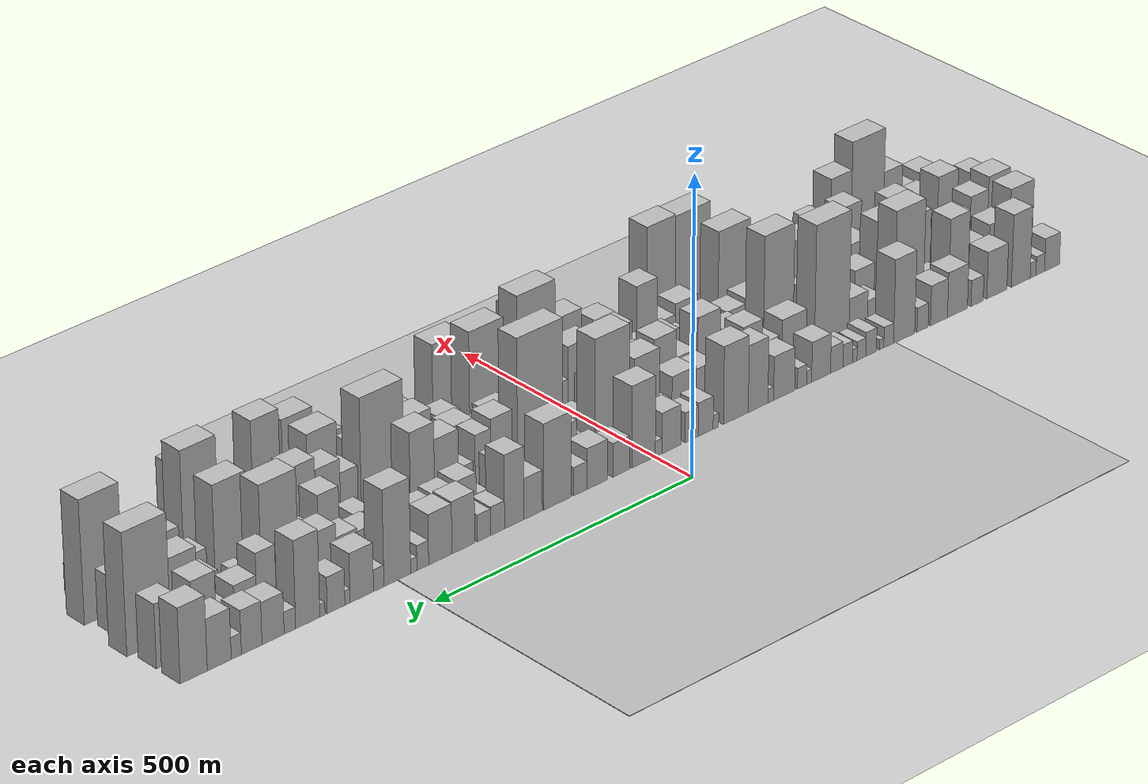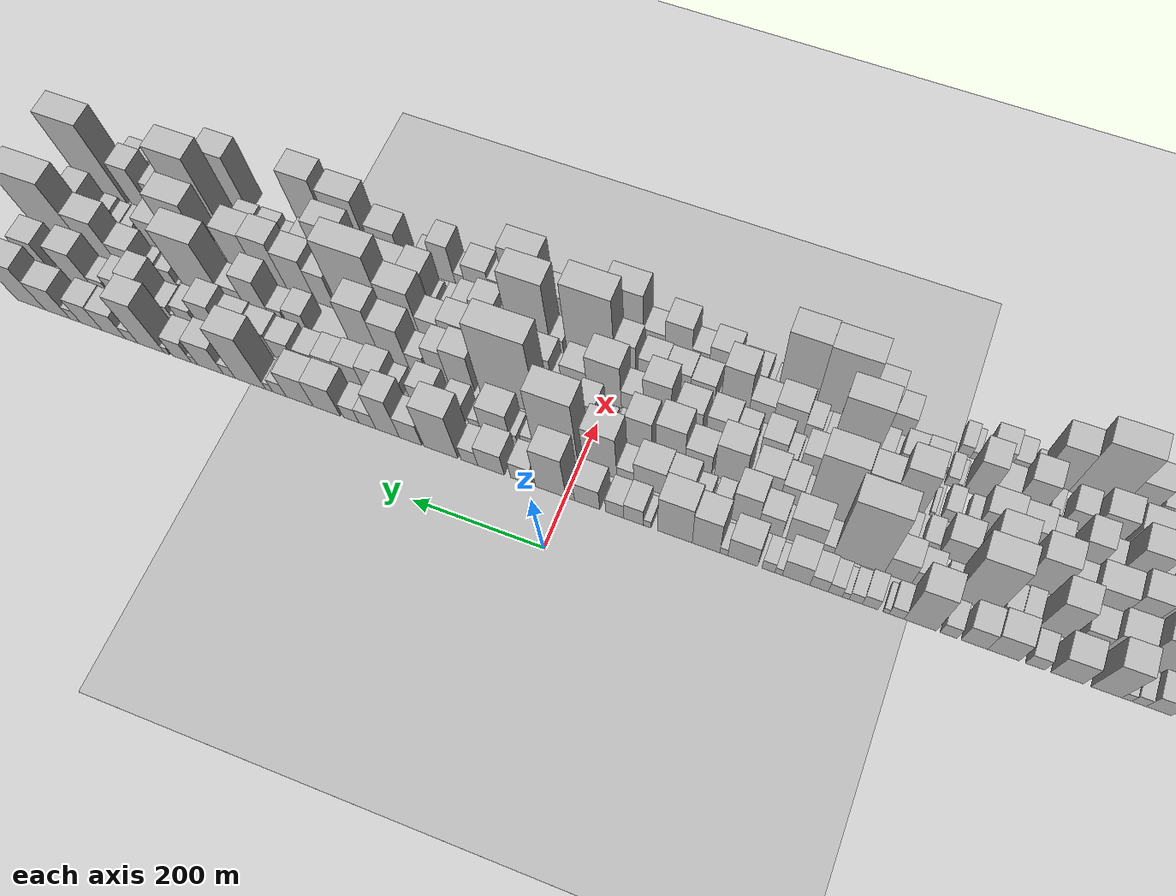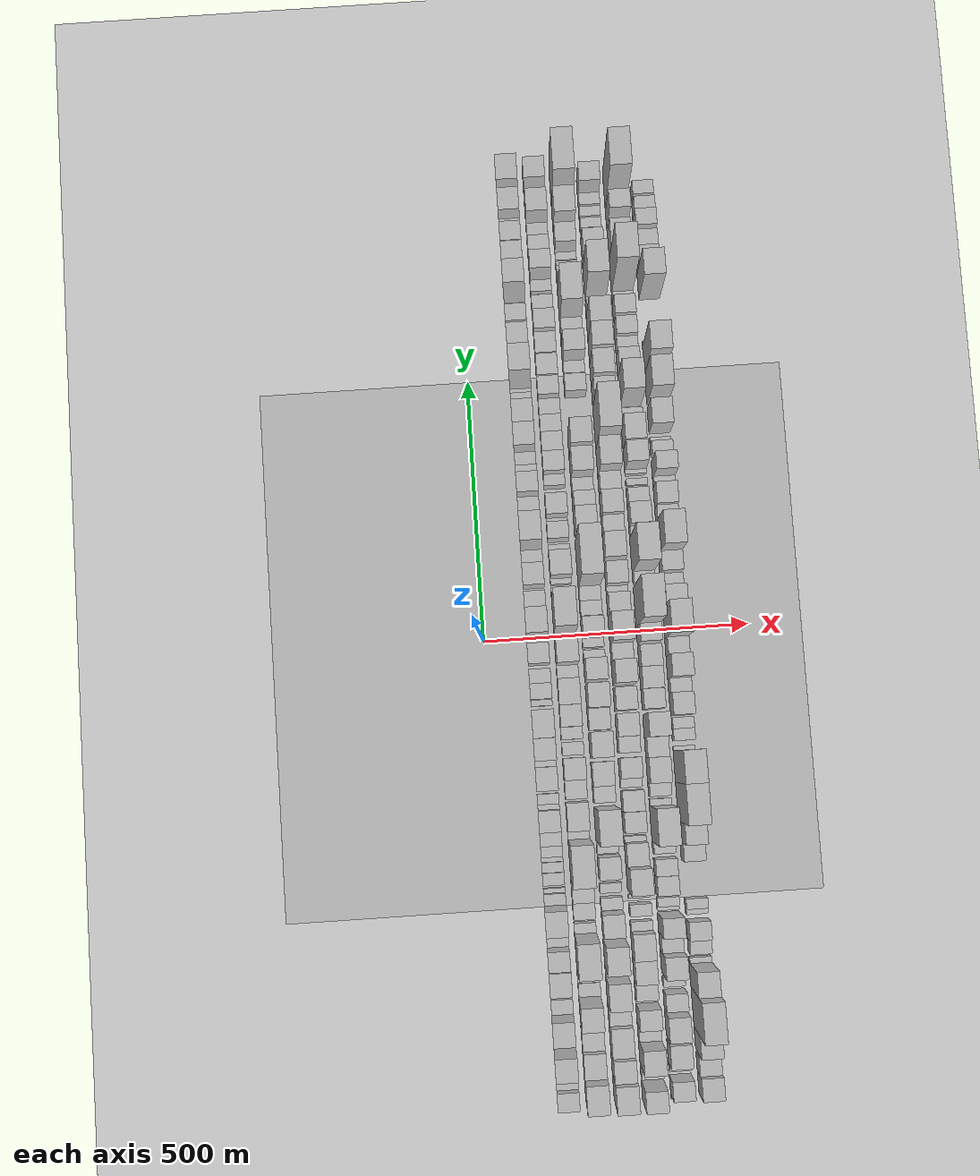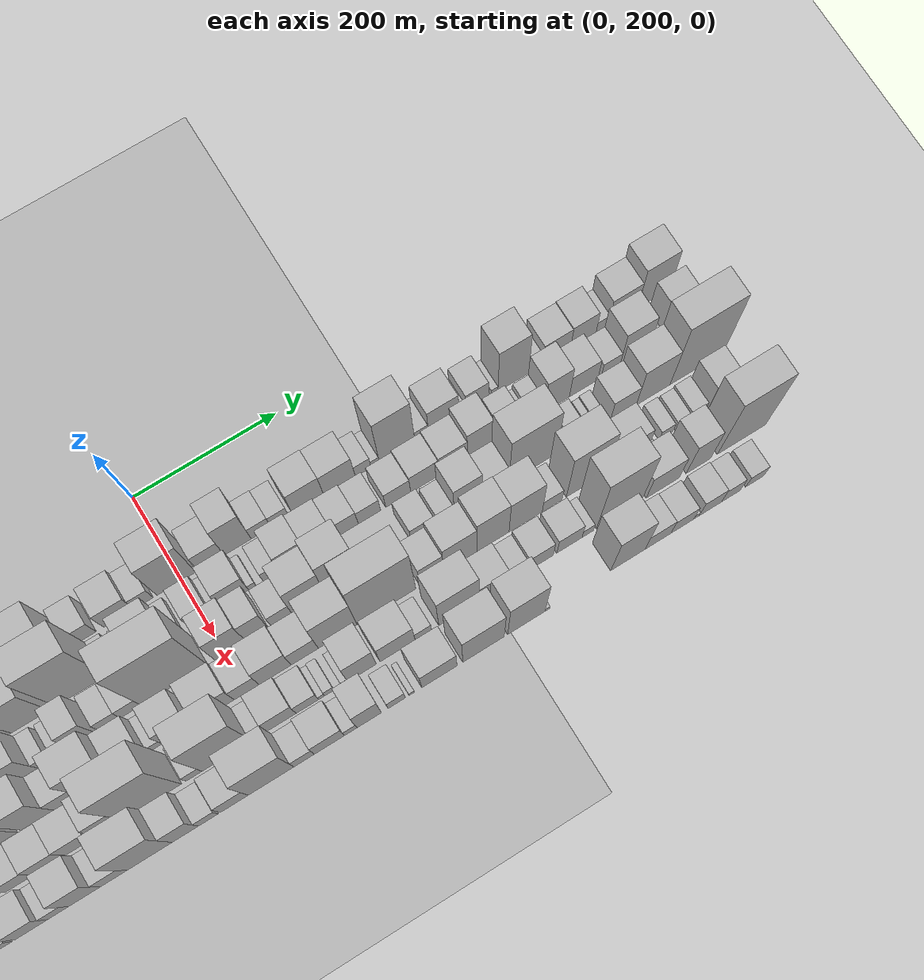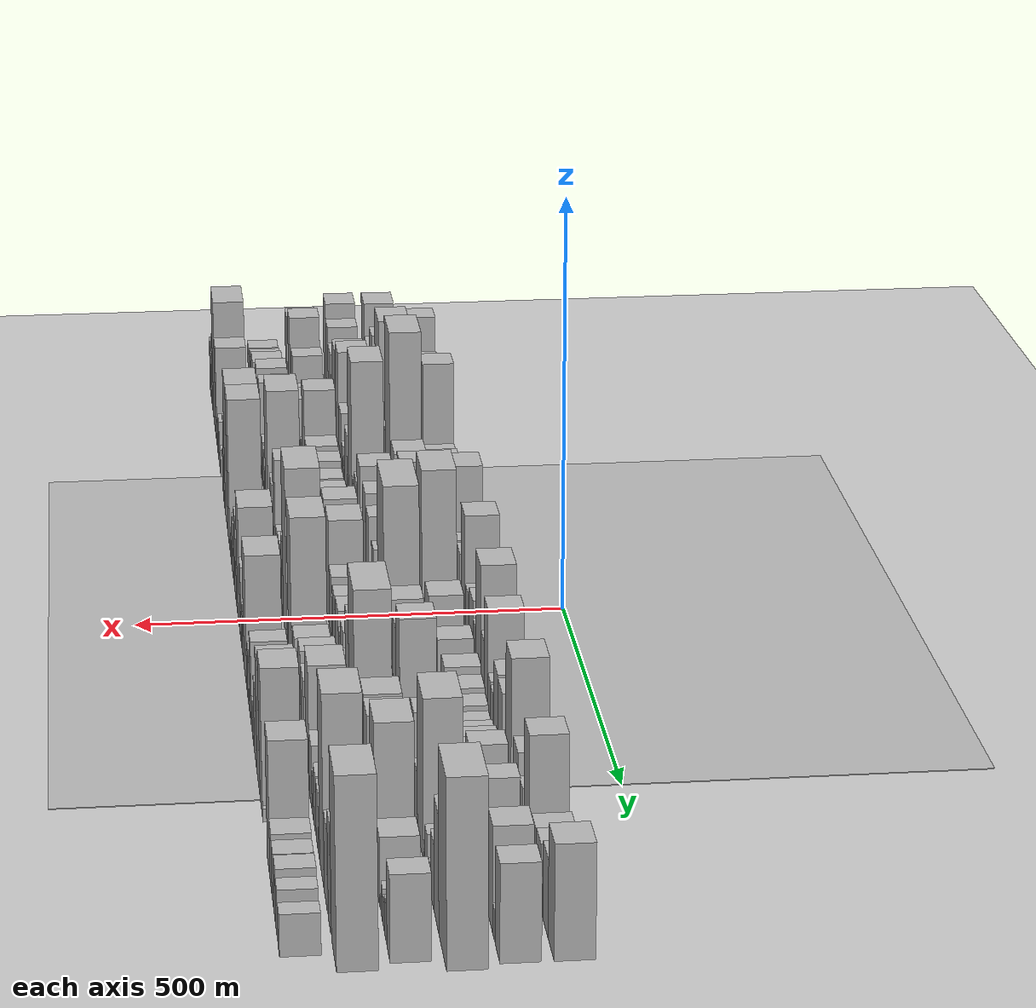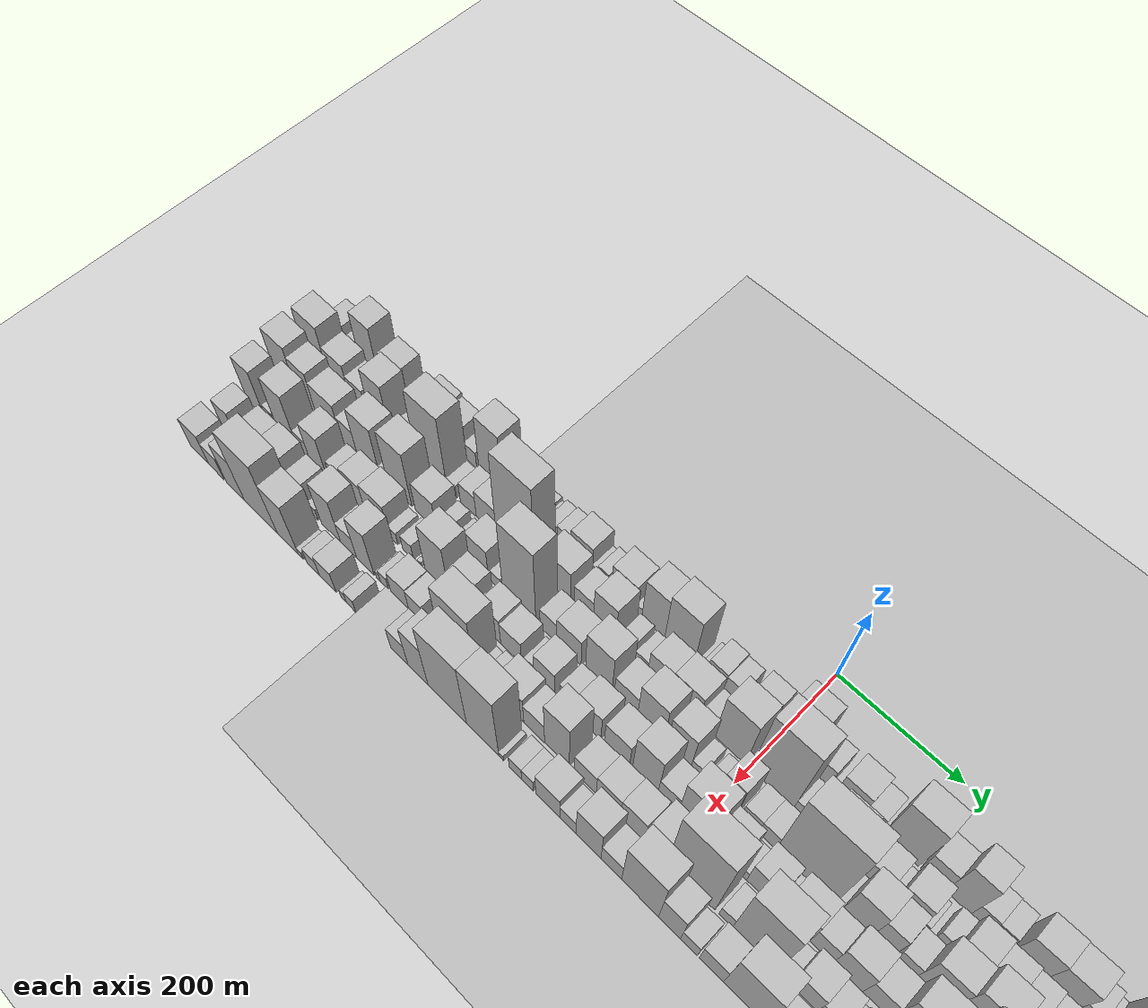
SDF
<?xml version="1.0" encoding="utf-8"?>

<sdf version="1.6">

   <world name="default">

      <gui fullscreen="0">

         <camera name="user_camera">

            <pose>-15 0 4.57585 0 0 0</pose>

            <view_controller>orbit</view_controller>

         </camera>

      </gui>

      <scene>

         <sky>

           <clouds>

             <speed>12</speed>

           </clouds>

         </sky>

         <ambient>0.4 0.4 0.4 1</ambient>

         <background>0.7 0.7 0.7 1</background>

         <shadows>1</shadows>

      </scene>

      <gravity>0 0 -9.8066</gravity>

      <magnetic_field>6e-06 2.3e-05 -4.2e-05</magnetic_field>

      <physics default="0" name="default_physics" type="ode">

         <ode>

            <solver>

               <type>quick</type>

               <iters>10</iters>

               <sor>1.0</sor>

               <use_dynamic_moi_rescaling>0</use_dynamic_moi_rescaling>

            </solver>

            <constraints>

               <cfm>0</cfm>

               <erp>0.2</erp>

               <contact_max_correcting_vel>100</contact_max_correcting_vel>

               <contact_surface_layer>0.001</contact_surface_layer>

            </constraints>

         </ode>

         <max_step_size>0.004</max_step_size>

         <real_time_factor>1</real_time_factor>

         <real_time_update_rate>250</real_time_update_rate>

      </physics>

      <light name="sun" type="directional">

         <cast_shadows>1</cast_shadows>

         <pose>0 0 10 0 0 0</pose>

         <diffuse>0.8 0.8 0.8 1</diffuse>

         <specular>0.2 0.2 0.2 1</specular>

         <attenuation>

            <range>1000</range>

            <constant>0.9</constant>

            <linear>0.01</linear>

            <quadratic>0.001</quadratic>

         </attenuation>

         <direction>-0.5 0.1 -0.9</direction>

      </light>

      <include>

         <name>ground_plane_1</name>

         <uri>model://HANNAS_ground_plane</uri>

         <pose>0 0 0  0 0 0</pose>

      </include>

      <include>

         <name>ground_plane_2</name>

         <uri>model://HANNAS_ground_plane</uri>

         <pose>100 0 0  0 0 0</pose>

      </include>

      <model name="building_1">

         <static>1</static>

         <pose frame="">100.0000 -843.2579 0 0.000000 0.000000 0.000000</pose>

         <link name="link">

            <pose frame="">0 0 28.50 0 0 0</pose>

            <collision name="collision">

               <geometry>

                  <box>

                     <size>40.0000 33.4842 57.0000</size>

                  </box>

               </geometry>

               <max_contacts>10</max_contacts>

               <surface>

                  <contact>

                     <ode/>

                  </contact>

                  <bounce/>

                  <friction>

                     <torsional>

                        <ode/>

                     </torsional>

                     <ode/>

                  </friction>

               </surface>

            </collision>

            <visual name="visual">

               <cast_shadows>0</cast_shadows>

               <geometry>

                  <box>

                     <size>40.0000 33.4842 57.0000</size>

                  </box>

               </geometry>

               <material>

                  <script>

                     <uri>model://HANNAS_wall/materials/scripts</uri>

                     <uri>model://HANNAS_wall/materials/textures</uri>

                     <name>vrc/HANNAS_wall</name>

                  </script>

               </material>

            </visual>

            <self_collide>0</self_collide>

            <enable_wind>0</enable_wind>

            <kinematic>0</kinematic>

         </link>

      </model>

      <model name="building_2">

         <static>1</static>

         <pose frame="">100.0000 -816.9576 0 0.000000 0.000000 0.000000</pose>

         <link name="link">

            <pose frame="">0 0 16.50 0 0 0</pose>

            <collision name="collision">

               <geometry>

                  <box>

                     <size>40.0000 19.1166 33.0000</size>

                  </box>

               </geometry>

               <max_contacts>10</max_contacts>

               <surface>

                  <contact>

                     <ode/>

                  </contact>

                  <bounce/>

                  <friction>

                     <torsional>

                        <ode/>

                     </torsional>

                     <ode/>

                  </friction>

               </surface>

            </collision>

            <visual name="visual">

               <cast_shadows>0</cast_shadows>

               <geometry>

                  <box>

                     <size>40.0000 19.1166 33.0000</size>

                  </box>

               </geometry>

               <material>

                  <script>

                     <uri>model://HANNAS_wall/materials/scripts</uri>

                     <uri>model://HANNAS_wall/materials/textures</uri>

                     <name>vrc/HANNAS_wall</name>

                  </script>

               </material>

            </visual>

            <self_collide>0</self_collide>

            <enable_wind>0</enable_wind>

            <kinematic>0</kinematic>

         </link>

      </model>

      <model name="building_3">

         <static>1</static>

         <pose frame="">100.0000 -800.8615 0 0.000000 0.000000 0.000000</pose>

         <link name="link">

            <pose frame="">0 0 13.50 0 0 0</pose>

            <collision name="collision">

               <geometry>

                  <box>

                     <size>40.0000 13.0756 27.0000</size>

                  </box>

               </geometry>

               <max_contacts>10</max_contacts>

               <surface>

                  <contact>

                     <ode/>

                  </contact>

                  <bounce/>

                  <friction>

                     <torsional>

                        <ode/>

                     </torsional>

                     <ode/>

                  </friction>

               </surface>

            </collision>

            <visual name="visual">

               <cast_shadows>0</cast_shadows>

               <geometry>

                  <box>

                     <size>40.0000 13.0756 27.0000</size>

                  </box>

               </geometry>

               <material>

                  <script>

                     <uri>model://HANNAS_wall/materials/scripts</uri>

                     <uri>model://HANNAS_wall/materials/textures</uri>

                     <name>vrc/HANNAS_wall</name>

                  </script>

               </material>

            </visual>

            <self_collide>0</self_collide>

            <enable_wind>0</enable_wind>

            <kinematic>0</kinematic>

         </link>

      </model>

      <model name="building_4">

         <static>1</static>

         <pose frame="">100.0000 -773.4738 0 0.000000 0.000000 0.000000</pose>

         <link name="link">

            <pose frame="">0 0 63.00 0 0 0</pose>

            <collision name="collision">

               <geometry>

                  <box>

                     <size>40.0000 41.6998 126.0000</size>

                  </box>

               </geometry>

               <max_contacts>10</max_contacts>

               <surface>

                  <contact>

                     <ode/>

                  </contact>

                  <bounce/>

                  <friction>

                     <torsional>

                        <ode/>

                     </torsional>

                     <ode/>

                  </friction>

               </surface>

            </collision>

            <visual name="visual">

               <cast_shadows>0</cast_shadows>

               <geometry>

                  <box>

                     <size>40.0000 41.6998 126.0000</size>

                  </box>

               </geometry>

               <material>

                  <script>

                     <uri>model://HANNAS_wall/materials/scripts</uri>

                     <uri>model://HANNAS_wall/materials/textures</uri>

                     <name>vrc/HANNAS_wall</name>

                  </script>

               </material>

            </visual>

            <self_collide>0</self_collide>

            <enable_wind>0</enable_wind>

            <kinematic>0</kinematic>

         </link>

      </model>

      <model name="building_5">

         <static>1</static>

         <pose frame="">100.0000 -720.4473 0 0.000000 0.000000 0.000000</pose>

         <link name="link">

            <pose frame="">0 0 40.50 0 0 0</pose>

            <collision name="collision">

               <geometry>

                  <box>

                     <size>40.0000 44.3533 81.0000</size>

                  </box>

               </geometry>

               <max_contacts>10</max_contacts>

               <surface>

                  <contact>

                     <ode/>

                  </contact>

                  <bounce/>

                  <friction>

                     <torsional>

                        <ode/>

                     </torsional>

                     <ode/>

                  </friction>

               </surface>

            </collision>

            <visual name="visual">

               <cast_shadows>0</cast_shadows>

               <geometry>

                  <box>

                     <size>40.0000 44.3533 81.0000</size>

                  </box>

               </geometry>

               <material>

                  <script>

                     <uri>model://HANNAS_wall/materials/scripts</uri>

                     <uri>model://HANNAS_wall/materials/textures</uri>

                     <name>vrc/HANNAS_wall</name>

                  </script>

               </material>

            </visual>

            <self_collide>0</self_collide>

            <enable_wind>0</enable_wind>

            <kinematic>0</kinematic>

         </link>

      </model>

      <model name="building_6">

         <static>1</static>

         <pose frame="">100.0000 -676.9597 0 0.000000 0.000000 0.000000</pose>

         <link name="link">

            <pose frame="">0 0 22.50 0 0 0</pose>

            <collision name="collision">

               <geometry>

                  <box>

                     <size>40.0000 26.6221 45.0000</size>

                  </box>

               </geometry>

               <max_contacts>10</max_contacts>

               <surface>

                  <contact>

                     <ode/>

                  </contact>

                  <bounce/>

                  <friction>

                     <torsional>

                        <ode/>

                     </torsional>

                     <ode/>

                  </friction>

               </surface>

            </collision>

            <visual name="visual">

               <cast_shadows>0</cast_shadows>

               <geometry>

                  <box>

                     <size>40.0000 26.6221 45.0000</size>

                  </box>

               </geometry>

               <material>

                  <script>

                     <uri>model://HANNAS_wall/materials/scripts</uri>

                     <uri>model://HANNAS_wall/materials/textures</uri>

                     <name>vrc/HANNAS_wall</name>

                  </script>

               </material>

            </visual>

            <self_collide>0</self_collide>

            <enable_wind>0</enable_wind>

            <kinematic>0</kinematic>

         </link>

      </model>

      <model name="building_7">

         <static>1</static>

         <pose frame="">100.0000 -633.8017 0 0.000000 0.000000 0.000000</pose>

         <link name="link">

            <pose frame="">0 0 39.00 0 0 0</pose>

            <collision name="collision">

               <geometry>

                  <box>

                     <size>40.0000 43.6939 78.0000</size>

                  </box>

               </geometry>

               <max_contacts>10</max_contacts>

               <surface>

                  <contact>

                     <ode/>

                  </contact>

                  <bounce/>

                  <friction>

                     <torsional>

                        <ode/>

                     </torsional>

                     <ode/>

                  </friction>

               </surface>

            </collision>

            <visual name="visual">

               <cast_shadows>0</cast_shadows>

               <geometry>

                  <box>

                     <size>40.0000 43.6939 78.0000</size>

                  </box>

               </geometry>

               <material>

                  <script>

                     <uri>model://HANNAS_wall/materials/scripts</uri>

                     <uri>model://HANNAS_wall/materials/textures</uri>

                     <name>vrc/HANNAS_wall</name>

                  </script>

               </material>

            </visual>

            <self_collide>0</self_collide>

            <enable_wind>0</enable_wind>

            <kinematic>0</kinematic>

         </link>

      </model>

      <model name="building_8">

         <static>1</static>

         <pose frame="">100.0000 -593.5074 0 0.000000 0.000000 0.000000</pose>

         <link name="link">

            <pose frame="">0 0 34.50 0 0 0</pose>

            <collision name="collision">

               <geometry>

                  <box>

                     <size>40.0000 36.8945 69.0000</size>

                  </box>

               </geometry>

               <max_contacts>10</max_contacts>

               <surface>

                  <contact>

                     <ode/>

                  </contact>

                  <bounce/>

                  <friction>

                     <torsional>

                        <ode/>

                     </torsional>

                     <ode/>

                  </friction>

               </surface>

            </collision>

            <visual name="visual">

               <cast_shadows>0</cast_shadows>

               <geometry>

                  <box>

                     <size>40.0000 36.8945 69.0000</size>

                  </box>

               </geometry>

               <material>

                  <script>

                     <uri>model://HANNAS_wall/materials/scripts</uri>

                     <uri>model://HANNAS_wall/materials/textures</uri>

                     <name>vrc/HANNAS_wall</name>

                  </script>

               </material>

            </visual>

            <self_collide>0</self_collide>

            <enable_wind>0</enable_wind>

            <kinematic>0</kinematic>

         </link>

      </model>

      <model name="building_9">

         <static>1</static>

         <pose frame="">100.0000 -558.0110 0 0.000000 0.000000 0.000000</pose>

         <link name="link">

            <pose frame="">0 0 21.00 0 0 0</pose>

            <collision name="collision">

               <geometry>

                  <box>

                     <size>40.0000 24.0984 42.0000</size>

                  </box>

               </geometry>

               <max_contacts>10</max_contacts>

               <surface>

                  <contact>

                     <ode/>

                  </contact>

                  <bounce/>

                  <friction>

                     <torsional>

                        <ode/>

                     </torsional>

                     <ode/>

                  </friction>

               </surface>

            </collision>

            <visual name="visual">

               <cast_shadows>0</cast_shadows>

               <geometry>

                  <box>

                     <size>40.0000 24.0984 42.0000</size>

                  </box>

               </geometry>

               <material>

                  <script>

                     <uri>model://HANNAS_wall/materials/scripts</uri>

                     <uri>model://HANNAS_wall/materials/textures</uri>

                     <name>vrc/HANNAS_wall</name>

                  </script>

               </material>

            </visual>

            <self_collide>0</self_collide>

            <enable_wind>0</enable_wind>

            <kinematic>0</kinematic>

         </link>

      </model>

      <model name="building_10">

         <static>1</static>

         <pose frame="">100.0000 -518.2136 0 0.000000 0.000000 0.000000</pose>

         <link name="link">

            <pose frame="">0 0 72.00 0 0 0</pose>

            <collision name="collision">

               <geometry>

                  <box>

                     <size>40.0000 45.4963 144.0000</size>

                  </box>

               </geometry>

               <max_contacts>10</max_contacts>

               <surface>

                  <contact>

                     <ode/>

                  </contact>

                  <bounce/>

                  <friction>

                     <torsional>

                        <ode/>

                     </torsional>

                     <ode/>

                  </friction>

               </surface>

            </collision>

            <visual name="visual">

               <cast_shadows>0</cast_shadows>

               <geometry>

                  <box>

                     <size>40.0000 45.4963 144.0000</size>

                  </box>

               </geometry>

               <material>

                  <script>

                     <uri>model://HANNAS_wall/materials/scripts</uri>

                     <uri>model://HANNAS_wall/materials/textures</uri>

                     <name>vrc/HANNAS_wall</name>

                  </script>

               </material>

            </visual>

            <self_collide>0</self_collide>

            <enable_wind>0</enable_wind>

            <kinematic>0</kinematic>

         </link>

      </model>

      <model name="building_11">

         <static>1</static>

         <pose frame="">100.0000 -484.9639 0 0.000000 0.000000 0.000000</pose>

         <link name="link">

            <pose frame="">0 0 18.00 0 0 0</pose>

            <collision name="collision">

               <geometry>

                  <box>

                     <size>40.0000 21.0030 36.0000</size>

                  </box>

               </geometry>

               <max_contacts>10</max_contacts>

               <surface>

                  <contact>

                     <ode/>

                  </contact>

                  <bounce/>

                  <friction>

                     <torsional>

                        <ode/>

                     </torsional>

                     <ode/>

                  </friction>

               </surface>

            </collision>

            <visual name="visual">

               <cast_shadows>0</cast_shadows>

               <geometry>

                  <box>

                     <size>40.0000 21.0030 36.0000</size>

                  </box>

               </geometry>

               <material>

                  <script>

                     <uri>model://HANNAS_wall/materials/scripts</uri>

                     <uri>model://HANNAS_wall/materials/textures</uri>

                     <name>vrc/HANNAS_wall</name>

                  </script>

               </material>

            </visual>

            <self_collide>0</self_collide>

            <enable_wind>0</enable_wind>

            <kinematic>0</kinematic>

         </link>

      </model>

      <model name="building_12">

         <static>1</static>

         <pose frame="">100.0000 -470.1170 0 0.000000 0.000000 0.000000</pose>

         <link name="link">

            <pose frame="">0 0 9.00 0 0 0</pose>

            <collision name="collision">

               <geometry>

                  <box>

                     <size>40.0000 8.6909 18.0000</size>

                  </box>

               </geometry>

               <max_contacts>10</max_contacts>

               <surface>

                  <contact>

                     <ode/>

                  </contact>

                  <bounce/>

                  <friction>

                     <torsional>

                        <ode/>

                     </torsional>

                     <ode/>

                  </friction>

               </surface>

            </collision>

            <visual name="visual">

               <cast_shadows>0</cast_shadows>

               <geometry>

                  <box>

                     <size>40.0000 8.6909 18.0000</size>

                  </box>

               </geometry>

               <material>

                  <script>

                     <uri>model://HANNAS_wall/materials/scripts</uri>

                     <uri>model://HANNAS_wall/materials/textures</uri>

                     <name>vrc/HANNAS_wall</name>

                  </script>

               </material>

            </visual>

            <self_collide>0</self_collide>

            <enable_wind>0</enable_wind>

            <kinematic>0</kinematic>

         </link>

      </model>

      <model name="building_13">

         <static>1</static>

         <pose frame="">100.0000 -447.4623 0 0.000000 0.000000 0.000000</pose>

         <link name="link">

            <pose frame="">0 0 21.00 0 0 0</pose>

            <collision name="collision">

               <geometry>

                  <box>

                     <size>40.0000 22.6184 42.0000</size>

                  </box>

               </geometry>

               <max_contacts>10</max_contacts>

               <surface>

                  <contact>

                     <ode/>

                  </contact>

                  <bounce/>

                  <friction>

                     <torsional>

                        <ode/>

                     </torsional>

                     <ode/>

                  </friction>

               </surface>

            </collision>

            <visual name="visual">

               <cast_shadows>0</cast_shadows>

               <geometry>

                  <box>

                     <size>40.0000 22.6184 42.0000</size>

                  </box>

               </geometry>

               <material>

                  <script>

                     <uri>model://HANNAS_wall/materials/scripts</uri>

                     <uri>model://HANNAS_wall/materials/textures</uri>

                     <name>vrc/HANNAS_wall</name>

                  </script>

               </material>

            </visual>

            <self_collide>0</self_collide>

            <enable_wind>0</enable_wind>

            <kinematic>0</kinematic>

         </link>

      </model>

      <model name="building_14">

         <static>1</static>

         <pose frame="">100.0000 -426.7860 0 0.000000 0.000000 0.000000</pose>

         <link name="link">

            <pose frame="">0 0 16.50 0 0 0</pose>

            <collision name="collision">

               <geometry>

                  <box>

                     <size>40.0000 18.7343 33.0000</size>

                  </box>

               </geometry>

               <max_contacts>10</max_contacts>

               <surface>

                  <contact>

                     <ode/>

                  </contact>

                  <bounce/>

                  <friction>

                     <torsional>

                        <ode/>

                     </torsional>

                     <ode/>

                  </friction>

               </surface>

            </collision>

            <visual name="visual">

               <cast_shadows>0</cast_shadows>

               <geometry>

                  <box>

                     <size>40.0000 18.7343 33.0000</size>

                  </box>

               </geometry>

               <material>

                  <script>

                     <uri>model://HANNAS_wall/materials/scripts</uri>

                     <uri>model://HANNAS_wall/materials/textures</uri>

                     <name>vrc/HANNAS_wall</name>

                  </script>

               </material>

            </visual>

            <self_collide>0</self_collide>

            <enable_wind>0</enable_wind>

            <kinematic>0</kinematic>

         </link>

      </model>

      <model name="building_15">

         <static>1</static>

         <pose frame="">100.0000 -412.5389 0 0.000000 0.000000 0.000000</pose>

         <link name="link">

            <pose frame="">0 0 12.00 0 0 0</pose>

            <collision name="collision">

               <geometry>

                  <box>

                     <size>40.0000 9.7600 24.0000</size>

                  </box>

               </geometry>

               <max_contacts>10</max_contacts>

               <surface>

                  <contact>

                     <ode/>

                  </contact>

                  <bounce/>

                  <friction>

                     <torsional>

                        <ode/>

                     </torsional>

                     <ode/>

                  </friction>

               </surface>

            </collision>

            <visual name="visual">

               <cast_shadows>0</cast_shadows>

               <geometry>

                  <box>

                     <size>40.0000 9.7600 24.0000</size>

                  </box>

               </geometry>

               <material>

                  <script>

                     <uri>model://HANNAS_wall/materials/scripts</uri>

                     <uri>model://HANNAS_wall/materials/textures</uri>

                     <name>vrc/HANNAS_wall</name>

                  </script>

               </material>

            </visual>

            <self_collide>0</self_collide>

            <enable_wind>0</enable_wind>

            <kinematic>0</kinematic>

         </link>

      </model>

      <model name="building_16">

         <static>1</static>

         <pose frame="">100.0000 -397.6763 0 0.000000 0.000000 0.000000</pose>

         <link name="link">

            <pose frame="">0 0 19.50 0 0 0</pose>

            <collision name="collision">

               <geometry>

                  <box>

                     <size>40.0000 19.9652 39.0000</size>

                  </box>

               </geometry>

               <max_contacts>10</max_contacts>

               <surface>

                  <contact>

                     <ode/>

                  </contact>

                  <bounce/>

                  <friction>

                     <torsional>

                        <ode/>

                     </torsional>

                     <ode/>

                  </friction>

               </surface>

            </collision>

            <visual name="visual">

               <cast_shadows>0</cast_shadows>

               <geometry>

                  <box>

                     <size>40.0000 19.9652 39.0000</size>

                  </box>

               </geometry>

               <material>

                  <script>

                     <uri>model://HANNAS_wall/materials/scripts</uri>

                     <uri>model://HANNAS_wall/materials/textures</uri>

                     <name>vrc/HANNAS_wall</name>

                  </script>

               </material>

            </visual>

            <self_collide>0</self_collide>

            <enable_wind>0</enable_wind>

            <kinematic>0</kinematic>

         </link>

      </model>

      <model name="building_17">

         <static>1</static>

         <pose frame="">100.0000 -374.5633 0 0.000000 0.000000 0.000000</pose>

         <link name="link">

            <pose frame="">0 0 22.50 0 0 0</pose>

            <collision name="collision">

               <geometry>

                  <box>

                     <size>40.0000 26.2607 45.0000</size>

                  </box>

               </geometry>

               <max_contacts>10</max_contacts>

               <surface>

                  <contact>

                     <ode/>

                  </contact>

                  <bounce/>

                  <friction>

                     <torsional>

                        <ode/>

                     </torsional>

                     <ode/>

                  </friction>

               </surface>

            </collision>

            <visual name="visual">

               <cast_shadows>0</cast_shadows>

               <geometry>

                  <box>

                     <size>40.0000 26.2607 45.0000</size>

                  </box>

               </geometry>

               <material>

                  <script>

                     <uri>model://HANNAS_wall/materials/scripts</uri>

                     <uri>model://HANNAS_wall/materials/textures</uri>

                     <name>vrc/HANNAS_wall</name>

                  </script>

               </material>

            </visual>

            <self_collide>0</self_collide>

            <enable_wind>0</enable_wind>

            <kinematic>0</kinematic>

         </link>

      </model>

      <model name="building_18">

         <static>1</static>

         <pose frame="">100.0000 -341.5382 0 0.000000 0.000000 0.000000</pose>

         <link name="link">

            <pose frame="">0 0 34.50 0 0 0</pose>

            <collision name="collision">

               <geometry>

                  <box>

                     <size>40.0000 39.7896 69.0000</size>

                  </box>

               </geometry>

               <max_contacts>10</max_contacts>

               <surface>

                  <contact>

                     <ode/>

                  </contact>

                  <bounce/>

                  <friction>

                     <torsional>

                        <ode/>

                     </torsional>

                     <ode/>

                  </friction>

               </surface>

            </collision>

            <visual name="visual">

               <cast_shadows>0</cast_shadows>

               <geometry>

                  <box>

                     <size>40.0000 39.7896 69.0000</size>

                  </box>

               </geometry>

               <material>

                  <script>

                     <uri>model://HANNAS_wall/materials/scripts</uri>

                     <uri>model://HANNAS_wall/materials/textures</uri>

                     <name>vrc/HANNAS_wall</name>

                  </script>

               </material>

            </visual>

            <self_collide>0</self_collide>

            <enable_wind>0</enable_wind>

            <kinematic>0</kinematic>

         </link>

      </model>

      <model name="building_19">

         <static>1</static>

         <pose frame="">100.0000 -316.3711 0 0.000000 0.000000 0.000000</pose>

         <link name="link">

            <pose frame="">0 0 12.00 0 0 0</pose>

            <collision name="collision">

               <geometry>

                  <box>

                     <size>40.0000 10.5445 24.0000</size>

                  </box>

               </geometry>

               <max_contacts>10</max_contacts>

               <surface>

                  <contact>

                     <ode/>

                  </contact>

                  <bounce/>

                  <friction>

                     <torsional>

                        <ode/>

                     </torsional>

                     <ode/>

                  </friction>

               </surface>

            </collision>

            <visual name="visual">

               <cast_shadows>0</cast_shadows>

               <geometry>

                  <box>

                     <size>40.0000 10.5445 24.0000</size>

                  </box>

               </geometry>

               <material>

                  <script>

                     <uri>model://HANNAS_wall/materials/scripts</uri>

                     <uri>model://HANNAS_wall/materials/textures</uri>

                     <name>vrc/HANNAS_wall</name>

                  </script>

               </material>

            </visual>

            <self_collide>0</self_collide>

            <enable_wind>0</enable_wind>

            <kinematic>0</kinematic>

         </link>

      </model>

      <model name="building_20">

         <static>1</static>

         <pose frame="">100.0000 -301.5799 0 0.000000 0.000000 0.000000</pose>

         <link name="link">

            <pose frame="">0 0 18.00 0 0 0</pose>

            <collision name="collision">

               <geometry>

                  <box>

                     <size>40.0000 19.0379 36.0000</size>

                  </box>

               </geometry>

               <max_contacts>10</max_contacts>

               <surface>

                  <contact>

                     <ode/>

                  </contact>

                  <bounce/>

                  <friction>

                     <torsional>

                        <ode/>

                     </torsional>

                     <ode/>

                  </friction>

               </surface>

            </collision>

            <visual name="visual">

               <cast_shadows>0</cast_shadows>

               <geometry>

                  <box>

                     <size>40.0000 19.0379 36.0000</size>

                  </box>

               </geometry>

               <material>

                  <script>

                     <uri>model://HANNAS_wall/materials/scripts</uri>

                     <uri>model://HANNAS_wall/materials/textures</uri>

                     <name>vrc/HANNAS_wall</name>

                  </script>

               </material>

            </visual>

            <self_collide>0</self_collide>

            <enable_wind>0</enable_wind>

            <kinematic>0</kinematic>

         </link>

      </model>

      <model name="building_21">

         <static>1</static>

         <pose frame="">100.0000 -264.2307 0 0.000000 0.000000 0.000000</pose>

         <link name="link">

            <pose frame="">0 0 37.50 0 0 0</pose>

            <collision name="collision">

               <geometry>

                  <box>

                     <size>40.0000 43.6604 75.0000</size>

                  </box>

               </geometry>

               <max_contacts>10</max_contacts>

               <surface>

                  <contact>

                     <ode/>

                  </contact>

                  <bounce/>

                  <friction>

                     <torsional>

                        <ode/>

                     </torsional>

                     <ode/>

                  </friction>

               </surface>

            </collision>

            <visual name="visual">

               <cast_shadows>0</cast_shadows>

               <geometry>

                  <box>

                     <size>40.0000 43.6604 75.0000</size>

                  </box>

               </geometry>

               <material>

                  <script>

                     <uri>model://HANNAS_wall/materials/scripts</uri>

                     <uri>model://HANNAS_wall/materials/textures</uri>

                     <name>vrc/HANNAS_wall</name>

                  </script>

               </material>

            </visual>

            <self_collide>0</self_collide>

            <enable_wind>0</enable_wind>

            <kinematic>0</kinematic>

         </link>

      </model>

      <model name="building_22">

         <static>1</static>

         <pose frame="">100.0000 -236.5684 0 0.000000 0.000000 0.000000</pose>

         <link name="link">

            <pose frame="">0 0 12.00 0 0 0</pose>

            <collision name="collision">

               <geometry>

                  <box>

                     <size>40.0000 11.6643 24.0000</size>

                  </box>

               </geometry>

               <max_contacts>10</max_contacts>

               <surface>

                  <contact>

                     <ode/>

                  </contact>

                  <bounce/>

                  <friction>

                     <torsional>

                        <ode/>

                     </torsional>

                     <ode/>

                  </friction>

               </surface>

            </collision>

            <visual name="visual">

               <cast_shadows>0</cast_shadows>

               <geometry>

                  <box>

                     <size>40.0000 11.6643 24.0000</size>

                  </box>

               </geometry>

               <material>

                  <script>

                     <uri>model://HANNAS_wall/materials/scripts</uri>

                     <uri>model://HANNAS_wall/materials/textures</uri>

                     <name>vrc/HANNAS_wall</name>

                  </script>

               </material>

            </visual>

            <self_collide>0</self_collide>

            <enable_wind>0</enable_wind>

            <kinematic>0</kinematic>

         </link>

      </model>

      <model name="building_23">

         <static>1</static>

         <pose frame="">100.0000 -210.4001 0 0.000000 0.000000 0.000000</pose>

         <link name="link">

            <pose frame="">0 0 57.00 0 0 0</pose>

            <collision name="collision">

               <geometry>

                  <box>

                     <size>40.0000 40.6722 114.0000</size>

                  </box>

               </geometry>

               <max_contacts>10</max_contacts>

               <surface>

                  <contact>

                     <ode/>

                  </contact>

                  <bounce/>

                  <friction>

                     <torsional>

                        <ode/>

                     </torsional>

                     <ode/>

                  </friction>

               </surface>

            </collision>

            <visual name="visual">

               <cast_shadows>0</cast_shadows>

               <geometry>

                  <box>

                     <size>40.0000 40.6722 114.0000</size>

                  </box>

               </geometry>

               <material>

                  <script>

                     <uri>model://HANNAS_wall/materials/scripts</uri>

                     <uri>model://HANNAS_wall/materials/textures</uri>

                     <name>vrc/HANNAS_wall</name>

                  </script>

               </material>

            </visual>

            <self_collide>0</self_collide>

            <enable_wind>0</enable_wind>

            <kinematic>0</kinematic>

         </link>

      </model>

      <model name="building_24">

         <static>1</static>

         <pose frame="">100.0000 -164.5461 0 0.000000 0.000000 0.000000</pose>

         <link name="link">

            <pose frame="">0 0 66.00 0 0 0</pose>

            <collision name="collision">

               <geometry>

                  <box>

                     <size>40.0000 51.0359 132.0000</size>

                  </box>

               </geometry>

               <max_contacts>10</max_contacts>

               <surface>

                  <contact>

                     <ode/>

                  </contact>

                  <bounce/>

                  <friction>

                     <torsional>

                        <ode/>

                     </torsional>

                     <ode/>

                  </friction>

               </surface>

            </collision>

            <visual name="visual">

               <cast_shadows>0</cast_shadows>

               <geometry>

                  <box>

                     <size>40.0000 51.0359 132.0000</size>

                  </box>

               </geometry>

               <material>

                  <script>

                     <uri>model://HANNAS_wall/materials/scripts</uri>

                     <uri>model://HANNAS_wall/materials/textures</uri>

                     <name>vrc/HANNAS_wall</name>

                  </script>

               </material>

            </visual>

            <self_collide>0</self_collide>

            <enable_wind>0</enable_wind>

            <kinematic>0</kinematic>

         </link>

      </model>

      <model name="building_25">

         <static>1</static>

         <pose frame="">100.0000 -123.3570 0 0.000000 0.000000 0.000000</pose>

         <link name="link">

            <pose frame="">0 0 12.00 0 0 0</pose>

            <collision name="collision">

               <geometry>

                  <box>

                     <size>40.0000 11.3422 24.0000</size>

                  </box>

               </geometry>

               <max_contacts>10</max_contacts>

               <surface>

                  <contact>

                     <ode/>

                  </contact>

                  <bounce/>

                  <friction>

                     <torsional>

                        <ode/>

                     </torsional>

                     <ode/>

                  </friction>

               </surface>

            </collision>

            <visual name="visual">

               <cast_shadows>0</cast_shadows>

               <geometry>

                  <box>

                     <size>40.0000 11.3422 24.0000</size>

                  </box>

               </geometry>

               <material>

                  <script>

                     <uri>model://HANNAS_wall/materials/scripts</uri>

                     <uri>model://HANNAS_wall/materials/textures</uri>

                     <name>vrc/HANNAS_wall</name>

                  </script>

               </material>

            </visual>

            <self_collide>0</self_collide>

            <enable_wind>0</enable_wind>

            <kinematic>0</kinematic>

         </link>

      </model>

      <model name="building_26">

         <static>1</static>

         <pose frame="">100.0000 -102.9204 0 0.000000 0.000000 0.000000</pose>

         <link name="link">

            <pose frame="">0 0 28.50 0 0 0</pose>

            <collision name="collision">

               <geometry>

                  <box>

                     <size>40.0000 29.5310 57.0000</size>

                  </box>

               </geometry>

               <max_contacts>10</max_contacts>

               <surface>

                  <contact>

                     <ode/>

                  </contact>

                  <bounce/>

                  <friction>

                     <torsional>

                        <ode/>

                     </torsional>

                     <ode/>

                  </friction>

               </surface>

            </collision>

            <visual name="visual">

               <cast_shadows>0</cast_shadows>

               <geometry>

                  <box>

                     <size>40.0000 29.5310 57.0000</size>

                  </box>

               </geometry>

               <material>

                  <script>

                     <uri>model://HANNAS_wall/materials/scripts</uri>

                     <uri>model://HANNAS_wall/materials/textures</uri>

                     <name>vrc/HANNAS_wall</name>

                  </script>

               </material>

            </visual>

            <self_collide>0</self_collide>

            <enable_wind>0</enable_wind>

            <kinematic>0</kinematic>

         </link>

      </model>

      <model name="building_27">

         <static>1</static>

         <pose frame="">100.0000 -74.5961 0 0.000000 0.000000 0.000000</pose>

         <link name="link">

            <pose frame="">0 0 25.50 0 0 0</pose>

            <collision name="collision">

               <geometry>

                  <box>

                     <size>40.0000 27.1176 51.0000</size>

                  </box>

               </geometry>

               <max_contacts>10</max_contacts>

               <surface>

                  <contact>

                     <ode/>

                  </contact>

                  <bounce/>

                  <friction>

                     <torsional>

                        <ode/>

                     </torsional>

                     <ode/>

                  </friction>

               </surface>

            </collision>

            <visual name="visual">

               <cast_shadows>0</cast_shadows>

               <geometry>

                  <box>

                     <size>40.0000 27.1176 51.0000</size>

                  </box>

               </geometry>

               <material>

                  <script>

                     <uri>model://HANNAS_wall/materials/scripts</uri>

                     <uri>model://HANNAS_wall/materials/textures</uri>

                     <name>vrc/HANNAS_wall</name>

                  </script>

               </material>

            </visual>

            <self_collide>0</self_collide>

            <enable_wind>0</enable_wind>

            <kinematic>0</kinematic>

         </link>

      </model>

      <model name="building_28">

         <static>1</static>

         <pose frame="">100.0000 -32.9300 0 0.000000 0.000000 0.000000</pose>

         <link name="link">

            <pose frame="">0 0 34.50 0 0 0</pose>

            <collision name="collision">

               <geometry>

                  <box>

                     <size>40.0000 38.2145 69.0000</size>

                  </box>

               </geometry>

               <max_contacts>10</max_contacts>

               <surface>

                  <contact>

                     <ode/>

                  </contact>

                  <bounce/>

                  <friction>

                     <torsional>

                        <ode/>

                     </torsional>

                     <ode/>

                  </friction>

               </surface>

            </collision>

            <visual name="visual">

               <cast_shadows>0</cast_shadows>

               <geometry>

                  <box>

                     <size>40.0000 38.2145 69.0000</size>

                  </box>

               </geometry>

               <material>

                  <script>

                     <uri>model://HANNAS_wall/materials/scripts</uri>

                     <uri>model://HANNAS_wall/materials/textures</uri>

                     <name>vrc/HANNAS_wall</name>

                  </script>

               </material>

            </visual>

            <self_collide>0</self_collide>

            <enable_wind>0</enable_wind>

            <kinematic>0</kinematic>

         </link>

      </model>

      <model name="building_29">

         <static>1</static>

         <pose frame="">100.0000 -7.2792 0 0.000000 0.000000 0.000000</pose>

         <link name="link">

            <pose frame="">0 0 13.50 0 0 0</pose>

            <collision name="collision">

               <geometry>

                  <box>

                     <size>40.0000 13.0871 27.0000</size>

                  </box>

               </geometry>

               <max_contacts>10</max_contacts>

               <surface>

                  <contact>

                     <ode/>

                  </contact>

                  <bounce/>

                  <friction>

                     <torsional>

                        <ode/>

                     </torsional>

                     <ode/>

                  </friction>

               </surface>

            </collision>

            <visual name="visual">

               <cast_shadows>0</cast_shadows>

               <geometry>

                  <box>

                     <size>40.0000 13.0871 27.0000</size>

                  </box>

               </geometry>

               <material>

                  <script>

                     <uri>model://HANNAS_wall/materials/scripts</uri>

                     <uri>model://HANNAS_wall/materials/textures</uri>

                     <name>vrc/HANNAS_wall</name>

                  </script>

               </material>

            </visual>

            <self_collide>0</self_collide>

            <enable_wind>0</enable_wind>

            <kinematic>0</kinematic>

         </link>

      </model>

      <model name="building_30">

         <static>1</static>

         <pose frame="">100.0000 22.7070 0 0.000000 0.000000 0.000000</pose>

         <link name="link">

            <pose frame="">0 0 69.00 0 0 0</pose>

            <collision name="collision">

               <geometry>

                  <box>

                     <size>40.0000 46.8853 138.0000</size>

                  </box>

               </geometry>

               <max_contacts>10</max_contacts>

               <surface>

                  <contact>

                     <ode/>

                  </contact>

                  <bounce/>

                  <friction>

                     <torsional>

                        <ode/>

                     </torsional>

                     <ode/>

                  </friction>

               </surface>

            </collision>

            <visual name="visual">

               <cast_shadows>0</cast_shadows>

               <geometry>

                  <box>

                     <size>40.0000 46.8853 138.0000</size>

                  </box>

               </geometry>

               <material>

                  <script>

                     <uri>model://HANNAS_wall/materials/scripts</uri>

                     <uri>model://HANNAS_wall/materials/textures</uri>

                     <name>vrc/HANNAS_wall</name>

                  </script>

               </material>

            </visual>

            <self_collide>0</self_collide>

            <enable_wind>0</enable_wind>

            <kinematic>0</kinematic>

         </link>

      </model>

      <model name="building_31">

         <static>1</static>

         <pose frame="">100.0000 67.7144 0 0.000000 0.000000 0.000000</pose>

         <link name="link">

            <pose frame="">0 0 28.50 0 0 0</pose>

            <collision name="collision">

               <geometry>

                  <box>

                     <size>40.0000 33.1295 57.0000</size>

                  </box>

               </geometry>

               <max_contacts>10</max_contacts>

               <surface>

                  <contact>

                     <ode/>

                  </contact>

                  <bounce/>

                  <friction>

                     <torsional>

                        <ode/>

                     </torsional>

                     <ode/>

                  </friction>

               </surface>

            </collision>

            <visual name="visual">

               <cast_shadows>0</cast_shadows>

               <geometry>

                  <box>

                     <size>40.0000 33.1295 57.0000</size>

                  </box>

               </geometry>

               <material>

                  <script>

                     <uri>model://HANNAS_wall/materials/scripts</uri>

                     <uri>model://HANNAS_wall/materials/textures</uri>

                     <name>vrc/HANNAS_wall</name>

                  </script>

               </material>

            </visual>

            <self_collide>0</self_collide>

            <enable_wind>0</enable_wind>

            <kinematic>0</kinematic>

         </link>

      </model>

      <model name="building_32">

         <static>1</static>

         <pose frame="">100.0000 114.8831 0 0.000000 0.000000 0.000000</pose>

         <link name="link">

            <pose frame="">0 0 34.50 0 0 0</pose>

            <collision name="collision">

               <geometry>

                  <box>

                     <size>40.0000 41.2078 69.0000</size>

                  </box>

               </geometry>

               <max_contacts>10</max_contacts>

               <surface>

                  <contact>

                     <ode/>

                  </contact>

                  <bounce/>

                  <friction>

                     <torsional>

                        <ode/>

                     </torsional>

                     <ode/>

                  </friction>

               </surface>

            </collision>

            <visual name="visual">

               <cast_shadows>0</cast_shadows>

               <geometry>

                  <box>

                     <size>40.0000 41.2078 69.0000</size>

                  </box>

               </geometry>

               <material>

                  <script>

                     <uri>model://HANNAS_wall/materials/scripts</uri>

                     <uri>model://HANNAS_wall/materials/textures</uri>

                     <name>vrc/HANNAS_wall</name>

                  </script>

               </material>

            </visual>

            <self_collide>0</self_collide>

            <enable_wind>0</enable_wind>

            <kinematic>0</kinematic>

         </link>

      </model>

      <model name="building_33">

         <static>1</static>

         <pose frame="">100.0000 148.5015 0 0.000000 0.000000 0.000000</pose>

         <link name="link">

            <pose frame="">0 0 24.00 0 0 0</pose>

            <collision name="collision">

               <geometry>

                  <box>

                     <size>40.0000 26.0290 48.0000</size>

                  </box>

               </geometry>

               <max_contacts>10</max_contacts>

               <surface>

                  <contact>

                     <ode/>

                  </contact>

                  <bounce/>

                  <friction>

                     <torsional>

                        <ode/>

                     </torsional>

                     <ode/>

                  </friction>

               </surface>

            </collision>

            <visual name="visual">

               <cast_shadows>0</cast_shadows>

               <geometry>

                  <box>

                     <size>40.0000 26.0290 48.0000</size>

                  </box>

               </geometry>

               <material>

                  <script>

                     <uri>model://HANNAS_wall/materials/scripts</uri>

                     <uri>model://HANNAS_wall/materials/textures</uri>

                     <name>vrc/HANNAS_wall</name>

                  </script>

               </material>

            </visual>

            <self_collide>0</self_collide>

            <enable_wind>0</enable_wind>

            <kinematic>0</kinematic>

         </link>

      </model>

      <model name="building_34">

         <static>1</static>

         <pose frame="">100.0000 193.2299 0 0.000000 0.000000 0.000000</pose>

         <link name="link">

            <pose frame="">0 0 72.00 0 0 0</pose>

            <collision name="collision">

               <geometry>

                  <box>

                     <size>40.0000 53.4279 144.0000</size>

                  </box>

               </geometry>

               <max_contacts>10</max_contacts>

               <surface>

                  <contact>

                     <ode/>

                  </contact>

                  <bounce/>

                  <friction>

                     <torsional>

                        <ode/>

                     </torsional>

                     <ode/>

                  </friction>

               </surface>

            </collision>

            <visual name="visual">

               <cast_shadows>0</cast_shadows>

               <geometry>

                  <box>

                     <size>40.0000 53.4279 144.0000</size>

                  </box>

               </geometry>

               <material>

                  <script>

                     <uri>model://HANNAS_wall/materials/scripts</uri>

                     <uri>model://HANNAS_wall/materials/textures</uri>

                     <name>vrc/HANNAS_wall</name>

                  </script>

               </material>

            </visual>

            <self_collide>0</self_collide>

            <enable_wind>0</enable_wind>

            <kinematic>0</kinematic>

         </link>

      </model>

      <model name="building_35">

         <static>1</static>

         <pose frame="">100.0000 240.8931 0 0.000000 0.000000 0.000000</pose>

         <link name="link">

            <pose frame="">0 0 34.50 0 0 0</pose>

            <collision name="collision">

               <geometry>

                  <box>

                     <size>40.0000 35.8984 69.0000</size>

                  </box>

               </geometry>

               <max_contacts>10</max_contacts>

               <surface>

                  <contact>

                     <ode/>

                  </contact>

                  <bounce/>

                  <friction>

                     <torsional>

                        <ode/>

                     </torsional>

                     <ode/>

                  </friction>

               </surface>

            </collision>

            <visual name="visual">

               <cast_shadows>0</cast_shadows>

               <geometry>

                  <box>

                     <size>40.0000 35.8984 69.0000</size>

                  </box>

               </geometry>

               <material>

                  <script>

                     <uri>model://HANNAS_wall/materials/scripts</uri>

                     <uri>model://HANNAS_wall/materials/textures</uri>

                     <name>vrc/HANNAS_wall</name>

                  </script>

               </material>

            </visual>

            <self_collide>0</self_collide>

            <enable_wind>0</enable_wind>

            <kinematic>0</kinematic>

         </link>

      </model>

      <model name="building_36">

         <static>1</static>

         <pose frame="">100.0000 277.5376 0 0.000000 0.000000 0.000000</pose>

         <link name="link">

            <pose frame="">0 0 61.50 0 0 0</pose>

            <collision name="collision">

               <geometry>

                  <box>

                     <size>40.0000 37.3906 123.0000</size>

                  </box>

               </geometry>

               <max_contacts>10</max_contacts>

               <surface>

                  <contact>

                     <ode/>

                  </contact>

                  <bounce/>

                  <friction>

                     <torsional>

                        <ode/>

                     </torsional>

                     <ode/>

                  </friction>

               </surface>

            </collision>

            <visual name="visual">

               <cast_shadows>0</cast_shadows>

               <geometry>

                  <box>

                     <size>40.0000 37.3906 123.0000</size>

                  </box>

               </geometry>

               <material>

                  <script>

                     <uri>model://HANNAS_wall/materials/scripts</uri>

                     <uri>model://HANNAS_wall/materials/textures</uri>

                     <name>vrc/HANNAS_wall</name>

                  </script>

               </material>

            </visual>

            <self_collide>0</self_collide>

            <enable_wind>0</enable_wind>

            <kinematic>0</kinematic>

         </link>

      </model>

      <model name="building_37">

         <static>1</static>

         <pose frame="">100.0000 309.8478 0 0.000000 0.000000 0.000000</pose>

         <link name="link">

            <pose frame="">0 0 24.00 0 0 0</pose>

            <collision name="collision">

               <geometry>

                  <box>

                     <size>40.0000 27.2298 48.0000</size>

                  </box>

               </geometry>

               <max_contacts>10</max_contacts>

               <surface>

                  <contact>

                     <ode/>

                  </contact>

                  <bounce/>

                  <friction>

                     <torsional>

                        <ode/>

                     </torsional>

                     <ode/>

                  </friction>

               </surface>

            </collision>

            <visual name="visual">

               <cast_shadows>0</cast_shadows>

               <geometry>

                  <box>

                     <size>40.0000 27.2298 48.0000</size>

                  </box>

               </geometry>

               <material>

                  <script>

                     <uri>model://HANNAS_wall/materials/scripts</uri>

                     <uri>model://HANNAS_wall/materials/textures</uri>

                     <name>vrc/HANNAS_wall</name>

                  </script>

               </material>

            </visual>

            <self_collide>0</self_collide>

            <enable_wind>0</enable_wind>

            <kinematic>0</kinematic>

         </link>

      </model>

      <model name="building_38">

         <static>1</static>

         <pose frame="">100.0000 335.9975 0 0.000000 0.000000 0.000000</pose>

         <link name="link">

            <pose frame="">0 0 22.50 0 0 0</pose>

            <collision name="collision">

               <geometry>

                  <box>

                     <size>40.0000 25.0695 45.0000</size>

                  </box>

               </geometry>

               <max_contacts>10</max_contacts>

               <surface>

                  <contact>

                     <ode/>

                  </contact>

                  <bounce/>

                  <friction>

                     <torsional>

                        <ode/>

                     </torsional>

                     <ode/>

                  </friction>

               </surface>

            </collision>

            <visual name="visual">

               <cast_shadows>0</cast_shadows>

               <geometry>

                  <box>

                     <size>40.0000 25.0695 45.0000</size>

                  </box>

               </geometry>

               <material>

                  <script>

                     <uri>model://HANNAS_wall/materials/scripts</uri>

                     <uri>model://HANNAS_wall/materials/textures</uri>

                     <name>vrc/HANNAS_wall</name>

                  </script>

               </material>

            </visual>

            <self_collide>0</self_collide>

            <enable_wind>0</enable_wind>

            <kinematic>0</kinematic>

         </link>

      </model>

      <model name="building_39">

         <static>1</static>

         <pose frame="">100.0000 375.4038 0 0.000000 0.000000 0.000000</pose>

         <link name="link">

            <pose frame="">0 0 43.50 0 0 0</pose>

            <collision name="collision">

               <geometry>

                  <box>

                     <size>40.0000 43.7431 87.0000</size>

                  </box>

               </geometry>

               <max_contacts>10</max_contacts>

               <surface>

                  <contact>

                     <ode/>

                  </contact>

                  <bounce/>

                  <friction>

                     <torsional>

                        <ode/>

                     </torsional>

                     <ode/>

                  </friction>

               </surface>

            </collision>

            <visual name="visual">

               <cast_shadows>0</cast_shadows>

               <geometry>

                  <box>

                     <size>40.0000 43.7431 87.0000</size>

                  </box>

               </geometry>

               <material>

                  <script>

                     <uri>model://HANNAS_wall/materials/scripts</uri>

                     <uri>model://HANNAS_wall/materials/textures</uri>

                     <name>vrc/HANNAS_wall</name>

                  </script>

               </material>

            </visual>

            <self_collide>0</self_collide>

            <enable_wind>0</enable_wind>

            <kinematic>0</kinematic>

         </link>

      </model>

      <model name="building_40">

         <static>1</static>

         <pose frame="">100.0000 419.3778 0 0.000000 0.000000 0.000000</pose>

         <link name="link">

            <pose frame="">0 0 42.00 0 0 0</pose>

            <collision name="collision">

               <geometry>

                  <box>

                     <size>40.0000 44.2050 84.0000</size>

                  </box>

               </geometry>

               <max_contacts>10</max_contacts>

               <surface>

                  <contact>

                     <ode/>

                  </contact>

                  <bounce/>

                  <friction>

                     <torsional>

                        <ode/>

                     </torsional>

                     <ode/>

                  </friction>

               </surface>

            </collision>

            <visual name="visual">

               <cast_shadows>0</cast_shadows>

               <geometry>

                  <box>

                     <size>40.0000 44.2050 84.0000</size>

                  </box>

               </geometry>

               <material>

                  <script>

                     <uri>model://HANNAS_wall/materials/scripts</uri>

                     <uri>model://HANNAS_wall/materials/textures</uri>

                     <name>vrc/HANNAS_wall</name>

                  </script>

               </material>

            </visual>

            <self_collide>0</self_collide>

            <enable_wind>0</enable_wind>

            <kinematic>0</kinematic>

         </link>

      </model>

      <model name="building_41">

         <static>1</static>

         <pose frame="">100.0000 452.5612 0 0.000000 0.000000 0.000000</pose>

         <link name="link">

            <pose frame="">0 0 21.00 0 0 0</pose>

            <collision name="collision">

               <geometry>

                  <box>

                     <size>40.0000 22.1616 42.0000</size>

                  </box>

               </geometry>

               <max_contacts>10</max_contacts>

               <surface>

                  <contact>

                     <ode/>

                  </contact>

                  <bounce/>

                  <friction>

                     <torsional>

                        <ode/>

                     </torsional>

                     <ode/>

                  </friction>

               </surface>

            </collision>

            <visual name="visual">

               <cast_shadows>0</cast_shadows>

               <geometry>

                  <box>

                     <size>40.0000 22.1616 42.0000</size>

                  </box>

               </geometry>

               <material>

                  <script>

                     <uri>model://HANNAS_wall/materials/scripts</uri>

                     <uri>model://HANNAS_wall/materials/textures</uri>

                     <name>vrc/HANNAS_wall</name>

                  </script>

               </material>

            </visual>

            <self_collide>0</self_collide>

            <enable_wind>0</enable_wind>

            <kinematic>0</kinematic>

         </link>

      </model>

      <model name="building_42">

         <static>1</static>

         <pose frame="">100.0000 469.5153 0 0.000000 0.000000 0.000000</pose>

         <link name="link">

            <pose frame="">0 0 12.00 0 0 0</pose>

            <collision name="collision">

               <geometry>

                  <box>

                     <size>40.0000 11.7466 24.0000</size>

                  </box>

               </geometry>

               <max_contacts>10</max_contacts>

               <surface>

                  <contact>

                     <ode/>

                  </contact>

                  <bounce/>

                  <friction>

                     <torsional>

                        <ode/>

                     </torsional>

                     <ode/>

                  </friction>

               </surface>

            </collision>

            <visual name="visual">

               <cast_shadows>0</cast_shadows>

               <geometry>

                  <box>

                     <size>40.0000 11.7466 24.0000</size>

                  </box>

               </geometry>

               <material>

                  <script>

                     <uri>model://HANNAS_wall/materials/scripts</uri>

                     <uri>model://HANNAS_wall/materials/textures</uri>

                     <name>vrc/HANNAS_wall</name>

                  </script>

               </material>

            </visual>

            <self_collide>0</self_collide>

            <enable_wind>0</enable_wind>

            <kinematic>0</kinematic>

         </link>

      </model>

      <model name="building_43">

         <static>1</static>

         <pose frame="">100.0000 500.5316 0 0.000000 0.000000 0.000000</pose>

         <link name="link">

            <pose frame="">0 0 79.50 0 0 0</pose>

            <collision name="collision">

               <geometry>

                  <box>

                     <size>40.0000 50.2860 159.0000</size>

                  </box>

               </geometry>

               <max_contacts>10</max_contacts>

               <surface>

                  <contact>

                     <ode/>

                  </contact>

                  <bounce/>

                  <friction>

                     <torsional>

                        <ode/>

                     </torsional>

                     <ode/>

                  </friction>

               </surface>

            </collision>

            <visual name="visual">

               <cast_shadows>0</cast_shadows>

               <geometry>

                  <box>

                     <size>40.0000 50.2860 159.0000</size>

                  </box>

               </geometry>

               <material>

                  <script>

                     <uri>model://HANNAS_wall/materials/scripts</uri>

                     <uri>model://HANNAS_wall/materials/textures</uri>

                     <name>vrc/HANNAS_wall</name>

                  </script>

               </material>

            </visual>

            <self_collide>0</self_collide>

            <enable_wind>0</enable_wind>

            <kinematic>0</kinematic>

         </link>

      </model>

      <model name="building_44">

         <static>1</static>

         <pose frame="">100.0000 535.3642 0 0.000000 0.000000 0.000000</pose>

         <link name="link">

            <pose frame="">0 0 18.00 0 0 0</pose>

            <collision name="collision">

               <geometry>

                  <box>

                     <size>40.0000 19.3794 36.0000</size>

                  </box>

               </geometry>

               <max_contacts>10</max_contacts>

               <surface>

                  <contact>

                     <ode/>

                  </contact>

                  <bounce/>

                  <friction>

                     <torsional>

                        <ode/>

                     </torsional>

                     <ode/>

                  </friction>

               </surface>

            </collision>

            <visual name="visual">

               <cast_shadows>0</cast_shadows>

               <geometry>

                  <box>

                     <size>40.0000 19.3794 36.0000</size>

                  </box>

               </geometry>

               <material>

                  <script>

                     <uri>model://HANNAS_wall/materials/scripts</uri>

                     <uri>model://HANNAS_wall/materials/textures</uri>

                     <name>vrc/HANNAS_wall</name>

                  </script>

               </material>

            </visual>

            <self_collide>0</self_collide>

            <enable_wind>0</enable_wind>

            <kinematic>0</kinematic>

         </link>

      </model>

      <model name="building_45">

         <static>1</static>

         <pose frame="">100.0000 566.8568 0 0.000000 0.000000 0.000000</pose>

         <link name="link">

            <pose frame="">0 0 40.50 0 0 0</pose>

            <collision name="collision">

               <geometry>

                  <box>

                     <size>40.0000 43.6056 81.0000</size>

                  </box>

               </geometry>

               <max_contacts>10</max_contacts>

               <surface>

                  <contact>

                     <ode/>

                  </contact>

                  <bounce/>

                  <friction>

                     <torsional>

                        <ode/>

                     </torsional>

                     <ode/>

                  </friction>

               </surface>

            </collision>

            <visual name="visual">

               <cast_shadows>0</cast_shadows>

               <geometry>

                  <box>

                     <size>40.0000 43.6056 81.0000</size>

                  </box>

               </geometry>

               <material>

                  <script>

                     <uri>model://HANNAS_wall/materials/scripts</uri>

                     <uri>model://HANNAS_wall/materials/textures</uri>

                     <name>vrc/HANNAS_wall</name>

                  </script>

               </material>

            </visual>

            <self_collide>0</self_collide>

            <enable_wind>0</enable_wind>

            <kinematic>0</kinematic>

         </link>

      </model>

      <model name="building_46">

         <static>1</static>

         <pose frame="">100.0000 593.5620 0 0.000000 0.000000 0.000000</pose>

         <link name="link">

            <pose frame="">0 0 12.00 0 0 0</pose>

            <collision name="collision">

               <geometry>

                  <box>

                     <size>40.0000 9.8050 24.0000</size>

                  </box>

               </geometry>

               <max_contacts>10</max_contacts>

               <surface>

                  <contact>

                     <ode/>

                  </contact>

                  <bounce/>

                  <friction>

                     <torsional>

                        <ode/>

                     </torsional>

                     <ode/>

                  </friction>

               </surface>

            </collision>

            <visual name="visual">

               <cast_shadows>0</cast_shadows>

               <geometry>

                  <box>

                     <size>40.0000 9.8050 24.0000</size>

                  </box>

               </geometry>

               <material>

                  <script>

                     <uri>model://HANNAS_wall/materials/scripts</uri>

                     <uri>model://HANNAS_wall/materials/textures</uri>

                     <name>vrc/HANNAS_wall</name>

                  </script>

               </material>

            </visual>

            <self_collide>0</self_collide>

            <enable_wind>0</enable_wind>

            <kinematic>0</kinematic>

         </link>

      </model>

      <model name="building_47">

         <static>1</static>

         <pose frame="">100.0000 614.7709 0 0.000000 0.000000 0.000000</pose>

         <link name="link">

            <pose frame="">0 0 30.00 0 0 0</pose>

            <collision name="collision">

               <geometry>

                  <box>

                     <size>40.0000 32.6127 60.0000</size>

                  </box>

               </geometry>

               <max_contacts>10</max_contacts>

               <surface>

                  <contact>

                     <ode/>

                  </contact>

                  <bounce/>

                  <friction>

                     <torsional>

                        <ode/>

                     </torsional>

                     <ode/>

                  </friction>

               </surface>

            </collision>

            <visual name="visual">

               <cast_shadows>0</cast_shadows>

               <geometry>

                  <box>

                     <size>40.0000 32.6127 60.0000</size>

                  </box>

               </geometry>

               <material>

                  <script>

                     <uri>model://HANNAS_wall/materials/scripts</uri>

                     <uri>model://HANNAS_wall/materials/textures</uri>

                     <name>vrc/HANNAS_wall</name>

                  </script>

               </material>

            </visual>

            <self_collide>0</self_collide>

            <enable_wind>0</enable_wind>

            <kinematic>0</kinematic>

         </link>

      </model>

      <model name="building_48">

         <static>1</static>

         <pose frame="">100.0000 639.8598 0 0.000000 0.000000 0.000000</pose>

         <link name="link">

            <pose frame="">0 0 10.50 0 0 0</pose>

            <collision name="collision">

               <geometry>

                  <box>

                     <size>40.0000 9.5650 21.0000</size>

                  </box>

               </geometry>

               <max_contacts>10</max_contacts>

               <surface>

                  <contact>

                     <ode/>

                  </contact>

                  <bounce/>

                  <friction>

                     <torsional>

                        <ode/>

                     </torsional>

                     <ode/>

                  </friction>

               </surface>

            </collision>

            <visual name="visual">

               <cast_shadows>0</cast_shadows>

               <geometry>

                  <box>

                     <size>40.0000 9.5650 21.0000</size>

                  </box>

               </geometry>

               <material>

                  <script>

                     <uri>model://HANNAS_wall/materials/scripts</uri>

                     <uri>model://HANNAS_wall/materials/textures</uri>

                     <name>vrc/HANNAS_wall</name>

                  </script>

               </material>

            </visual>

            <self_collide>0</self_collide>

            <enable_wind>0</enable_wind>

            <kinematic>0</kinematic>

         </link>

      </model>

      <model name="building_49">

         <static>1</static>

         <pose frame="">100.0000 666.8647 0 0.000000 0.000000 0.000000</pose>

         <link name="link">

            <pose frame="">0 0 72.00 0 0 0</pose>

            <collision name="collision">

               <geometry>

                  <box>

                     <size>40.0000 44.4448 144.0000</size>

                  </box>

               </geometry>

               <max_contacts>10</max_contacts>

               <surface>

                  <contact>

                     <ode/>

                  </contact>

                  <bounce/>

                  <friction>

                     <torsional>

                        <ode/>

                     </torsional>

                     <ode/>

                  </friction>

               </surface>

            </collision>

            <visual name="visual">

               <cast_shadows>0</cast_shadows>

               <geometry>

                  <box>

                     <size>40.0000 44.4448 144.0000</size>

                  </box>

               </geometry>

               <material>

                  <script>

                     <uri>model://HANNAS_wall/materials/scripts</uri>

                     <uri>model://HANNAS_wall/materials/textures</uri>

                     <name>vrc/HANNAS_wall</name>

                  </script>

               </material>

            </visual>

            <self_collide>0</self_collide>

            <enable_wind>0</enable_wind>

            <kinematic>0</kinematic>

         </link>

      </model>

      <model name="building_50">

         <static>1</static>

         <pose frame="">100.0000 699.5943 0 0.000000 0.000000 0.000000</pose>

         <link name="link">

            <pose frame="">0 0 18.00 0 0 0</pose>

            <collision name="collision">

               <geometry>

                  <box>

                     <size>40.0000 21.0145 36.0000</size>

                  </box>

               </geometry>

               <max_contacts>10</max_contacts>

               <surface>

                  <contact>

                     <ode/>

                  </contact>

                  <bounce/>

                  <friction>

                     <torsional>

                        <ode/>

                     </torsional>

                     <ode/>

                  </friction>

               </surface>

            </collision>

            <visual name="visual">

               <cast_shadows>0</cast_shadows>

               <geometry>

                  <box>

                     <size>40.0000 21.0145 36.0000</size>

                  </box>

               </geometry>

               <material>

                  <script>

                     <uri>model://HANNAS_wall/materials/scripts</uri>

                     <uri>model://HANNAS_wall/materials/textures</uri>

                     <name>vrc/HANNAS_wall</name>

                  </script>

               </material>

            </visual>

            <self_collide>0</self_collide>

            <enable_wind>0</enable_wind>

            <kinematic>0</kinematic>

         </link>

      </model>

      <model name="building_51">

         <static>1</static>

         <pose frame="">100.0000 730.2220 0 0.000000 0.000000 0.000000</pose>

         <link name="link">

            <pose frame="">0 0 34.50 0 0 0</pose>

            <collision name="collision">

               <geometry>

                  <box>

                     <size>40.0000 40.2407 69.0000</size>

                  </box>

               </geometry>

               <max_contacts>10</max_contacts>

               <surface>

                  <contact>

                     <ode/>

                  </contact>

                  <bounce/>

                  <friction>

                     <torsional>

                        <ode/>

                     </torsional>

                     <ode/>

                  </friction>

               </surface>

            </collision>

            <visual name="visual">

               <cast_shadows>0</cast_shadows>

               <geometry>

                  <box>

                     <size>40.0000 40.2407 69.0000</size>

                  </box>

               </geometry>

               <material>

                  <script>

                     <uri>model://HANNAS_wall/materials/scripts</uri>

                     <uri>model://HANNAS_wall/materials/textures</uri>

                     <name>vrc/HANNAS_wall</name>

                  </script>

               </material>

            </visual>

            <self_collide>0</self_collide>

            <enable_wind>0</enable_wind>

            <kinematic>0</kinematic>

         </link>

      </model>

      <model name="building_52">

         <static>1</static>

         <pose frame="">100.0000 769.0056 0 0.000000 0.000000 0.000000</pose>

         <link name="link">

            <pose frame="">0 0 36.00 0 0 0</pose>

            <collision name="collision">

               <geometry>

                  <box>

                     <size>40.0000 37.3265 72.0000</size>

                  </box>

               </geometry>

               <max_contacts>10</max_contacts>

               <surface>

                  <contact>

                     <ode/>

                  </contact>

                  <bounce/>

                  <friction>

                     <torsional>

                        <ode/>

                     </torsional>

                     <ode/>

                  </friction>

               </surface>

            </collision>

            <visual name="visual">

               <cast_shadows>0</cast_shadows>

               <geometry>

                  <box>

                     <size>40.0000 37.3265 72.0000</size>

                  </box>

               </geometry>

               <material>

                  <script>

                     <uri>model://HANNAS_wall/materials/scripts</uri>

                     <uri>model://HANNAS_wall/materials/textures</uri>

                     <name>vrc/HANNAS_wall</name>

                  </script>

               </material>

            </visual>

            <self_collide>0</self_collide>

            <enable_wind>0</enable_wind>

            <kinematic>0</kinematic>

         </link>

      </model>

      <model name="building_53">

         <static>1</static>

         <pose frame="">100.0000 796.7517 0 0.000000 0.000000 0.000000</pose>

         <link name="link">

            <pose frame="">0 0 18.00 0 0 0</pose>

            <collision name="collision">

               <geometry>

                  <box>

                     <size>40.0000 18.1656 36.0000</size>

                  </box>

               </geometry>

               <max_contacts>10</max_contacts>

               <surface>

                  <contact>

                     <ode/>

                  </contact>

                  <bounce/>

                  <friction>

                     <torsional>

                        <ode/>

                     </torsional>

                     <ode/>

                  </friction>

               </surface>

            </collision>

            <visual name="visual">

               <cast_shadows>0</cast_shadows>

               <geometry>

                  <box>

                     <size>40.0000 18.1656 36.0000</size>

                  </box>

               </geometry>

               <material>

                  <script>

                     <uri>model://HANNAS_wall/materials/scripts</uri>

                     <uri>model://HANNAS_wall/materials/textures</uri>

                     <name>vrc/HANNAS_wall</name>

                  </script>

               </material>

            </visual>

            <self_collide>0</self_collide>

            <enable_wind>0</enable_wind>

            <kinematic>0</kinematic>

         </link>

      </model>

      <model name="building_54">

         <static>1</static>

         <pose frame="">100.0000 827.3616 0 0.000000 0.000000 0.000000</pose>

         <link name="link">

            <pose frame="">0 0 42.00 0 0 0</pose>

            <collision name="collision">

               <geometry>

                  <box>

                     <size>40.0000 43.0542 84.0000</size>

                  </box>

               </geometry>

               <max_contacts>10</max_contacts>

               <surface>

                  <contact>

                     <ode/>

                  </contact>

                  <bounce/>

                  <friction>

                     <torsional>

                        <ode/>

                     </torsional>

                     <ode/>

                  </friction>

               </surface>

            </collision>

            <visual name="visual">

               <cast_shadows>0</cast_shadows>

               <geometry>

                  <box>

                     <size>40.0000 43.0542 84.0000</size>

                  </box>

               </geometry>

               <material>

                  <script>

                     <uri>model://HANNAS_wall/materials/scripts</uri>

                     <uri>model://HANNAS_wall/materials/textures</uri>

                     <name>vrc/HANNAS_wall</name>

                  </script>

               </material>

            </visual>

            <self_collide>0</self_collide>

            <enable_wind>0</enable_wind>

            <kinematic>0</kinematic>

         </link>

      </model>

      <model name="building_55">

         <static>1</static>

         <pose frame="">100.0000 873.1062 0 0.000000 0.000000 0.000000</pose>

         <link name="link">

            <pose frame="">0 0 61.50 0 0 0</pose>

            <collision name="collision">

               <geometry>

                  <box>

                     <size>40.0000 48.4351 123.0000</size>

                  </box>

               </geometry>

               <max_contacts>10</max_contacts>

               <surface>

                  <contact>

                     <ode/>

                  </contact>

                  <bounce/>

                  <friction>

                     <torsional>

                        <ode/>

                     </torsional>

                     <ode/>

                  </friction>

               </surface>

            </collision>

            <visual name="visual">

               <cast_shadows>0</cast_shadows>

               <geometry>

                  <box>

                     <size>40.0000 48.4351 123.0000</size>

                  </box>

               </geometry>

               <material>

                  <script>

                     <uri>model://HANNAS_wall/materials/scripts</uri>

                     <uri>model://HANNAS_wall/materials/textures</uri>

                     <name>vrc/HANNAS_wall</name>

                  </script>

               </material>

            </visual>

            <self_collide>0</self_collide>

            <enable_wind>0</enable_wind>

            <kinematic>0</kinematic>

         </link>

      </model>

      <model name="building_56">

         <static>1</static>

         <pose frame="">152.0000 -826.3338 0 0.000000 0.000000 0.000000</pose>

         <link name="link">

            <pose frame="">0 0 66.00 0 0 0</pose>

            <collision name="collision">

               <geometry>

                  <box>

                     <size>40.0000 51.3324 132.0000</size>

                  </box>

               </geometry>

               <max_contacts>10</max_contacts>

               <surface>

                  <contact>

                     <ode/>

                  </contact>

                  <bounce/>

                  <friction>

                     <torsional>

                        <ode/>

                     </torsional>

                     <ode/>

                  </friction>

               </surface>

            </collision>

            <visual name="visual">

               <cast_shadows>0</cast_shadows>

               <geometry>

                  <box>

                     <size>40.0000 51.3324 132.0000</size>

                  </box>

               </geometry>

               <material>

                  <script>

                     <uri>model://HANNAS_wall/materials/scripts</uri>

                     <uri>model://HANNAS_wall/materials/textures</uri>

                     <name>vrc/HANNAS_wall</name>

                  </script>

               </material>

            </visual>

            <self_collide>0</self_collide>

            <enable_wind>0</enable_wind>

            <kinematic>0</kinematic>

         </link>

      </model>

      <model name="building_57">

         <static>1</static>

         <pose frame="">152.0000 -778.1442 0 0.000000 0.000000 0.000000</pose>

         <link name="link">

            <pose frame="">0 0 43.50 0 0 0</pose>

            <collision name="collision">

               <geometry>

                  <box>

                     <size>40.0000 45.0468 87.0000</size>

                  </box>

               </geometry>

               <max_contacts>10</max_contacts>

               <surface>

                  <contact>

                     <ode/>

                  </contact>

                  <bounce/>

                  <friction>

                     <torsional>

                        <ode/>

                     </torsional>

                     <ode/>

                  </friction>

               </surface>

            </collision>

            <visual name="visual">

               <cast_shadows>0</cast_shadows>

               <geometry>

                  <box>

                     <size>40.0000 45.0468 87.0000</size>

                  </box>

               </geometry>

               <material>

                  <script>

                     <uri>model://HANNAS_wall/materials/scripts</uri>

                     <uri>model://HANNAS_wall/materials/textures</uri>

                     <name>vrc/HANNAS_wall</name>

                  </script>

               </material>

            </visual>

            <self_collide>0</self_collide>

            <enable_wind>0</enable_wind>

            <kinematic>0</kinematic>

         </link>

      </model>

      <model name="building_58">

         <static>1</static>

         <pose frame="">152.0000 -737.5337 0 0.000000 0.000000 0.000000</pose>

         <link name="link">

            <pose frame="">0 0 31.50 0 0 0</pose>

            <collision name="collision">

               <geometry>

                  <box>

                     <size>40.0000 36.1742 63.0000</size>

                  </box>

               </geometry>

               <max_contacts>10</max_contacts>

               <surface>

                  <contact>

                     <ode/>

                  </contact>

                  <bounce/>

                  <friction>

                     <torsional>

                        <ode/>

                     </torsional>

                     <ode/>

                  </friction>

               </surface>

            </collision>

            <visual name="visual">

               <cast_shadows>0</cast_shadows>

               <geometry>

                  <box>

                     <size>40.0000 36.1742 63.0000</size>

                  </box>

               </geometry>

               <material>

                  <script>

                     <uri>model://HANNAS_wall/materials/scripts</uri>

                     <uri>model://HANNAS_wall/materials/textures</uri>

                     <name>vrc/HANNAS_wall</name>

                  </script>

               </material>

            </visual>

            <self_collide>0</self_collide>

            <enable_wind>0</enable_wind>

            <kinematic>0</kinematic>

         </link>

      </model>

      <model name="building_59">

         <static>1</static>

         <pose frame="">152.0000 -689.2909 0 0.000000 0.000000 0.000000</pose>

         <link name="link">

            <pose frame="">0 0 64.50 0 0 0</pose>

            <collision name="collision">

               <geometry>

                  <box>

                     <size>40.0000 42.3113 129.0000</size>

                  </box>

               </geometry>

               <max_contacts>10</max_contacts>

               <surface>

                  <contact>

                     <ode/>

                  </contact>

                  <bounce/>

                  <friction>

                     <torsional>

                        <ode/>

                     </torsional>

                     <ode/>

                  </friction>

               </surface>

            </collision>

            <visual name="visual">

               <cast_shadows>0</cast_shadows>

               <geometry>

                  <box>

                     <size>40.0000 42.3113 129.0000</size>

                  </box>

               </geometry>

               <material>

                  <script>

                     <uri>model://HANNAS_wall/materials/scripts</uri>

                     <uri>model://HANNAS_wall/materials/textures</uri>

                     <name>vrc/HANNAS_wall</name>

                  </script>

               </material>

            </visual>

            <self_collide>0</self_collide>

            <enable_wind>0</enable_wind>

            <kinematic>0</kinematic>

         </link>

      </model>

      <model name="building_60">

         <static>1</static>

         <pose frame="">152.0000 -649.9249 0 0.000000 0.000000 0.000000</pose>

         <link name="link">

            <pose frame="">0 0 21.00 0 0 0</pose>

            <collision name="collision">

               <geometry>

                  <box>

                     <size>40.0000 24.4207 42.0000</size>

                  </box>

               </geometry>

               <max_contacts>10</max_contacts>

               <surface>

                  <contact>

                     <ode/>

                  </contact>

                  <bounce/>

                  <friction>

                     <torsional>

                        <ode/>

                     </torsional>

                     <ode/>

                  </friction>

               </surface>

            </collision>

            <visual name="visual">

               <cast_shadows>0</cast_shadows>

               <geometry>

                  <box>

                     <size>40.0000 24.4207 42.0000</size>

                  </box>

               </geometry>

               <material>

                  <script>

                     <uri>model://HANNAS_wall/materials/scripts</uri>

                     <uri>model://HANNAS_wall/materials/textures</uri>

                     <name>vrc/HANNAS_wall</name>

                  </script>

               </material>

            </visual>

            <self_collide>0</self_collide>

            <enable_wind>0</enable_wind>

            <kinematic>0</kinematic>

         </link>

      </model>

      <model name="building_61">

         <static>1</static>

         <pose frame="">152.0000 -626.3529 0 0.000000 0.000000 0.000000</pose>

         <link name="link">

            <pose frame="">0 0 19.50 0 0 0</pose>

            <collision name="collision">

               <geometry>

                  <box>

                     <size>40.0000 22.7233 39.0000</size>

                  </box>

               </geometry>

               <max_contacts>10</max_contacts>

               <surface>

                  <contact>

                     <ode/>

                  </contact>

                  <bounce/>

                  <friction>

                     <torsional>

                        <ode/>

                     </torsional>

                     <ode/>

                  </friction>

               </surface>

            </collision>

            <visual name="visual">

               <cast_shadows>0</cast_shadows>

               <geometry>

                  <box>

                     <size>40.0000 22.7233 39.0000</size>

                  </box>

               </geometry>

               <material>

                  <script>

                     <uri>model://HANNAS_wall/materials/scripts</uri>

                     <uri>model://HANNAS_wall/materials/textures</uri>

                     <name>vrc/HANNAS_wall</name>

                  </script>

               </material>

            </visual>

            <self_collide>0</self_collide>

            <enable_wind>0</enable_wind>

            <kinematic>0</kinematic>

         </link>

      </model>

      <model name="building_62">

         <static>1</static>

         <pose frame="">152.0000 -580.9666 0 0.000000 0.000000 0.000000</pose>

         <link name="link">

            <pose frame="">0 0 93.00 0 0 0</pose>

            <collision name="collision">

               <geometry>

                  <box>

                     <size>40.0000 62.0494 186.0000</size>

                  </box>

               </geometry>

               <max_contacts>10</max_contacts>

               <surface>

                  <contact>

                     <ode/>

                  </contact>

                  <bounce/>

                  <friction>

                     <torsional>

                        <ode/>

                     </torsional>

                     <ode/>

                  </friction>

               </surface>

            </collision>

            <visual name="visual">

               <cast_shadows>0</cast_shadows>

               <geometry>

                  <box>

                     <size>40.0000 62.0494 186.0000</size>

                  </box>

               </geometry>

               <material>

                  <script>

                     <uri>model://HANNAS_wall/materials/scripts</uri>

                     <uri>model://HANNAS_wall/materials/textures</uri>

                     <name>vrc/HANNAS_wall</name>

                  </script>

               </material>

            </visual>

            <self_collide>0</self_collide>

            <enable_wind>0</enable_wind>

            <kinematic>0</kinematic>

         </link>

      </model>

      <model name="building_63">

         <static>1</static>

         <pose frame="">152.0000 -540.5453 0 0.000000 0.000000 0.000000</pose>

         <link name="link">

            <pose frame="">0 0 16.50 0 0 0</pose>

            <collision name="collision">

               <geometry>

                  <box>

                     <size>40.0000 18.7930 33.0000</size>

                  </box>

               </geometry>

               <max_contacts>10</max_contacts>

               <surface>

                  <contact>

                     <ode/>

                  </contact>

                  <bounce/>

                  <friction>

                     <torsional>

                        <ode/>

                     </torsional>

                     <ode/>

                  </friction>

               </surface>

            </collision>

            <visual name="visual">

               <cast_shadows>0</cast_shadows>

               <geometry>

                  <box>

                     <size>40.0000 18.7930 33.0000</size>

                  </box>

               </geometry>

               <material>

                  <script>

                     <uri>model://HANNAS_wall/materials/scripts</uri>

                     <uri>model://HANNAS_wall/materials/textures</uri>

                     <name>vrc/HANNAS_wall</name>

                  </script>

               </material>

            </visual>

            <self_collide>0</self_collide>

            <enable_wind>0</enable_wind>

            <kinematic>0</kinematic>

         </link>

      </model>

      <model name="building_64">

         <static>1</static>

         <pose frame="">152.0000 -507.2695 0 0.000000 0.000000 0.000000</pose>

         <link name="link">

            <pose frame="">0 0 27.00 0 0 0</pose>

            <collision name="collision">

               <geometry>

                  <box>

                     <size>40.0000 31.7587 54.0000</size>

                  </box>

               </geometry>

               <max_contacts>10</max_contacts>

               <surface>

                  <contact>

                     <ode/>

                  </contact>

                  <bounce/>

                  <friction>

                     <torsional>

                        <ode/>

                     </torsional>

                     <ode/>

                  </friction>

               </surface>

            </collision>

            <visual name="visual">

               <cast_shadows>0</cast_shadows>

               <geometry>

                  <box>

                     <size>40.0000 31.7587 54.0000</size>

                  </box>

               </geometry>

               <material>

                  <script>

                     <uri>model://HANNAS_wall/materials/scripts</uri>

                     <uri>model://HANNAS_wall/materials/textures</uri>

                     <name>vrc/HANNAS_wall</name>

                  </script>

               </material>

            </visual>

            <self_collide>0</self_collide>

            <enable_wind>0</enable_wind>

            <kinematic>0</kinematic>

         </link>

      </model>

      <model name="building_65">

         <static>1</static>

         <pose frame="">152.0000 -471.6300 0 0.000000 0.000000 0.000000</pose>

         <link name="link">

            <pose frame="">0 0 36.00 0 0 0</pose>

            <collision name="collision">

               <geometry>

                  <box>

                     <size>40.0000 39.5203 72.0000</size>

                  </box>

               </geometry>

               <max_contacts>10</max_contacts>

               <surface>

                  <contact>

                     <ode/>

                  </contact>

                  <bounce/>

                  <friction>

                     <torsional>

                        <ode/>

                     </torsional>

                     <ode/>

                  </friction>

               </surface>

            </collision>

            <visual name="visual">

               <cast_shadows>0</cast_shadows>

               <geometry>

                  <box>

                     <size>40.0000 39.5203 72.0000</size>

                  </box>

               </geometry>

               <material>

                  <script>

                     <uri>model://HANNAS_wall/materials/scripts</uri>

                     <uri>model://HANNAS_wall/materials/textures</uri>

                     <name>vrc/HANNAS_wall</name>

                  </script>

               </material>

            </visual>

            <self_collide>0</self_collide>

            <enable_wind>0</enable_wind>

            <kinematic>0</kinematic>

         </link>

      </model>

      <model name="building_66">

         <static>1</static>

         <pose frame="">152.0000 -415.1909 0 0.000000 0.000000 0.000000</pose>

         <link name="link">

            <pose frame="">0 0 112.50 0 0 0</pose>

            <collision name="collision">

               <geometry>

                  <box>

                     <size>40.0000 73.3578 225.0000</size>

                  </box>

               </geometry>

               <max_contacts>10</max_contacts>

               <surface>

                  <contact>

                     <ode/>

                  </contact>

                  <bounce/>

                  <friction>

                     <torsional>

                        <ode/>

                     </torsional>

                     <ode/>

                  </friction>

               </surface>

            </collision>

            <visual name="visual">

               <cast_shadows>0</cast_shadows>

               <geometry>

                  <box>

                     <size>40.0000 73.3578 225.0000</size>

                  </box>

               </geometry>

               <material>

                  <script>

                     <uri>model://HANNAS_wall/materials/scripts</uri>

                     <uri>model://HANNAS_wall/materials/textures</uri>

                     <name>vrc/HANNAS_wall</name>

                  </script>

               </material>

            </visual>

            <self_collide>0</self_collide>

            <enable_wind>0</enable_wind>

            <kinematic>0</kinematic>

         </link>

      </model>

      <model name="building_67">

         <static>1</static>

         <pose frame="">152.0000 -370.0278 0 0.000000 0.000000 0.000000</pose>

         <link name="link">

            <pose frame="">0 0 16.50 0 0 0</pose>

            <collision name="collision">

               <geometry>

                  <box>

                     <size>40.0000 16.9684 33.0000</size>

                  </box>

               </geometry>

               <max_contacts>10</max_contacts>

               <surface>

                  <contact>

                     <ode/>

                  </contact>

                  <bounce/>

                  <friction>

                     <torsional>

                        <ode/>

                     </torsional>

                     <ode/>

                  </friction>

               </surface>

            </collision>

            <visual name="visual">

               <cast_shadows>0</cast_shadows>

               <geometry>

                  <box>

                     <size>40.0000 16.9684 33.0000</size>

                  </box>

               </geometry>

               <material>

                  <script>

                     <uri>model://HANNAS_wall/materials/scripts</uri>

                     <uri>model://HANNAS_wall/materials/textures</uri>

                     <name>vrc/HANNAS_wall</name>

                  </script>

               </material>

            </visual>

            <self_collide>0</self_collide>

            <enable_wind>0</enable_wind>

            <kinematic>0</kinematic>

         </link>

      </model>

      <model name="building_68">

         <static>1</static>

         <pose frame="">152.0000 -335.8367 0 0.000000 0.000000 0.000000</pose>

         <link name="link">

            <pose frame="">0 0 45.00 0 0 0</pose>

            <collision name="collision">

               <geometry>

                  <box>

                     <size>40.0000 51.4138 90.0000</size>

                  </box>

               </geometry>

               <max_contacts>10</max_contacts>

               <surface>

                  <contact>

                     <ode/>

                  </contact>

                  <bounce/>

                  <friction>

                     <torsional>

                        <ode/>

                     </torsional>

                     <ode/>

                  </friction>

               </surface>

            </collision>

            <visual name="visual">

               <cast_shadows>0</cast_shadows>

               <geometry>

                  <box>

                     <size>40.0000 51.4138 90.0000</size>

                  </box>

               </geometry>

               <material>

                  <script>

                     <uri>model://HANNAS_wall/materials/scripts</uri>

                     <uri>model://HANNAS_wall/materials/textures</uri>

                     <name>vrc/HANNAS_wall</name>

                  </script>

               </material>

            </visual>

            <self_collide>0</self_collide>

            <enable_wind>0</enable_wind>

            <kinematic>0</kinematic>

         </link>

      </model>

      <model name="building_69">

         <static>1</static>

         <pose frame="">152.0000 -286.5372 0 0.000000 0.000000 0.000000</pose>

         <link name="link">

            <pose frame="">0 0 33.00 0 0 0</pose>

            <collision name="collision">

               <geometry>

                  <box>

                     <size>40.0000 35.1853 66.0000</size>

                  </box>

               </geometry>

               <max_contacts>10</max_contacts>

               <surface>

                  <contact>

                     <ode/>

                  </contact>

                  <bounce/>

                  <friction>

                     <torsional>

                        <ode/>

                     </torsional>

                     <ode/>

                  </friction>

               </surface>

            </collision>

            <visual name="visual">

               <cast_shadows>0</cast_shadows>

               <geometry>

                  <box>

                     <size>40.0000 35.1853 66.0000</size>

                  </box>

               </geometry>

               <material>

                  <script>

                     <uri>model://HANNAS_wall/materials/scripts</uri>

                     <uri>model://HANNAS_wall/materials/textures</uri>

                     <name>vrc/HANNAS_wall</name>

                  </script>

               </material>

            </visual>

            <self_collide>0</self_collide>

            <enable_wind>0</enable_wind>

            <kinematic>0</kinematic>

         </link>

      </model>

      <model name="building_70">

         <static>1</static>

         <pose frame="">152.0000 -248.9999 0 0.000000 0.000000 0.000000</pose>

         <link name="link">

            <pose frame="">0 0 54.00 0 0 0</pose>

            <collision name="collision">

               <geometry>

                  <box>

                     <size>40.0000 39.8893 108.0000</size>

                  </box>

               </geometry>

               <max_contacts>10</max_contacts>

               <surface>

                  <contact>

                     <ode/>

                  </contact>

                  <bounce/>

                  <friction>

                     <torsional>

                        <ode/>

                     </torsional>

                     <ode/>

                  </friction>

               </surface>

            </collision>

            <visual name="visual">

               <cast_shadows>0</cast_shadows>

               <geometry>

                  <box>

                     <size>40.0000 39.8893 108.0000</size>

                  </box>

               </geometry>

               <material>

                  <script>

                     <uri>model://HANNAS_wall/materials/scripts</uri>

                     <uri>model://HANNAS_wall/materials/textures</uri>

                     <name>vrc/HANNAS_wall</name>

                  </script>

               </material>

            </visual>

            <self_collide>0</self_collide>

            <enable_wind>0</enable_wind>

            <kinematic>0</kinematic>

         </link>

      </model>

      <model name="building_71">

         <static>1</static>

         <pose frame="">152.0000 -211.8616 0 0.000000 0.000000 0.000000</pose>

         <link name="link">

            <pose frame="">0 0 22.50 0 0 0</pose>

            <collision name="collision">

               <geometry>

                  <box>

                     <size>40.0000 24.3873 45.0000</size>

                  </box>

               </geometry>

               <max_contacts>10</max_contacts>

               <surface>

                  <contact>

                     <ode/>

                  </contact>

                  <bounce/>

                  <friction>

                     <torsional>

                        <ode/>

                     </torsional>

                     <ode/>

                  </friction>

               </surface>

            </collision>

            <visual name="visual">

               <cast_shadows>0</cast_shadows>

               <geometry>

                  <box>

                     <size>40.0000 24.3873 45.0000</size>

                  </box>

               </geometry>

               <material>

                  <script>

                     <uri>model://HANNAS_wall/materials/scripts</uri>

                     <uri>model://HANNAS_wall/materials/textures</uri>

                     <name>vrc/HANNAS_wall</name>

                  </script>

               </material>

            </visual>

            <self_collide>0</self_collide>

            <enable_wind>0</enable_wind>

            <kinematic>0</kinematic>

         </link>

      </model>

      <model name="building_72">

         <static>1</static>

         <pose frame="">152.0000 -183.2617 0 0.000000 0.000000 0.000000</pose>

         <link name="link">

            <pose frame="">0 0 19.50 0 0 0</pose>

            <collision name="collision">

               <geometry>

                  <box>

                     <size>40.0000 22.8126 39.0000</size>

                  </box>

               </geometry>

               <max_contacts>10</max_contacts>

               <surface>

                  <contact>

                     <ode/>

                  </contact>

                  <bounce/>

                  <friction>

                     <torsional>

                        <ode/>

                     </torsional>

                     <ode/>

                  </friction>

               </surface>

            </collision>

            <visual name="visual">

               <cast_shadows>0</cast_shadows>

               <geometry>

                  <box>

                     <size>40.0000 22.8126 39.0000</size>

                  </box>

               </geometry>

               <material>

                  <script>

                     <uri>model://HANNAS_wall/materials/scripts</uri>

                     <uri>model://HANNAS_wall/materials/textures</uri>

                     <name>vrc/HANNAS_wall</name>

                  </script>

               </material>

            </visual>

            <self_collide>0</self_collide>

            <enable_wind>0</enable_wind>

            <kinematic>0</kinematic>

         </link>

      </model>

      <model name="building_73">

         <static>1</static>

         <pose frame="">152.0000 -151.7934 0 0.000000 0.000000 0.000000</pose>

         <link name="link">

            <pose frame="">0 0 37.50 0 0 0</pose>

            <collision name="collision">

               <geometry>

                  <box>

                     <size>40.0000 40.1239 75.0000</size>

                  </box>

               </geometry>

               <max_contacts>10</max_contacts>

               <surface>

                  <contact>

                     <ode/>

                  </contact>

                  <bounce/>

                  <friction>

                     <torsional>

                        <ode/>

                     </torsional>

                     <ode/>

                  </friction>

               </surface>

            </collision>

            <visual name="visual">

               <cast_shadows>0</cast_shadows>

               <geometry>

                  <box>

                     <size>40.0000 40.1239 75.0000</size>

                  </box>

               </geometry>

               <material>

                  <script>

                     <uri>model://HANNAS_wall/materials/scripts</uri>

                     <uri>model://HANNAS_wall/materials/textures</uri>

                     <name>vrc/HANNAS_wall</name>

                  </script>

               </material>

            </visual>

            <self_collide>0</self_collide>

            <enable_wind>0</enable_wind>

            <kinematic>0</kinematic>

         </link>

      </model>

      <model name="building_74">

         <static>1</static>

         <pose frame="">152.0000 -107.4669 0 0.000000 0.000000 0.000000</pose>

         <link name="link">

            <pose frame="">0 0 40.50 0 0 0</pose>

            <collision name="collision">

               <geometry>

                  <box>

                     <size>40.0000 48.5291 81.0000</size>

                  </box>

               </geometry>

               <max_contacts>10</max_contacts>

               <surface>

                  <contact>

                     <ode/>

                  </contact>

                  <bounce/>

                  <friction>

                     <torsional>

                        <ode/>

                     </torsional>

                     <ode/>

                  </friction>

               </surface>

            </collision>

            <visual name="visual">

               <cast_shadows>0</cast_shadows>

               <geometry>

                  <box>

                     <size>40.0000 48.5291 81.0000</size>

                  </box>

               </geometry>

               <material>

                  <script>

                     <uri>model://HANNAS_wall/materials/scripts</uri>

                     <uri>model://HANNAS_wall/materials/textures</uri>

                     <name>vrc/HANNAS_wall</name>

                  </script>

               </material>

            </visual>

            <self_collide>0</self_collide>

            <enable_wind>0</enable_wind>

            <kinematic>0</kinematic>

         </link>

      </model>

      <model name="building_75">

         <static>1</static>

         <pose frame="">152.0000 -70.3819 0 0.000000 0.000000 0.000000</pose>

         <link name="link">

            <pose frame="">0 0 22.50 0 0 0</pose>

            <collision name="collision">

               <geometry>

                  <box>

                     <size>40.0000 25.6409 45.0000</size>

                  </box>

               </geometry>

               <max_contacts>10</max_contacts>

               <surface>

                  <contact>

                     <ode/>

                  </contact>

                  <bounce/>

                  <friction>

                     <torsional>

                        <ode/>

                     </torsional>

                     <ode/>

                  </friction>

               </surface>

            </collision>

            <visual name="visual">

               <cast_shadows>0</cast_shadows>

               <geometry>

                  <box>

                     <size>40.0000 25.6409 45.0000</size>

                  </box>

               </geometry>

               <material>

                  <script>

                     <uri>model://HANNAS_wall/materials/scripts</uri>

                     <uri>model://HANNAS_wall/materials/textures</uri>

                     <name>vrc/HANNAS_wall</name>

                  </script>

               </material>

            </visual>

            <self_collide>0</self_collide>

            <enable_wind>0</enable_wind>

            <kinematic>0</kinematic>

         </link>

      </model>

      <model name="building_76">

         <static>1</static>

         <pose frame="">152.0000 -32.1716 0 0.000000 0.000000 0.000000</pose>

         <link name="link">

            <pose frame="">0 0 70.50 0 0 0</pose>

            <collision name="collision">

               <geometry>

                  <box>

                     <size>40.0000 50.7798 141.0000</size>

                  </box>

               </geometry>

               <max_contacts>10</max_contacts>

               <surface>

                  <contact>

                     <ode/>

                  </contact>

                  <bounce/>

                  <friction>

                     <torsional>

                        <ode/>

                     </torsional>

                     <ode/>

                  </friction>

               </surface>

            </collision>

            <visual name="visual">

               <cast_shadows>0</cast_shadows>

               <geometry>

                  <box>

                     <size>40.0000 50.7798 141.0000</size>

                  </box>

               </geometry>

               <material>

                  <script>

                     <uri>model://HANNAS_wall/materials/scripts</uri>

                     <uri>model://HANNAS_wall/materials/textures</uri>

                     <name>vrc/HANNAS_wall</name>

                  </script>

               </material>

            </visual>

            <self_collide>0</self_collide>

            <enable_wind>0</enable_wind>

            <kinematic>0</kinematic>

         </link>

      </model>

      <model name="building_77">

         <static>1</static>

         <pose frame="">152.0000 36.4637 0 0.000000 0.000000 0.000000</pose>

         <link name="link">

            <pose frame="">0 0 102.00 0 0 0</pose>

            <collision name="collision">

               <geometry>

                  <box>

                     <size>40.0000 68.4907 204.0000</size>

                  </box>

               </geometry>

               <max_contacts>10</max_contacts>

               <surface>

                  <contact>

                     <ode/>

                  </contact>

                  <bounce/>

                  <friction>

                     <torsional>

                        <ode/>

                     </torsional>

                     <ode/>

                  </friction>

               </surface>

            </collision>

            <visual name="visual">

               <cast_shadows>0</cast_shadows>

               <geometry>

                  <box>

                     <size>40.0000 68.4907 204.0000</size>

                  </box>

               </geometry>

               <material>

                  <script>

                     <uri>model://HANNAS_wall/materials/scripts</uri>

                     <uri>model://HANNAS_wall/materials/textures</uri>

                     <name>vrc/HANNAS_wall</name>

                  </script>

               </material>

            </visual>

            <self_collide>0</self_collide>

            <enable_wind>0</enable_wind>

            <kinematic>0</kinematic>

         </link>

      </model>

      <model name="building_78">

         <static>1</static>

         <pose frame="">152.0000 80.2445 0 0.000000 0.000000 0.000000</pose>

         <link name="link">

            <pose frame="">0 0 18.00 0 0 0</pose>

            <collision name="collision">

               <geometry>

                  <box>

                     <size>40.0000 19.0711 36.0000</size>

                  </box>

               </geometry>

               <max_contacts>10</max_contacts>

               <surface>

                  <contact>

                     <ode/>

                  </contact>

                  <bounce/>

                  <friction>

                     <torsional>

                        <ode/>

                     </torsional>

                     <ode/>

                  </friction>

               </surface>

            </collision>

            <visual name="visual">

               <cast_shadows>0</cast_shadows>

               <geometry>

                  <box>

                     <size>40.0000 19.0711 36.0000</size>

                  </box>

               </geometry>

               <material>

                  <script>

                     <uri>model://HANNAS_wall/materials/scripts</uri>

                     <uri>model://HANNAS_wall/materials/textures</uri>

                     <name>vrc/HANNAS_wall</name>

                  </script>

               </material>

            </visual>

            <self_collide>0</self_collide>

            <enable_wind>0</enable_wind>

            <kinematic>0</kinematic>

         </link>

      </model>

      <model name="building_79">

         <static>1</static>

         <pose frame="">152.0000 102.1510 0 0.000000 0.000000 0.000000</pose>

         <link name="link">

            <pose frame="">0 0 12.00 0 0 0</pose>

            <collision name="collision">

               <geometry>

                  <box>

                     <size>40.0000 10.7418 24.0000</size>

                  </box>

               </geometry>

               <max_contacts>10</max_contacts>

               <surface>

                  <contact>

                     <ode/>

                  </contact>

                  <bounce/>

                  <friction>

                     <torsional>

                        <ode/>

                     </torsional>

                     <ode/>

                  </friction>

               </surface>

            </collision>

            <visual name="visual">

               <cast_shadows>0</cast_shadows>

               <geometry>

                  <box>

                     <size>40.0000 10.7418 24.0000</size>

                  </box>

               </geometry>

               <material>

                  <script>

                     <uri>model://HANNAS_wall/materials/scripts</uri>

                     <uri>model://HANNAS_wall/materials/textures</uri>

                     <name>vrc/HANNAS_wall</name>

                  </script>

               </material>

            </visual>

            <self_collide>0</self_collide>

            <enable_wind>0</enable_wind>

            <kinematic>0</kinematic>

         </link>

      </model>

      <model name="building_80">

         <static>1</static>

         <pose frame="">152.0000 130.8561 0 0.000000 0.000000 0.000000</pose>

         <link name="link">

            <pose frame="">0 0 42.00 0 0 0</pose>

            <collision name="collision">

               <geometry>

                  <box>

                     <size>40.0000 46.6685 84.0000</size>

                  </box>

               </geometry>

               <max_contacts>10</max_contacts>

               <surface>

                  <contact>

                     <ode/>

                  </contact>

                  <bounce/>

                  <friction>

                     <torsional>

                        <ode/>

                     </torsional>

                     <ode/>

                  </friction>

               </surface>

            </collision>

            <visual name="visual">

               <cast_shadows>0</cast_shadows>

               <geometry>

                  <box>

                     <size>40.0000 46.6685 84.0000</size>

                  </box>

               </geometry>

               <material>

                  <script>

                     <uri>model://HANNAS_wall/materials/scripts</uri>

                     <uri>model://HANNAS_wall/materials/textures</uri>

                     <name>vrc/HANNAS_wall</name>

                  </script>

               </material>

            </visual>

            <self_collide>0</self_collide>

            <enable_wind>0</enable_wind>

            <kinematic>0</kinematic>

         </link>

      </model>

      <model name="building_81">

         <static>1</static>

         <pose frame="">152.0000 162.9774 0 0.000000 0.000000 0.000000</pose>

         <link name="link">

            <pose frame="">0 0 15.00 0 0 0</pose>

            <collision name="collision">

               <geometry>

                  <box>

                     <size>40.0000 17.5741 30.0000</size>

                  </box>

               </geometry>

               <max_contacts>10</max_contacts>

               <surface>

                  <contact>

                     <ode/>

                  </contact>

                  <bounce/>

                  <friction>

                     <torsional>

                        <ode/>

                     </torsional>

                     <ode/>

                  </friction>

               </surface>

            </collision>

            <visual name="visual">

               <cast_shadows>0</cast_shadows>

               <geometry>

                  <box>

                     <size>40.0000 17.5741 30.0000</size>

                  </box>

               </geometry>

               <material>

                  <script>

                     <uri>model://HANNAS_wall/materials/scripts</uri>

                     <uri>model://HANNAS_wall/materials/textures</uri>

                     <name>vrc/HANNAS_wall</name>

                  </script>

               </material>

            </visual>

            <self_collide>0</self_collide>

            <enable_wind>0</enable_wind>

            <kinematic>0</kinematic>

         </link>

      </model>

      <model name="building_82">

         <static>1</static>

         <pose frame="">152.0000 195.7945 0 0.000000 0.000000 0.000000</pose>

         <link name="link">

            <pose frame="">0 0 27.00 0 0 0</pose>

            <collision name="collision">

               <geometry>

                  <box>

                     <size>40.0000 32.0601 54.0000</size>

                  </box>

               </geometry>

               <max_contacts>10</max_contacts>

               <surface>

                  <contact>

                     <ode/>

                  </contact>

                  <bounce/>

                  <friction>

                     <torsional>

                        <ode/>

                     </torsional>

                     <ode/>

                  </friction>

               </surface>

            </collision>

            <visual name="visual">

               <cast_shadows>0</cast_shadows>

               <geometry>

                  <box>

                     <size>40.0000 32.0601 54.0000</size>

                  </box>

               </geometry>

               <material>

                  <script>

                     <uri>model://HANNAS_wall/materials/scripts</uri>

                     <uri>model://HANNAS_wall/materials/textures</uri>

                     <name>vrc/HANNAS_wall</name>

                  </script>

               </material>

            </visual>

            <self_collide>0</self_collide>

            <enable_wind>0</enable_wind>

            <kinematic>0</kinematic>

         </link>

      </model>

      <model name="building_83">

         <static>1</static>

         <pose frame="">152.0000 217.2642 0 0.000000 0.000000 0.000000</pose>

         <link name="link">

            <pose frame="">0 0 12.00 0 0 0</pose>

            <collision name="collision">

               <geometry>

                  <box>

                     <size>40.0000 10.8795 24.0000</size>

                  </box>

               </geometry>

               <max_contacts>10</max_contacts>

               <surface>

                  <contact>

                     <ode/>

                  </contact>

                  <bounce/>

                  <friction>

                     <torsional>

                        <ode/>

                     </torsional>

                     <ode/>

                  </friction>

               </surface>

            </collision>

            <visual name="visual">

               <cast_shadows>0</cast_shadows>

               <geometry>

                  <box>

                     <size>40.0000 10.8795 24.0000</size>

                  </box>

               </geometry>

               <material>

                  <script>

                     <uri>model://HANNAS_wall/materials/scripts</uri>

                     <uri>model://HANNAS_wall/materials/textures</uri>

                     <name>vrc/HANNAS_wall</name>

                  </script>

               </material>

            </visual>

            <self_collide>0</self_collide>

            <enable_wind>0</enable_wind>

            <kinematic>0</kinematic>

         </link>

      </model>

      <model name="building_84">

         <static>1</static>

         <pose frame="">152.0000 242.4938 0 0.000000 0.000000 0.000000</pose>

         <link name="link">

            <pose frame="">0 0 37.50 0 0 0</pose>

            <collision name="collision">

               <geometry>

                  <box>

                     <size>40.0000 39.5797 75.0000</size>

                  </box>

               </geometry>

               <max_contacts>10</max_contacts>

               <surface>

                  <contact>

                     <ode/>

                  </contact>

                  <bounce/>

                  <friction>

                     <torsional>

                        <ode/>

                     </torsional>

                     <ode/>

                  </friction>

               </surface>

            </collision>

            <visual name="visual">

               <cast_shadows>0</cast_shadows>

               <geometry>

                  <box>

                     <size>40.0000 39.5797 75.0000</size>

                  </box>

               </geometry>

               <material>

                  <script>

                     <uri>model://HANNAS_wall/materials/scripts</uri>

                     <uri>model://HANNAS_wall/materials/textures</uri>

                     <name>vrc/HANNAS_wall</name>

                  </script>

               </material>

            </visual>

            <self_collide>0</self_collide>

            <enable_wind>0</enable_wind>

            <kinematic>0</kinematic>

         </link>

      </model>

      <model name="building_85">

         <static>1</static>

         <pose frame="">152.0000 267.2904 0 0.000000 0.000000 0.000000</pose>

         <link name="link">

            <pose frame="">0 0 10.50 0 0 0</pose>

            <collision name="collision">

               <geometry>

                  <box>

                     <size>40.0000 10.0134 21.0000</size>

                  </box>

               </geometry>

               <max_contacts>10</max_contacts>

               <surface>

                  <contact>

                     <ode/>

                  </contact>

                  <bounce/>

                  <friction>

                     <torsional>

                        <ode/>

                     </torsional>

                     <ode/>

                  </friction>

               </surface>

            </collision>

            <visual name="visual">

               <cast_shadows>0</cast_shadows>

               <geometry>

                  <box>

                     <size>40.0000 10.0134 21.0000</size>

                  </box>

               </geometry>

               <material>

                  <script>

                     <uri>model://HANNAS_wall/materials/scripts</uri>

                     <uri>model://HANNAS_wall/materials/textures</uri>

                     <name>vrc/HANNAS_wall</name>

                  </script>

               </material>

            </visual>

            <self_collide>0</self_collide>

            <enable_wind>0</enable_wind>

            <kinematic>0</kinematic>

         </link>

      </model>

      <model name="building_86">

         <static>1</static>

         <pose frame="">152.0000 293.1294 0 0.000000 0.000000 0.000000</pose>

         <link name="link">

            <pose frame="">0 0 19.50 0 0 0</pose>

            <collision name="collision">

               <geometry>

                  <box>

                     <size>40.0000 21.6645 39.0000</size>

                  </box>

               </geometry>

               <max_contacts>10</max_contacts>

               <surface>

                  <contact>

                     <ode/>

                  </contact>

                  <bounce/>

                  <friction>

                     <torsional>

                        <ode/>

                     </torsional>

                     <ode/>

                  </friction>

               </surface>

            </collision>

            <visual name="visual">

               <cast_shadows>0</cast_shadows>

               <geometry>

                  <box>

                     <size>40.0000 21.6645 39.0000</size>

                  </box>

               </geometry>

               <material>

                  <script>

                     <uri>model://HANNAS_wall/materials/scripts</uri>

                     <uri>model://HANNAS_wall/materials/textures</uri>

                     <name>vrc/HANNAS_wall</name>

                  </script>

               </material>

            </visual>

            <self_collide>0</self_collide>

            <enable_wind>0</enable_wind>

            <kinematic>0</kinematic>

         </link>

      </model>

      <model name="building_87">

         <static>1</static>

         <pose frame="">152.0000 322.9626 0 0.000000 0.000000 0.000000</pose>

         <link name="link">

            <pose frame="">0 0 37.50 0 0 0</pose>

            <collision name="collision">

               <geometry>

                  <box>

                     <size>40.0000 38.0020 75.0000</size>

                  </box>

               </geometry>

               <max_contacts>10</max_contacts>

               <surface>

                  <contact>

                     <ode/>

                  </contact>

                  <bounce/>

                  <friction>

                     <torsional>

                        <ode/>

                     </torsional>

                     <ode/>

                  </friction>

               </surface>

            </collision>

            <visual name="visual">

               <cast_shadows>0</cast_shadows>

               <geometry>

                  <box>

                     <size>40.0000 38.0020 75.0000</size>

                  </box>

               </geometry>

               <material>

                  <script>

                     <uri>model://HANNAS_wall/materials/scripts</uri>

                     <uri>model://HANNAS_wall/materials/textures</uri>

                     <name>vrc/HANNAS_wall</name>

                  </script>

               </material>

            </visual>

            <self_collide>0</self_collide>

            <enable_wind>0</enable_wind>

            <kinematic>0</kinematic>

         </link>

      </model>

      <model name="building_88">

         <static>1</static>

         <pose frame="">152.0000 361.1476 0 0.000000 0.000000 0.000000</pose>

         <link name="link">

            <pose frame="">0 0 33.00 0 0 0</pose>

            <collision name="collision">

               <geometry>

                  <box>

                     <size>40.0000 38.3679 66.0000</size>

                  </box>

               </geometry>

               <max_contacts>10</max_contacts>

               <surface>

                  <contact>

                     <ode/>

                  </contact>

                  <bounce/>

                  <friction>

                     <torsional>

                        <ode/>

                     </torsional>

                     <ode/>

                  </friction>

               </surface>

            </collision>

            <visual name="visual">

               <cast_shadows>0</cast_shadows>

               <geometry>

                  <box>

                     <size>40.0000 38.3679 66.0000</size>

                  </box>

               </geometry>

               <material>

                  <script>

                     <uri>model://HANNAS_wall/materials/scripts</uri>

                     <uri>model://HANNAS_wall/materials/textures</uri>

                     <name>vrc/HANNAS_wall</name>

                  </script>

               </material>

            </visual>

            <self_collide>0</self_collide>

            <enable_wind>0</enable_wind>

            <kinematic>0</kinematic>

         </link>

      </model>

      <model name="building_89">

         <static>1</static>

         <pose frame="">152.0000 397.3490 0 0.000000 0.000000 0.000000</pose>

         <link name="link">

            <pose frame="">0 0 30.00 0 0 0</pose>

            <collision name="collision">

               <geometry>

                  <box>

                     <size>40.0000 34.0348 60.0000</size>

                  </box>

               </geometry>

               <max_contacts>10</max_contacts>

               <surface>

                  <contact>

                     <ode/>

                  </contact>

                  <bounce/>

                  <friction>

                     <torsional>

                        <ode/>

                     </torsional>

                     <ode/>

                  </friction>

               </surface>

            </collision>

            <visual name="visual">

               <cast_shadows>0</cast_shadows>

               <geometry>

                  <box>

                     <size>40.0000 34.0348 60.0000</size>

                  </box>

               </geometry>

               <material>

                  <script>

                     <uri>model://HANNAS_wall/materials/scripts</uri>

                     <uri>model://HANNAS_wall/materials/textures</uri>

                     <name>vrc/HANNAS_wall</name>

                  </script>

               </material>

            </visual>

            <self_collide>0</self_collide>

            <enable_wind>0</enable_wind>

            <kinematic>0</kinematic>

         </link>

      </model>

      <model name="building_90">

         <static>1</static>

         <pose frame="">152.0000 430.1039 0 0.000000 0.000000 0.000000</pose>

         <link name="link">

            <pose frame="">0 0 27.00 0 0 0</pose>

            <collision name="collision">

               <geometry>

                  <box>

                     <size>40.0000 31.4749 54.0000</size>

                  </box>

               </geometry>

               <max_contacts>10</max_contacts>

               <surface>

                  <contact>

                     <ode/>

                  </contact>

                  <bounce/>

                  <friction>

                     <torsional>

                        <ode/>

                     </torsional>

                     <ode/>

                  </friction>

               </surface>

            </collision>

            <visual name="visual">

               <cast_shadows>0</cast_shadows>

               <geometry>

                  <box>

                     <size>40.0000 31.4749 54.0000</size>

                  </box>

               </geometry>

               <material>

                  <script>

                     <uri>model://HANNAS_wall/materials/scripts</uri>

                     <uri>model://HANNAS_wall/materials/textures</uri>

                     <name>vrc/HANNAS_wall</name>

                  </script>

               </material>

            </visual>

            <self_collide>0</self_collide>

            <enable_wind>0</enable_wind>

            <kinematic>0</kinematic>

         </link>

      </model>

      <model name="building_91">

         <static>1</static>

         <pose frame="">152.0000 470.5517 0 0.000000 0.000000 0.000000</pose>

         <link name="link">

            <pose frame="">0 0 30.00 0 0 0</pose>

            <collision name="collision">

               <geometry>

                  <box>

                     <size>40.0000 35.4208 60.0000</size>

                  </box>

               </geometry>

               <max_contacts>10</max_contacts>

               <surface>

                  <contact>

                     <ode/>

                  </contact>

                  <bounce/>

                  <friction>

                     <torsional>

                        <ode/>

                     </torsional>

                     <ode/>

                  </friction>

               </surface>

            </collision>

            <visual name="visual">

               <cast_shadows>0</cast_shadows>

               <geometry>

                  <box>

                     <size>40.0000 35.4208 60.0000</size>

                  </box>

               </geometry>

               <material>

                  <script>

                     <uri>model://HANNAS_wall/materials/scripts</uri>

                     <uri>model://HANNAS_wall/materials/textures</uri>

                     <name>vrc/HANNAS_wall</name>

                  </script>

               </material>

            </visual>

            <self_collide>0</self_collide>

            <enable_wind>0</enable_wind>

            <kinematic>0</kinematic>

         </link>

      </model>

      <model name="building_92">

         <static>1</static>

         <pose frame="">152.0000 508.4306 0 0.000000 0.000000 0.000000</pose>

         <link name="link">

            <pose frame="">0 0 34.50 0 0 0</pose>

            <collision name="collision">

               <geometry>

                  <box>

                     <size>40.0000 40.3369 69.0000</size>

                  </box>

               </geometry>

               <max_contacts>10</max_contacts>

               <surface>

                  <contact>

                     <ode/>

                  </contact>

                  <bounce/>

                  <friction>

                     <torsional>

                        <ode/>

                     </torsional>

                     <ode/>

                  </friction>

               </surface>

            </collision>

            <visual name="visual">

               <cast_shadows>0</cast_shadows>

               <geometry>

                  <box>

                     <size>40.0000 40.3369 69.0000</size>

                  </box>

               </geometry>

               <material>

                  <script>

                     <uri>model://HANNAS_wall/materials/scripts</uri>

                     <uri>model://HANNAS_wall/materials/textures</uri>

                     <name>vrc/HANNAS_wall</name>

                  </script>

               </material>

            </visual>

            <self_collide>0</self_collide>

            <enable_wind>0</enable_wind>

            <kinematic>0</kinematic>

         </link>

      </model>

      <model name="building_93">

         <static>1</static>

         <pose frame="">152.0000 548.6168 0 0.000000 0.000000 0.000000</pose>

         <link name="link">

            <pose frame="">0 0 37.50 0 0 0</pose>

            <collision name="collision">

               <geometry>

                  <box>

                     <size>40.0000 40.0355 75.0000</size>

                  </box>

               </geometry>

               <max_contacts>10</max_contacts>

               <surface>

                  <contact>

                     <ode/>

                  </contact>

                  <bounce/>

                  <friction>

                     <torsional>

                        <ode/>

                     </torsional>

                     <ode/>

                  </friction>

               </surface>

            </collision>

            <visual name="visual">

               <cast_shadows>0</cast_shadows>

               <geometry>

                  <box>

                     <size>40.0000 40.0355 75.0000</size>

                  </box>

               </geometry>

               <material>

                  <script>

                     <uri>model://HANNAS_wall/materials/scripts</uri>

                     <uri>model://HANNAS_wall/materials/textures</uri>

                     <name>vrc/HANNAS_wall</name>

                  </script>

               </material>

            </visual>

            <self_collide>0</self_collide>

            <enable_wind>0</enable_wind>

            <kinematic>0</kinematic>

         </link>

      </model>

      <model name="building_94">

         <static>1</static>

         <pose frame="">152.0000 587.2242 0 0.000000 0.000000 0.000000</pose>

         <link name="link">

            <pose frame="">0 0 49.50 0 0 0</pose>

            <collision name="collision">

               <geometry>

                  <box>

                     <size>40.0000 37.1793 99.0000</size>

                  </box>

               </geometry>

               <max_contacts>10</max_contacts>

               <surface>

                  <contact>

                     <ode/>

                  </contact>

                  <bounce/>

                  <friction>

                     <torsional>

                        <ode/>

                     </torsional>

                     <ode/>

                  </friction>

               </surface>

            </collision>

            <visual name="visual">

               <cast_shadows>0</cast_shadows>

               <geometry>

                  <box>

                     <size>40.0000 37.1793 99.0000</size>

                  </box>

               </geometry>

               <material>

                  <script>

                     <uri>model://HANNAS_wall/materials/scripts</uri>

                     <uri>model://HANNAS_wall/materials/textures</uri>

                     <name>vrc/HANNAS_wall</name>

                  </script>

               </material>

            </visual>

            <self_collide>0</self_collide>

            <enable_wind>0</enable_wind>

            <kinematic>0</kinematic>

         </link>

      </model>

      <model name="building_95">

         <static>1</static>

         <pose frame="">152.0000 629.8874 0 0.000000 0.000000 0.000000</pose>

         <link name="link">

            <pose frame="">0 0 28.50 0 0 0</pose>

            <collision name="collision">

               <geometry>

                  <box>

                     <size>40.0000 32.1472 57.0000</size>

                  </box>

               </geometry>

               <max_contacts>10</max_contacts>

               <surface>

                  <contact>

                     <ode/>

                  </contact>

                  <bounce/>

                  <friction>

                     <torsional>

                        <ode/>

                     </torsional>

                     <ode/>

                  </friction>

               </surface>

            </collision>

            <visual name="visual">

               <cast_shadows>0</cast_shadows>

               <geometry>

                  <box>

                     <size>40.0000 32.1472 57.0000</size>

                  </box>

               </geometry>

               <material>

                  <script>

                     <uri>model://HANNAS_wall/materials/scripts</uri>

                     <uri>model://HANNAS_wall/materials/textures</uri>

                     <name>vrc/HANNAS_wall</name>

                  </script>

               </material>

            </visual>

            <self_collide>0</self_collide>

            <enable_wind>0</enable_wind>

            <kinematic>0</kinematic>

         </link>

      </model>

      <model name="building_96">

         <static>1</static>

         <pose frame="">152.0000 651.5293 0 0.000000 0.000000 0.000000</pose>

         <link name="link">

            <pose frame="">0 0 12.00 0 0 0</pose>

            <collision name="collision">

               <geometry>

                  <box>

                     <size>40.0000 11.1366 24.0000</size>

                  </box>

               </geometry>

               <max_contacts>10</max_contacts>

               <surface>

                  <contact>

                     <ode/>

                  </contact>

                  <bounce/>

                  <friction>

                     <torsional>

                        <ode/>

                     </torsional>

                     <ode/>

                  </friction>

               </surface>

            </collision>

            <visual name="visual">

               <cast_shadows>0</cast_shadows>

               <geometry>

                  <box>

                     <size>40.0000 11.1366 24.0000</size>

                  </box>

               </geometry>

               <material>

                  <script>

                     <uri>model://HANNAS_wall/materials/scripts</uri>

                     <uri>model://HANNAS_wall/materials/textures</uri>

                     <name>vrc/HANNAS_wall</name>

                  </script>

               </material>

            </visual>

            <self_collide>0</self_collide>

            <enable_wind>0</enable_wind>

            <kinematic>0</kinematic>

         </link>

      </model>

      <model name="building_97">

         <static>1</static>

         <pose frame="">152.0000 668.4290 0 0.000000 0.000000 0.000000</pose>

         <link name="link">

            <pose frame="">0 0 21.00 0 0 0</pose>

            <collision name="collision">

               <geometry>

                  <box>

                     <size>40.0000 22.6628 42.0000</size>

                  </box>

               </geometry>

               <max_contacts>10</max_contacts>

               <surface>

                  <contact>

                     <ode/>

                  </contact>

                  <bounce/>

                  <friction>

                     <torsional>

                        <ode/>

                     </torsional>

                     <ode/>

                  </friction>

               </surface>

            </collision>

            <visual name="visual">

               <cast_shadows>0</cast_shadows>

               <geometry>

                  <box>

                     <size>40.0000 22.6628 42.0000</size>

                  </box>

               </geometry>

               <material>

                  <script>

                     <uri>model://HANNAS_wall/materials/scripts</uri>

                     <uri>model://HANNAS_wall/materials/textures</uri>

                     <name>vrc/HANNAS_wall</name>

                  </script>

               </material>

            </visual>

            <self_collide>0</self_collide>

            <enable_wind>0</enable_wind>

            <kinematic>0</kinematic>

         </link>

      </model>

      <model name="building_98">

         <static>1</static>

         <pose frame="">152.0000 697.4632 0 0.000000 0.000000 0.000000</pose>

         <link name="link">

            <pose frame="">0 0 55.50 0 0 0</pose>

            <collision name="collision">

               <geometry>

                  <box>

                     <size>40.0000 35.4056 111.0000</size>

                  </box>

               </geometry>

               <max_contacts>10</max_contacts>

               <surface>

                  <contact>

                     <ode/>

                  </contact>

                  <bounce/>

                  <friction>

                     <torsional>

                        <ode/>

                     </torsional>

                     <ode/>

                  </friction>

               </surface>

            </collision>

            <visual name="visual">

               <cast_shadows>0</cast_shadows>

               <geometry>

                  <box>

                     <size>40.0000 35.4056 111.0000</size>

                  </box>

               </geometry>

               <material>

                  <script>

                     <uri>model://HANNAS_wall/materials/scripts</uri>

                     <uri>model://HANNAS_wall/materials/textures</uri>

                     <name>vrc/HANNAS_wall</name>

                  </script>

               </material>

            </visual>

            <self_collide>0</self_collide>

            <enable_wind>0</enable_wind>

            <kinematic>0</kinematic>

         </link>

      </model>

      <model name="building_99">

         <static>1</static>

         <pose frame="">152.0000 735.6803 0 0.000000 0.000000 0.000000</pose>

         <link name="link">

            <pose frame="">0 0 37.50 0 0 0</pose>

            <collision name="collision">

               <geometry>

                  <box>

                     <size>40.0000 41.0287 75.0000</size>

                  </box>

               </geometry>

               <max_contacts>10</max_contacts>

               <surface>

                  <contact>

                     <ode/>

                  </contact>

                  <bounce/>

                  <friction>

                     <torsional>

                        <ode/>

                     </torsional>

                     <ode/>

                  </friction>

               </surface>

            </collision>

            <visual name="visual">

               <cast_shadows>0</cast_shadows>

               <geometry>

                  <box>

                     <size>40.0000 41.0287 75.0000</size>

                  </box>

               </geometry>

               <material>

                  <script>

                     <uri>model://HANNAS_wall/materials/scripts</uri>

                     <uri>model://HANNAS_wall/materials/textures</uri>

                     <name>vrc/HANNAS_wall</name>

                  </script>

               </material>

            </visual>

            <self_collide>0</self_collide>

            <enable_wind>0</enable_wind>

            <kinematic>0</kinematic>

         </link>

      </model>

      <model name="building_100">

         <static>1</static>

         <pose frame="">152.0000 774.8406 0 0.000000 0.000000 0.000000</pose>

         <link name="link">

            <pose frame="">0 0 25.50 0 0 0</pose>

            <collision name="collision">

               <geometry>

                  <box>

                     <size>40.0000 27.2918 51.0000</size>

                  </box>

               </geometry>

               <max_contacts>10</max_contacts>

               <surface>

                  <contact>

                     <ode/>

                  </contact>

                  <bounce/>

                  <friction>

                     <torsional>

                        <ode/>

                     </torsional>

                     <ode/>

                  </friction>

               </surface>

            </collision>

            <visual name="visual">

               <cast_shadows>0</cast_shadows>

               <geometry>

                  <box>

                     <size>40.0000 27.2918 51.0000</size>

                  </box>

               </geometry>

               <material>

                  <script>

                     <uri>model://HANNAS_wall/materials/scripts</uri>

                     <uri>model://HANNAS_wall/materials/textures</uri>

                     <name>vrc/HANNAS_wall</name>

                  </script>

               </material>

            </visual>

            <self_collide>0</self_collide>

            <enable_wind>0</enable_wind>

            <kinematic>0</kinematic>

         </link>

      </model>

      <model name="building_101">

         <static>1</static>

         <pose frame="">152.0000 810.3307 0 0.000000 0.000000 0.000000</pose>

         <link name="link">

            <pose frame="">0 0 57.00 0 0 0</pose>

            <collision name="collision">

               <geometry>

                  <box>

                     <size>40.0000 43.6885 114.0000</size>

                  </box>

               </geometry>

               <max_contacts>10</max_contacts>

               <surface>

                  <contact>

                     <ode/>

                  </contact>

                  <bounce/>

                  <friction>

                     <torsional>

                        <ode/>

                     </torsional>

                     <ode/>

                  </friction>

               </surface>

            </collision>

            <visual name="visual">

               <cast_shadows>0</cast_shadows>

               <geometry>

                  <box>

                     <size>40.0000 43.6885 114.0000</size>

                  </box>

               </geometry>

               <material>

                  <script>

                     <uri>model://HANNAS_wall/materials/scripts</uri>

                     <uri>model://HANNAS_wall/materials/textures</uri>

                     <name>vrc/HANNAS_wall</name>

                  </script>

               </material>

            </visual>

            <self_collide>0</self_collide>

            <enable_wind>0</enable_wind>

            <kinematic>0</kinematic>

         </link>

      </model>

      <model name="building_102">

         <static>1</static>

         <pose frame="">152.0000 840.9289 0 0.000000 0.000000 0.000000</pose>

         <link name="link">

            <pose frame="">0 0 16.50 0 0 0</pose>

            <collision name="collision">

               <geometry>

                  <box>

                     <size>40.0000 17.5078 33.0000</size>

                  </box>

               </geometry>

               <max_contacts>10</max_contacts>

               <surface>

                  <contact>

                     <ode/>

                  </contact>

                  <bounce/>

                  <friction>

                     <torsional>

                        <ode/>

                     </torsional>

                     <ode/>

                  </friction>

               </surface>

            </collision>

            <visual name="visual">

               <cast_shadows>0</cast_shadows>

               <geometry>

                  <box>

                     <size>40.0000 17.5078 33.0000</size>

                  </box>

               </geometry>

               <material>

                  <script>

                     <uri>model://HANNAS_wall/materials/scripts</uri>

                     <uri>model://HANNAS_wall/materials/textures</uri>

                     <name>vrc/HANNAS_wall</name>

                  </script>

               </material>

            </visual>

            <self_collide>0</self_collide>

            <enable_wind>0</enable_wind>

            <kinematic>0</kinematic>

         </link>

      </model>

      <model name="building_103">

         <static>1</static>

         <pose frame="">152.0000 876.7157 0 0.000000 0.000000 0.000000</pose>

         <link name="link">

            <pose frame="">0 0 52.50 0 0 0</pose>

            <collision name="collision">

               <geometry>

                  <box>

                     <size>40.0000 40.0659 105.0000</size>

                  </box>

               </geometry>

               <max_contacts>10</max_contacts>

               <surface>

                  <contact>

                     <ode/>

                  </contact>

                  <bounce/>

                  <friction>

                     <torsional>

                        <ode/>

                     </torsional>

                     <ode/>

                  </friction>

               </surface>

            </collision>

            <visual name="visual">

               <cast_shadows>0</cast_shadows>

               <geometry>

                  <box>

                     <size>40.0000 40.0659 105.0000</size>

                  </box>

               </geometry>

               <material>

                  <script>

                     <uri>model://HANNAS_wall/materials/scripts</uri>

                     <uri>model://HANNAS_wall/materials/textures</uri>

                     <name>vrc/HANNAS_wall</name>

                  </script>

               </material>

            </visual>

            <self_collide>0</self_collide>

            <enable_wind>0</enable_wind>

            <kinematic>0</kinematic>

         </link>

      </model>

      <model name="building_104">

         <static>1</static>

         <pose frame="">204.0000 -829.8486 0 0.000000 0.000000 0.000000</pose>

         <link name="link">

            <pose frame="">0 0 66.00 0 0 0</pose>

            <collision name="collision">

               <geometry>

                  <box>

                     <size>40.0000 48.3027 132.0000</size>

                  </box>

               </geometry>

               <max_contacts>10</max_contacts>

               <surface>

                  <contact>

                     <ode/>

                  </contact>

                  <bounce/>

                  <friction>

                     <torsional>

                        <ode/>

                     </torsional>

                     <ode/>

                  </friction>

               </surface>

            </collision>

            <visual name="visual">

               <cast_shadows>0</cast_shadows>

               <geometry>

                  <box>

                     <size>40.0000 48.3027 132.0000</size>

                  </box>

               </geometry>

               <material>

                  <script>

                     <uri>model://HANNAS_wall/materials/scripts</uri>

                     <uri>model://HANNAS_wall/materials/textures</uri>

                     <name>vrc/HANNAS_wall</name>

                  </script>

               </material>

            </visual>

            <self_collide>0</self_collide>

            <enable_wind>0</enable_wind>

            <kinematic>0</kinematic>

         </link>

      </model>

      <model name="building_105">

         <static>1</static>

         <pose frame="">204.0000 -786.0639 0 0.000000 0.000000 0.000000</pose>

         <link name="link">

            <pose frame="">0 0 55.50 0 0 0</pose>

            <collision name="collision">

               <geometry>

                  <box>

                     <size>40.0000 39.2669 111.0000</size>

                  </box>

               </geometry>

               <max_contacts>10</max_contacts>

               <surface>

                  <contact>

                     <ode/>

                  </contact>

                  <bounce/>

                  <friction>

                     <torsional>

                        <ode/>

                     </torsional>

                     <ode/>

                  </friction>

               </surface>

            </collision>

            <visual name="visual">

               <cast_shadows>0</cast_shadows>

               <geometry>

                  <box>

                     <size>40.0000 39.2669 111.0000</size>

                  </box>

               </geometry>

               <material>

                  <script>

                     <uri>model://HANNAS_wall/materials/scripts</uri>

                     <uri>model://HANNAS_wall/materials/textures</uri>

                     <name>vrc/HANNAS_wall</name>

                  </script>

               </material>

            </visual>

            <self_collide>0</self_collide>

            <enable_wind>0</enable_wind>

            <kinematic>0</kinematic>

         </link>

      </model>

      <model name="building_106">

         <static>1</static>

         <pose frame="">204.0000 -740.1252 0 0.000000 0.000000 0.000000</pose>

         <link name="link">

            <pose frame="">0 0 45.00 0 0 0</pose>

            <collision name="collision">

               <geometry>

                  <box>

                     <size>40.0000 52.6105 90.0000</size>

                  </box>

               </geometry>

               <max_contacts>10</max_contacts>

               <surface>

                  <contact>

                     <ode/>

                  </contact>

                  <bounce/>

                  <friction>

                     <torsional>

                        <ode/>

                     </torsional>

                     <ode/>

                  </friction>

               </surface>

            </collision>

            <visual name="visual">

               <cast_shadows>0</cast_shadows>

               <geometry>

                  <box>

                     <size>40.0000 52.6105 90.0000</size>

                  </box>

               </geometry>

               <material>

                  <script>

                     <uri>model://HANNAS_wall/materials/scripts</uri>

                     <uri>model://HANNAS_wall/materials/textures</uri>

                     <name>vrc/HANNAS_wall</name>

                  </script>

               </material>

            </visual>

            <self_collide>0</self_collide>

            <enable_wind>0</enable_wind>

            <kinematic>0</kinematic>

         </link>

      </model>

      <model name="building_107">

         <static>1</static>

         <pose frame="">204.0000 -696.4866 0 0.000000 0.000000 0.000000</pose>

         <link name="link">

            <pose frame="">0 0 31.50 0 0 0</pose>

            <collision name="collision">

               <geometry>

                  <box>

                     <size>40.0000 34.6667 63.0000</size>

                  </box>

               </geometry>

               <max_contacts>10</max_contacts>

               <surface>

                  <contact>

                     <ode/>

                  </contact>

                  <bounce/>

                  <friction>

                     <torsional>

                        <ode/>

                     </torsional>

                     <ode/>

                  </friction>

               </surface>

            </collision>

            <visual name="visual">

               <cast_shadows>0</cast_shadows>

               <geometry>

                  <box>

                     <size>40.0000 34.6667 63.0000</size>

                  </box>

               </geometry>

               <material>

                  <script>

                     <uri>model://HANNAS_wall/materials/scripts</uri>

                     <uri>model://HANNAS_wall/materials/textures</uri>

                     <name>vrc/HANNAS_wall</name>

                  </script>

               </material>

            </visual>

            <self_collide>0</self_collide>

            <enable_wind>0</enable_wind>

            <kinematic>0</kinematic>

         </link>

      </model>

      <model name="building_108">

         <static>1</static>

         <pose frame="">204.0000 -655.1552 0 0.000000 0.000000 0.000000</pose>

         <link name="link">

            <pose frame="">0 0 61.50 0 0 0</pose>

            <collision name="collision">

               <geometry>

                  <box>

                     <size>40.0000 47.9962 123.0000</size>

                  </box>

               </geometry>

               <max_contacts>10</max_contacts>

               <surface>

                  <contact>

                     <ode/>

                  </contact>

                  <bounce/>

                  <friction>

                     <torsional>

                        <ode/>

                     </torsional>

                     <ode/>

                  </friction>

               </surface>

            </collision>

            <visual name="visual">

               <cast_shadows>0</cast_shadows>

               <geometry>

                  <box>

                     <size>40.0000 47.9962 123.0000</size>

                  </box>

               </geometry>

               <material>

                  <script>

                     <uri>model://HANNAS_wall/materials/scripts</uri>

                     <uri>model://HANNAS_wall/materials/textures</uri>

                     <name>vrc/HANNAS_wall</name>

                  </script>

               </material>

            </visual>

            <self_collide>0</self_collide>

            <enable_wind>0</enable_wind>

            <kinematic>0</kinematic>

         </link>

      </model>

      <model name="building_109">

         <static>1</static>

         <pose frame="">204.0000 -622.8863 0 0.000000 0.000000 0.000000</pose>

         <link name="link">

            <pose frame="">0 0 15.00 0 0 0</pose>

            <collision name="collision">

               <geometry>

                  <box>

                     <size>40.0000 16.5416 30.0000</size>

                  </box>

               </geometry>

               <max_contacts>10</max_contacts>

               <surface>

                  <contact>

                     <ode/>

                  </contact>

                  <bounce/>

                  <friction>

                     <torsional>

                        <ode/>

                     </torsional>

                     <ode/>

                  </friction>

               </surface>

            </collision>

            <visual name="visual">

               <cast_shadows>0</cast_shadows>

               <geometry>

                  <box>

                     <size>40.0000 16.5416 30.0000</size>

                  </box>

               </geometry>

               <material>

                  <script>

                     <uri>model://HANNAS_wall/materials/scripts</uri>

                     <uri>model://HANNAS_wall/materials/textures</uri>

                     <name>vrc/HANNAS_wall</name>

                  </script>

               </material>

            </visual>

            <self_collide>0</self_collide>

            <enable_wind>0</enable_wind>

            <kinematic>0</kinematic>

         </link>

      </model>

      <model name="building_110">

         <static>1</static>

         <pose frame="">204.0000 -589.6927 0 0.000000 0.000000 0.000000</pose>

         <link name="link">

            <pose frame="">0 0 70.50 0 0 0</pose>

            <collision name="collision">

               <geometry>

                  <box>

                     <size>40.0000 49.8456 141.0000</size>

                  </box>

               </geometry>

               <max_contacts>10</max_contacts>

               <surface>

                  <contact>

                     <ode/>

                  </contact>

                  <bounce/>

                  <friction>

                     <torsional>

                        <ode/>

                     </torsional>

                     <ode/>

                  </friction>

               </surface>

            </collision>

            <visual name="visual">

               <cast_shadows>0</cast_shadows>

               <geometry>

                  <box>

                     <size>40.0000 49.8456 141.0000</size>

                  </box>

               </geometry>

               <material>

                  <script>

                     <uri>model://HANNAS_wall/materials/scripts</uri>

                     <uri>model://HANNAS_wall/materials/textures</uri>

                     <name>vrc/HANNAS_wall</name>

                  </script>

               </material>

            </visual>

            <self_collide>0</self_collide>

            <enable_wind>0</enable_wind>

            <kinematic>0</kinematic>

         </link>

      </model>

      <model name="building_111">

         <static>1</static>

         <pose frame="">204.0000 -536.5830 0 0.000000 0.000000 0.000000</pose>

         <link name="link">

            <pose frame="">0 0 37.50 0 0 0</pose>

            <collision name="collision">

               <geometry>

                  <box>

                     <size>40.0000 42.3738 75.0000</size>

                  </box>

               </geometry>

               <max_contacts>10</max_contacts>

               <surface>

                  <contact>

                     <ode/>

                  </contact>

                  <bounce/>

                  <friction>

                     <torsional>

                        <ode/>

                     </torsional>

                     <ode/>

                  </friction>

               </surface>

            </collision>

            <visual name="visual">

               <cast_shadows>0</cast_shadows>

               <geometry>

                  <box>

                     <size>40.0000 42.3738 75.0000</size>

                  </box>

               </geometry>

               <material>

                  <script>

                     <uri>model://HANNAS_wall/materials/scripts</uri>

                     <uri>model://HANNAS_wall/materials/textures</uri>

                     <name>vrc/HANNAS_wall</name>

                  </script>

               </material>

            </visual>

            <self_collide>0</self_collide>

            <enable_wind>0</enable_wind>

            <kinematic>0</kinematic>

         </link>

      </model>

      <model name="building_112">

         <static>1</static>

         <pose frame="">204.0000 -499.2252 0 0.000000 0.000000 0.000000</pose>

         <link name="link">

            <pose frame="">0 0 19.50 0 0 0</pose>

            <collision name="collision">

               <geometry>

                  <box>

                     <size>40.0000 22.3420 39.0000</size>

                  </box>

               </geometry>

               <max_contacts>10</max_contacts>

               <surface>

                  <contact>

                     <ode/>

                  </contact>

                  <bounce/>

                  <friction>

                     <torsional>

                        <ode/>

                     </torsional>

                     <ode/>

                  </friction>

               </surface>

            </collision>

            <visual name="visual">

               <cast_shadows>0</cast_shadows>

               <geometry>

                  <box>

                     <size>40.0000 22.3420 39.0000</size>

                  </box>

               </geometry>

               <material>

                  <script>

                     <uri>model://HANNAS_wall/materials/scripts</uri>

                     <uri>model://HANNAS_wall/materials/textures</uri>

                     <name>vrc/HANNAS_wall</name>

                  </script>

               </material>

            </visual>

            <self_collide>0</self_collide>

            <enable_wind>0</enable_wind>

            <kinematic>0</kinematic>

         </link>

      </model>

      <model name="building_113">

         <static>1</static>

         <pose frame="">204.0000 -471.4036 0 0.000000 0.000000 0.000000</pose>

         <link name="link">

            <pose frame="">0 0 15.00 0 0 0</pose>

            <collision name="collision">

               <geometry>

                  <box>

                     <size>40.0000 17.3011 30.0000</size>

                  </box>

               </geometry>

               <max_contacts>10</max_contacts>

               <surface>

                  <contact>

                     <ode/>

                  </contact>

                  <bounce/>

                  <friction>

                     <torsional>

                        <ode/>

                     </torsional>

                     <ode/>

                  </friction>

               </surface>

            </collision>

            <visual name="visual">

               <cast_shadows>0</cast_shadows>

               <geometry>

                  <box>

                     <size>40.0000 17.3011 30.0000</size>

                  </box>

               </geometry>

               <material>

                  <script>

                     <uri>model://HANNAS_wall/materials/scripts</uri>

                     <uri>model://HANNAS_wall/materials/textures</uri>

                     <name>vrc/HANNAS_wall</name>

                  </script>

               </material>

            </visual>

            <self_collide>0</self_collide>

            <enable_wind>0</enable_wind>

            <kinematic>0</kinematic>

         </link>

      </model>

      <model name="building_114">

         <static>1</static>

         <pose frame="">204.0000 -432.3704 0 0.000000 0.000000 0.000000</pose>

         <link name="link">

            <pose frame="">0 0 40.50 0 0 0</pose>

            <collision name="collision">

               <geometry>

                  <box>

                     <size>40.0000 40.7654 81.0000</size>

                  </box>

               </geometry>

               <max_contacts>10</max_contacts>

               <surface>

                  <contact>

                     <ode/>

                  </contact>

                  <bounce/>

                  <friction>

                     <torsional>

                        <ode/>

                     </torsional>

                     <ode/>

                  </friction>

               </surface>

            </collision>

            <visual name="visual">

               <cast_shadows>0</cast_shadows>

               <geometry>

                  <box>

                     <size>40.0000 40.7654 81.0000</size>

                  </box>

               </geometry>

               <material>

                  <script>

                     <uri>model://HANNAS_wall/materials/scripts</uri>

                     <uri>model://HANNAS_wall/materials/textures</uri>

                     <name>vrc/HANNAS_wall</name>

                  </script>

               </material>

            </visual>

            <self_collide>0</self_collide>

            <enable_wind>0</enable_wind>

            <kinematic>0</kinematic>

         </link>

      </model>

      <model name="building_115">

         <static>1</static>

         <pose frame="">204.0000 -398.2589 0 0.000000 0.000000 0.000000</pose>

         <link name="link">

            <pose frame="">0 0 16.50 0 0 0</pose>

            <collision name="collision">

               <geometry>

                  <box>

                     <size>40.0000 19.4574 33.0000</size>

                  </box>

               </geometry>

               <max_contacts>10</max_contacts>

               <surface>

                  <contact>

                     <ode/>

                  </contact>

                  <bounce/>

                  <friction>

                     <torsional>

                        <ode/>

                     </torsional>

                     <ode/>

                  </friction>

               </surface>

            </collision>

            <visual name="visual">

               <cast_shadows>0</cast_shadows>

               <geometry>

                  <box>

                     <size>40.0000 19.4574 33.0000</size>

                  </box>

               </geometry>

               <material>

                  <script>

                     <uri>model://HANNAS_wall/materials/scripts</uri>

                     <uri>model://HANNAS_wall/materials/textures</uri>

                     <name>vrc/HANNAS_wall</name>

                  </script>

               </material>

            </visual>

            <self_collide>0</self_collide>

            <enable_wind>0</enable_wind>

            <kinematic>0</kinematic>

         </link>

      </model>

      <model name="building_116">

         <static>1</static>

         <pose frame="">204.0000 -353.4340 0 0.000000 0.000000 0.000000</pose>

         <link name="link">

            <pose frame="">0 0 103.50 0 0 0</pose>

            <collision name="collision">

               <geometry>

                  <box>

                     <size>40.0000 62.1924 207.0000</size>

                  </box>

               </geometry>

               <max_contacts>10</max_contacts>

               <surface>

                  <contact>

                     <ode/>

                  </contact>

                  <bounce/>

                  <friction>

                     <torsional>

                        <ode/>

                     </torsional>

                     <ode/>

                  </friction>

               </surface>

            </collision>

            <visual name="visual">

               <cast_shadows>0</cast_shadows>

               <geometry>

                  <box>

                     <size>40.0000 62.1924 207.0000</size>

                  </box>

               </geometry>

               <material>

                  <script>

                     <uri>model://HANNAS_wall/materials/scripts</uri>

                     <uri>model://HANNAS_wall/materials/textures</uri>

                     <name>vrc/HANNAS_wall</name>

                  </script>

               </material>

            </visual>

            <self_collide>0</self_collide>

            <enable_wind>0</enable_wind>

            <kinematic>0</kinematic>

         </link>

      </model>

      <model name="building_117">

         <static>1</static>

         <pose frame="">204.0000 -299.2143 0 0.000000 0.000000 0.000000</pose>

         <link name="link">

            <pose frame="">0 0 30.00 0 0 0</pose>

            <collision name="collision">

               <geometry>

                  <box>

                     <size>40.0000 30.2470 60.0000</size>

                  </box>

               </geometry>

               <max_contacts>10</max_contacts>

               <surface>

                  <contact>

                     <ode/>

                  </contact>

                  <bounce/>

                  <friction>

                     <torsional>

                        <ode/>

                     </torsional>

                     <ode/>

                  </friction>

               </surface>

            </collision>

            <visual name="visual">

               <cast_shadows>0</cast_shadows>

               <geometry>

                  <box>

                     <size>40.0000 30.2470 60.0000</size>

                  </box>

               </geometry>

               <material>

                  <script>

                     <uri>model://HANNAS_wall/materials/scripts</uri>

                     <uri>model://HANNAS_wall/materials/textures</uri>

                     <name>vrc/HANNAS_wall</name>

                  </script>

               </material>

            </visual>

            <self_collide>0</self_collide>

            <enable_wind>0</enable_wind>

            <kinematic>0</kinematic>

         </link>

      </model>

      <model name="building_118">

         <static>1</static>

         <pose frame="">204.0000 -261.9814 0 0.000000 0.000000 0.000000</pose>

         <link name="link">

            <pose frame="">0 0 39.00 0 0 0</pose>

            <collision name="collision">

               <geometry>

                  <box>

                     <size>40.0000 44.2189 78.0000</size>

                  </box>

               </geometry>

               <max_contacts>10</max_contacts>

               <surface>

                  <contact>

                     <ode/>

                  </contact>

                  <bounce/>

                  <friction>

                     <torsional>

                        <ode/>

                     </torsional>

                     <ode/>

                  </friction>

               </surface>

            </collision>

            <visual name="visual">

               <cast_shadows>0</cast_shadows>

               <geometry>

                  <box>

                     <size>40.0000 44.2189 78.0000</size>

                  </box>

               </geometry>

               <material>

                  <script>

                     <uri>model://HANNAS_wall/materials/scripts</uri>

                     <uri>model://HANNAS_wall/materials/textures</uri>

                     <name>vrc/HANNAS_wall</name>

                  </script>

               </material>

            </visual>

            <self_collide>0</self_collide>

            <enable_wind>0</enable_wind>

            <kinematic>0</kinematic>

         </link>

      </model>

      <model name="building_119">

         <static>1</static>

         <pose frame="">204.0000 -208.6191 0 0.000000 0.000000 0.000000</pose>

         <link name="link">

            <pose frame="">0 0 60.00 0 0 0</pose>

            <collision name="collision">

               <geometry>

                  <box>

                     <size>40.0000 46.5056 120.0000</size>

                  </box>

               </geometry>

               <max_contacts>10</max_contacts>

               <surface>

                  <contact>

                     <ode/>

                  </contact>

                  <bounce/>

                  <friction>

                     <torsional>

                        <ode/>

                     </torsional>

                     <ode/>

                  </friction>

               </surface>

            </collision>

            <visual name="visual">

               <cast_shadows>0</cast_shadows>

               <geometry>

                  <box>

                     <size>40.0000 46.5056 120.0000</size>

                  </box>

               </geometry>

               <material>

                  <script>

                     <uri>model://HANNAS_wall/materials/scripts</uri>

                     <uri>model://HANNAS_wall/materials/textures</uri>

                     <name>vrc/HANNAS_wall</name>

                  </script>

               </material>

            </visual>

            <self_collide>0</self_collide>

            <enable_wind>0</enable_wind>

            <kinematic>0</kinematic>

         </link>

      </model>

      <model name="building_120">

         <static>1</static>

         <pose frame="">204.0000 -161.3106 0 0.000000 0.000000 0.000000</pose>

         <link name="link">

            <pose frame="">0 0 34.50 0 0 0</pose>

            <collision name="collision">

               <geometry>

                  <box>

                     <size>40.0000 40.1116 69.0000</size>

                  </box>

               </geometry>

               <max_contacts>10</max_contacts>

               <surface>

                  <contact>

                     <ode/>

                  </contact>

                  <bounce/>

                  <friction>

                     <torsional>

                        <ode/>

                     </torsional>

                     <ode/>

                  </friction>

               </surface>

            </collision>

            <visual name="visual">

               <cast_shadows>0</cast_shadows>

               <geometry>

                  <box>

                     <size>40.0000 40.1116 69.0000</size>

                  </box>

               </geometry>

               <material>

                  <script>

                     <uri>model://HANNAS_wall/materials/scripts</uri>

                     <uri>model://HANNAS_wall/materials/textures</uri>

                     <name>vrc/HANNAS_wall</name>

                  </script>

               </material>

            </visual>

            <self_collide>0</self_collide>

            <enable_wind>0</enable_wind>

            <kinematic>0</kinematic>

         </link>

      </model>

      <model name="building_121">

         <static>1</static>

         <pose frame="">204.0000 -118.8850 0 0.000000 0.000000 0.000000</pose>

         <link name="link">

            <pose frame="">0 0 58.50 0 0 0</pose>

            <collision name="collision">

               <geometry>

                  <box>

                     <size>40.0000 44.7396 117.0000</size>

                  </box>

               </geometry>

               <max_contacts>10</max_contacts>

               <surface>

                  <contact>

                     <ode/>

                  </contact>

                  <bounce/>

                  <friction>

                     <torsional>

                        <ode/>

                     </torsional>

                     <ode/>

                  </friction>

               </surface>

            </collision>

            <visual name="visual">

               <cast_shadows>0</cast_shadows>

               <geometry>

                  <box>

                     <size>40.0000 44.7396 117.0000</size>

                  </box>

               </geometry>

               <material>

                  <script>

                     <uri>model://HANNAS_wall/materials/scripts</uri>

                     <uri>model://HANNAS_wall/materials/textures</uri>

                     <name>vrc/HANNAS_wall</name>

                  </script>

               </material>

            </visual>

            <self_collide>0</self_collide>

            <enable_wind>0</enable_wind>

            <kinematic>0</kinematic>

         </link>

      </model>

      <model name="building_122">

         <static>1</static>

         <pose frame="">204.0000 -70.5329 0 0.000000 0.000000 0.000000</pose>

         <link name="link">

            <pose frame="">0 0 52.50 0 0 0</pose>

            <collision name="collision">

               <geometry>

                  <box>

                     <size>40.0000 39.9645 105.0000</size>

                  </box>

               </geometry>

               <max_contacts>10</max_contacts>

               <surface>

                  <contact>

                     <ode/>

                  </contact>

                  <bounce/>

                  <friction>

                     <torsional>

                        <ode/>

                     </torsional>

                     <ode/>

                  </friction>

               </surface>

            </collision>

            <visual name="visual">

               <cast_shadows>0</cast_shadows>

               <geometry>

                  <box>

                     <size>40.0000 39.9645 105.0000</size>

                  </box>

               </geometry>

               <material>

                  <script>

                     <uri>model://HANNAS_wall/materials/scripts</uri>

                     <uri>model://HANNAS_wall/materials/textures</uri>

                     <name>vrc/HANNAS_wall</name>

                  </script>

               </material>

            </visual>

            <self_collide>0</self_collide>

            <enable_wind>0</enable_wind>

            <kinematic>0</kinematic>

         </link>

      </model>

      <model name="building_123">

         <static>1</static>

         <pose frame="">204.0000 -40.9830 0 0.000000 0.000000 0.000000</pose>

         <link name="link">

            <pose frame="">0 0 18.00 0 0 0</pose>

            <collision name="collision">

               <geometry>

                  <box>

                     <size>40.0000 19.1354 36.0000</size>

                  </box>

               </geometry>

               <max_contacts>10</max_contacts>

               <surface>

                  <contact>

                     <ode/>

                  </contact>

                  <bounce/>

                  <friction>

                     <torsional>

                        <ode/>

                     </torsional>

                     <ode/>

                  </friction>

               </surface>

            </collision>

            <visual name="visual">

               <cast_shadows>0</cast_shadows>

               <geometry>

                  <box>

                     <size>40.0000 19.1354 36.0000</size>

                  </box>

               </geometry>

               <material>

                  <script>

                     <uri>model://HANNAS_wall/materials/scripts</uri>

                     <uri>model://HANNAS_wall/materials/textures</uri>

                     <name>vrc/HANNAS_wall</name>

                  </script>

               </material>

            </visual>

            <self_collide>0</self_collide>

            <enable_wind>0</enable_wind>

            <kinematic>0</kinematic>

         </link>

      </model>

      <model name="building_124">

         <static>1</static>

         <pose frame="">204.0000 -17.5441 0 0.000000 0.000000 0.000000</pose>

         <link name="link">

            <pose frame="">0 0 15.00 0 0 0</pose>

            <collision name="collision">

               <geometry>

                  <box>

                     <size>40.0000 17.7423 30.0000</size>

                  </box>

               </geometry>

               <max_contacts>10</max_contacts>

               <surface>

                  <contact>

                     <ode/>

                  </contact>

                  <bounce/>

                  <friction>

                     <torsional>

                        <ode/>

                     </torsional>

                     <ode/>

                  </friction>

               </surface>

            </collision>

            <visual name="visual">

               <cast_shadows>0</cast_shadows>

               <geometry>

                  <box>

                     <size>40.0000 17.7423 30.0000</size>

                  </box>

               </geometry>

               <material>

                  <script>

                     <uri>model://HANNAS_wall/materials/scripts</uri>

                     <uri>model://HANNAS_wall/materials/textures</uri>

                     <name>vrc/HANNAS_wall</name>

                  </script>

               </material>

            </visual>

            <self_collide>0</self_collide>

            <enable_wind>0</enable_wind>

            <kinematic>0</kinematic>

         </link>

      </model>

      <model name="building_125">

         <static>1</static>

         <pose frame="">204.0000 11.0380 0 0.000000 0.000000 0.000000</pose>

         <link name="link">

            <pose frame="">0 0 46.50 0 0 0</pose>

            <collision name="collision">

               <geometry>

                  <box>

                     <size>40.0000 31.4220 93.0000</size>

                  </box>

               </geometry>

               <max_contacts>10</max_contacts>

               <surface>

                  <contact>

                     <ode/>

                  </contact>

                  <bounce/>

                  <friction>

                     <torsional>

                        <ode/>

                     </torsional>

                     <ode/>

                  </friction>

               </surface>

            </collision>

            <visual name="visual">

               <cast_shadows>0</cast_shadows>

               <geometry>

                  <box>

                     <size>40.0000 31.4220 93.0000</size>

                  </box>

               </geometry>

               <material>

                  <script>

                     <uri>model://HANNAS_wall/materials/scripts</uri>

                     <uri>model://HANNAS_wall/materials/textures</uri>

                     <name>vrc/HANNAS_wall</name>

                  </script>

               </material>

            </visual>

            <self_collide>0</self_collide>

            <enable_wind>0</enable_wind>

            <kinematic>0</kinematic>

         </link>

      </model>

      <model name="building_126">

         <static>1</static>

         <pose frame="">204.0000 45.7857 0 0.000000 0.000000 0.000000</pose>

         <link name="link">

            <pose frame="">0 0 24.00 0 0 0</pose>

            <collision name="collision">

               <geometry>

                  <box>

                     <size>40.0000 28.0733 48.0000</size>

                  </box>

               </geometry>

               <max_contacts>10</max_contacts>

               <surface>

                  <contact>

                     <ode/>

                  </contact>

                  <bounce/>

                  <friction>

                     <torsional>

                        <ode/>

                     </torsional>

                     <ode/>

                  </friction>

               </surface>

            </collision>

            <visual name="visual">

               <cast_shadows>0</cast_shadows>

               <geometry>

                  <box>

                     <size>40.0000 28.0733 48.0000</size>

                  </box>

               </geometry>

               <material>

                  <script>

                     <uri>model://HANNAS_wall/materials/scripts</uri>

                     <uri>model://HANNAS_wall/materials/textures</uri>

                     <name>vrc/HANNAS_wall</name>

                  </script>

               </material>

            </visual>

            <self_collide>0</self_collide>

            <enable_wind>0</enable_wind>

            <kinematic>0</kinematic>

         </link>

      </model>

      <model name="building_127">

         <static>1</static>

         <pose frame="">204.0000 73.5338 0 0.000000 0.000000 0.000000</pose>

         <link name="link">

            <pose frame="">0 0 24.00 0 0 0</pose>

            <collision name="collision">

               <geometry>

                  <box>

                     <size>40.0000 27.4231 48.0000</size>

                  </box>

               </geometry>

               <max_contacts>10</max_contacts>

               <surface>

                  <contact>

                     <ode/>

                  </contact>

                  <bounce/>

                  <friction>

                     <torsional>

                        <ode/>

                     </torsional>

                     <ode/>

                  </friction>

               </surface>

            </collision>

            <visual name="visual">

               <cast_shadows>0</cast_shadows>

               <geometry>

                  <box>

                     <size>40.0000 27.4231 48.0000</size>

                  </box>

               </geometry>

               <material>

                  <script>

                     <uri>model://HANNAS_wall/materials/scripts</uri>

                     <uri>model://HANNAS_wall/materials/textures</uri>

                     <name>vrc/HANNAS_wall</name>

                  </script>

               </material>

            </visual>

            <self_collide>0</self_collide>

            <enable_wind>0</enable_wind>

            <kinematic>0</kinematic>

         </link>

      </model>

      <model name="building_128">

         <static>1</static>

         <pose frame="">204.0000 131.9906 0 0.000000 0.000000 0.000000</pose>

         <link name="link">

            <pose frame="">0 0 112.50 0 0 0</pose>

            <collision name="collision">

               <geometry>

                  <box>

                     <size>40.0000 89.4905 225.0000</size>

                  </box>

               </geometry>

               <max_contacts>10</max_contacts>

               <surface>

                  <contact>

                     <ode/>

                  </contact>

                  <bounce/>

                  <friction>

                     <torsional>

                        <ode/>

                     </torsional>

                     <ode/>

                  </friction>

               </surface>

            </collision>

            <visual name="visual">

               <cast_shadows>0</cast_shadows>

               <geometry>

                  <box>

                     <size>40.0000 89.4905 225.0000</size>

                  </box>

               </geometry>

               <material>

                  <script>

                     <uri>model://HANNAS_wall/materials/scripts</uri>

                     <uri>model://HANNAS_wall/materials/textures</uri>

                     <name>vrc/HANNAS_wall</name>

                  </script>

               </material>

            </visual>

            <self_collide>0</self_collide>

            <enable_wind>0</enable_wind>

            <kinematic>0</kinematic>

         </link>

      </model>

      <model name="building_129">

         <static>1</static>

         <pose frame="">204.0000 207.8987 0 0.000000 0.000000 0.000000</pose>

         <link name="link">

            <pose frame="">0 0 55.50 0 0 0</pose>

            <collision name="collision">

               <geometry>

                  <box>

                     <size>40.0000 42.3256 111.0000</size>

                  </box>

               </geometry>

               <max_contacts>10</max_contacts>

               <surface>

                  <contact>

                     <ode/>

                  </contact>

                  <bounce/>

                  <friction>

                     <torsional>

                        <ode/>

                     </torsional>

                     <ode/>

                  </friction>

               </surface>

            </collision>

            <visual name="visual">

               <cast_shadows>0</cast_shadows>

               <geometry>

                  <box>

                     <size>40.0000 42.3256 111.0000</size>

                  </box>

               </geometry>

               <material>

                  <script>

                     <uri>model://HANNAS_wall/materials/scripts</uri>

                     <uri>model://HANNAS_wall/materials/textures</uri>

                     <name>vrc/HANNAS_wall</name>

                  </script>

               </material>

            </visual>

            <self_collide>0</self_collide>

            <enable_wind>0</enable_wind>

            <kinematic>0</kinematic>

         </link>

      </model>

      <model name="building_130">

         <static>1</static>

         <pose frame="">204.0000 244.1516 0 0.000000 0.000000 0.000000</pose>

         <link name="link">

            <pose frame="">0 0 48.00 0 0 0</pose>

            <collision name="collision">

               <geometry>

                  <box>

                     <size>40.0000 30.1802 96.0000</size>

                  </box>

               </geometry>

               <max_contacts>10</max_contacts>

               <surface>

                  <contact>

                     <ode/>

                  </contact>

                  <bounce/>

                  <friction>

                     <torsional>

                        <ode/>

                     </torsional>

                     <ode/>

                  </friction>

               </surface>

            </collision>

            <visual name="visual">

               <cast_shadows>0</cast_shadows>

               <geometry>

                  <box>

                     <size>40.0000 30.1802 96.0000</size>

                  </box>

               </geometry>

               <material>

                  <script>

                     <uri>model://HANNAS_wall/materials/scripts</uri>

                     <uri>model://HANNAS_wall/materials/textures</uri>

                     <name>vrc/HANNAS_wall</name>

                  </script>

               </material>

            </visual>

            <self_collide>0</self_collide>

            <enable_wind>0</enable_wind>

            <kinematic>0</kinematic>

         </link>

      </model>

      <model name="building_131">

         <static>1</static>

         <pose frame="">204.0000 277.4495 0 0.000000 0.000000 0.000000</pose>

         <link name="link">

            <pose frame="">0 0 27.00 0 0 0</pose>

            <collision name="collision">

               <geometry>

                  <box>

                     <size>40.0000 28.4156 54.0000</size>

                  </box>

               </geometry>

               <max_contacts>10</max_contacts>

               <surface>

                  <contact>

                     <ode/>

                  </contact>

                  <bounce/>

                  <friction>

                     <torsional>

                        <ode/>

                     </torsional>

                     <ode/>

                  </friction>

               </surface>

            </collision>

            <visual name="visual">

               <cast_shadows>0</cast_shadows>

               <geometry>

                  <box>

                     <size>40.0000 28.4156 54.0000</size>

                  </box>

               </geometry>

               <material>

                  <script>

                     <uri>model://HANNAS_wall/materials/scripts</uri>

                     <uri>model://HANNAS_wall/materials/textures</uri>

                     <name>vrc/HANNAS_wall</name>

                  </script>

               </material>

            </visual>

            <self_collide>0</self_collide>

            <enable_wind>0</enable_wind>

            <kinematic>0</kinematic>

         </link>

      </model>

      <model name="building_132">

         <static>1</static>

         <pose frame="">204.0000 314.5727 0 0.000000 0.000000 0.000000</pose>

         <link name="link">

            <pose frame="">0 0 60.00 0 0 0</pose>

            <collision name="collision">

               <geometry>

                  <box>

                     <size>40.0000 45.8308 120.0000</size>

                  </box>

               </geometry>

               <max_contacts>10</max_contacts>

               <surface>

                  <contact>

                     <ode/>

                  </contact>

                  <bounce/>

                  <friction>

                     <torsional>

                        <ode/>

                     </torsional>

                     <ode/>

                  </friction>

               </surface>

            </collision>

            <visual name="visual">

               <cast_shadows>0</cast_shadows>

               <geometry>

                  <box>

                     <size>40.0000 45.8308 120.0000</size>

                  </box>

               </geometry>

               <material>

                  <script>

                     <uri>model://HANNAS_wall/materials/scripts</uri>

                     <uri>model://HANNAS_wall/materials/textures</uri>

                     <name>vrc/HANNAS_wall</name>

                  </script>

               </material>

            </visual>

            <self_collide>0</self_collide>

            <enable_wind>0</enable_wind>

            <kinematic>0</kinematic>

         </link>

      </model>

      <model name="building_133">

         <static>1</static>

         <pose frame="">204.0000 360.7413 0 0.000000 0.000000 0.000000</pose>

         <link name="link">

            <pose frame="">0 0 75.00 0 0 0</pose>

            <collision name="collision">

               <geometry>

                  <box>

                     <size>40.0000 46.5063 150.0000</size>

                  </box>

               </geometry>

               <max_contacts>10</max_contacts>

               <surface>

                  <contact>

                     <ode/>

                  </contact>

                  <bounce/>

                  <friction>

                     <torsional>

                        <ode/>

                     </torsional>

                     <ode/>

                  </friction>

               </surface>

            </collision>

            <visual name="visual">

               <cast_shadows>0</cast_shadows>

               <geometry>

                  <box>

                     <size>40.0000 46.5063 150.0000</size>

                  </box>

               </geometry>

               <material>

                  <script>

                     <uri>model://HANNAS_wall/materials/scripts</uri>

                     <uri>model://HANNAS_wall/materials/textures</uri>

                     <name>vrc/HANNAS_wall</name>

                  </script>

               </material>

            </visual>

            <self_collide>0</self_collide>

            <enable_wind>0</enable_wind>

            <kinematic>0</kinematic>

         </link>

      </model>

      <model name="building_134">

         <static>1</static>

         <pose frame="">204.0000 473.5077 0 0.000000 0.000000 0.000000</pose>

         <link name="link">

            <pose frame="">0 0 28.50 0 0 0</pose>

            <collision name="collision">

               <geometry>

                  <box>

                     <size>40.0000 33.0088 57.0000</size>

                  </box>

               </geometry>

               <max_contacts>10</max_contacts>

               <surface>

                  <contact>

                     <ode/>

                  </contact>

                  <bounce/>

                  <friction>

                     <torsional>

                        <ode/>

                     </torsional>

                     <ode/>

                  </friction>

               </surface>

            </collision>

            <visual name="visual">

               <cast_shadows>0</cast_shadows>

               <geometry>

                  <box>

                     <size>40.0000 33.0088 57.0000</size>

                  </box>

               </geometry>

               <material>

                  <script>

                     <uri>model://HANNAS_wall/materials/scripts</uri>

                     <uri>model://HANNAS_wall/materials/textures</uri>

                     <name>vrc/HANNAS_wall</name>

                  </script>

               </material>

            </visual>

            <self_collide>0</self_collide>

            <enable_wind>0</enable_wind>

            <kinematic>0</kinematic>

         </link>

      </model>

      <model name="building_135">

         <static>1</static>

         <pose frame="">204.0000 505.9671 0 0.000000 0.000000 0.000000</pose>

         <link name="link">

            <pose frame="">0 0 22.50 0 0 0</pose>

            <collision name="collision">

               <geometry>

                  <box>

                     <size>40.0000 23.9101 45.0000</size>

                  </box>

               </geometry>

               <max_contacts>10</max_contacts>

               <surface>

                  <contact>

                     <ode/>

                  </contact>

                  <bounce/>

                  <friction>

                     <torsional>

                        <ode/>

                     </torsional>

                     <ode/>

                  </friction>

               </surface>

            </collision>

            <visual name="visual">

               <cast_shadows>0</cast_shadows>

               <geometry>

                  <box>

                     <size>40.0000 23.9101 45.0000</size>

                  </box>

               </geometry>

               <material>

                  <script>

                     <uri>model://HANNAS_wall/materials/scripts</uri>

                     <uri>model://HANNAS_wall/materials/textures</uri>

                     <name>vrc/HANNAS_wall</name>

                  </script>

               </material>

            </visual>

            <self_collide>0</self_collide>

            <enable_wind>0</enable_wind>

            <kinematic>0</kinematic>

         </link>

      </model>

      <model name="building_136">

         <static>1</static>

         <pose frame="">204.0000 537.6601 0 0.000000 0.000000 0.000000</pose>

         <link name="link">

            <pose frame="">0 0 58.50 0 0 0</pose>

            <collision name="collision">

               <geometry>

                  <box>

                     <size>40.0000 39.4757 117.0000</size>

                  </box>

               </geometry>

               <max_contacts>10</max_contacts>

               <surface>

                  <contact>

                     <ode/>

                  </contact>

                  <bounce/>

                  <friction>

                     <torsional>

                        <ode/>

                     </torsional>

                     <ode/>

                  </friction>

               </surface>

            </collision>

            <visual name="visual">

               <cast_shadows>0</cast_shadows>

               <geometry>

                  <box>

                     <size>40.0000 39.4757 117.0000</size>

                  </box>

               </geometry>

               <material>

                  <script>

                     <uri>model://HANNAS_wall/materials/scripts</uri>

                     <uri>model://HANNAS_wall/materials/textures</uri>

                     <name>vrc/HANNAS_wall</name>

                  </script>

               </material>

            </visual>

            <self_collide>0</self_collide>

            <enable_wind>0</enable_wind>

            <kinematic>0</kinematic>

         </link>

      </model>

      <model name="building_137">

         <static>1</static>

         <pose frame="">204.0000 576.3016 0 0.000000 0.000000 0.000000</pose>

         <link name="link">

            <pose frame="">0 0 33.00 0 0 0</pose>

            <collision name="collision">

               <geometry>

                  <box>

                     <size>40.0000 37.8074 66.0000</size>

                  </box>

               </geometry>

               <max_contacts>10</max_contacts>

               <surface>

                  <contact>

                     <ode/>

                  </contact>

                  <bounce/>

                  <friction>

                     <torsional>

                        <ode/>

                     </torsional>

                     <ode/>

                  </friction>

               </surface>

            </collision>

            <visual name="visual">

               <cast_shadows>0</cast_shadows>

               <geometry>

                  <box>

                     <size>40.0000 37.8074 66.0000</size>

                  </box>

               </geometry>

               <material>

                  <script>

                     <uri>model://HANNAS_wall/materials/scripts</uri>

                     <uri>model://HANNAS_wall/materials/textures</uri>

                     <name>vrc/HANNAS_wall</name>

                  </script>

               </material>

            </visual>

            <self_collide>0</self_collide>

            <enable_wind>0</enable_wind>

            <kinematic>0</kinematic>

         </link>

      </model>

      <model name="building_138">

         <static>1</static>

         <pose frame="">204.0000 629.2021 0 0.000000 0.000000 0.000000</pose>

         <link name="link">

            <pose frame="">0 0 88.50 0 0 0</pose>

            <collision name="collision">

               <geometry>

                  <box>

                     <size>40.0000 67.9936 177.0000</size>

                  </box>

               </geometry>

               <max_contacts>10</max_contacts>

               <surface>

                  <contact>

                     <ode/>

                  </contact>

                  <bounce/>

                  <friction>

                     <torsional>

                        <ode/>

                     </torsional>

                     <ode/>

                  </friction>

               </surface>

            </collision>

            <visual name="visual">

               <cast_shadows>0</cast_shadows>

               <geometry>

                  <box>

                     <size>40.0000 67.9936 177.0000</size>

                  </box>

               </geometry>

               <material>

                  <script>

                     <uri>model://HANNAS_wall/materials/scripts</uri>

                     <uri>model://HANNAS_wall/materials/textures</uri>

                     <name>vrc/HANNAS_wall</name>

                  </script>

               </material>

            </visual>

            <self_collide>0</self_collide>

            <enable_wind>0</enable_wind>

            <kinematic>0</kinematic>

         </link>

      </model>

      <model name="building_139">

         <static>1</static>

         <pose frame="">204.0000 667.3887 0 0.000000 0.000000 0.000000</pose>

         <link name="link">

            <pose frame="">0 0 9.00 0 0 0</pose>

            <collision name="collision">

               <geometry>

                  <box>

                     <size>40.0000 8.3796 18.0000</size>

                  </box>

               </geometry>

               <max_contacts>10</max_contacts>

               <surface>

                  <contact>

                     <ode/>

                  </contact>

                  <bounce/>

                  <friction>

                     <torsional>

                        <ode/>

                     </torsional>

                     <ode/>

                  </friction>

               </surface>

            </collision>

            <visual name="visual">

               <cast_shadows>0</cast_shadows>

               <geometry>

                  <box>

                     <size>40.0000 8.3796 18.0000</size>

                  </box>

               </geometry>

               <material>

                  <script>

                     <uri>model://HANNAS_wall/materials/scripts</uri>

                     <uri>model://HANNAS_wall/materials/textures</uri>

                     <name>vrc/HANNAS_wall</name>

                  </script>

               </material>

            </visual>

            <self_collide>0</self_collide>

            <enable_wind>0</enable_wind>

            <kinematic>0</kinematic>

         </link>

      </model>

      <model name="building_140">

         <static>1</static>

         <pose frame="">204.0000 675.2056 0 0.000000 0.000000 0.000000</pose>

         <link name="link">

            <pose frame="">0 0 7.50 0 0 0</pose>

            <collision name="collision">

               <geometry>

                  <box>

                     <size>40.0000 7.2541 15.0000</size>

                  </box>

               </geometry>

               <max_contacts>10</max_contacts>

               <surface>

                  <contact>

                     <ode/>

                  </contact>

                  <bounce/>

                  <friction>

                     <torsional>

                        <ode/>

                     </torsional>

                     <ode/>

                  </friction>

               </surface>

            </collision>

            <visual name="visual">

               <cast_shadows>0</cast_shadows>

               <geometry>

                  <box>

                     <size>40.0000 7.2541 15.0000</size>

                  </box>

               </geometry>

               <material>

                  <script>

                     <uri>model://HANNAS_wall/materials/scripts</uri>

                     <uri>model://HANNAS_wall/materials/textures</uri>

                     <name>vrc/HANNAS_wall</name>

                  </script>

               </material>

            </visual>

            <self_collide>0</self_collide>

            <enable_wind>0</enable_wind>

            <kinematic>0</kinematic>

         </link>

      </model>

      <model name="building_141">

         <static>1</static>

         <pose frame="">204.0000 691.1232 0 0.000000 0.000000 0.000000</pose>

         <link name="link">

            <pose frame="">0 0 24.00 0 0 0</pose>

            <collision name="collision">

               <geometry>

                  <box>

                     <size>40.0000 24.5810 48.0000</size>

                  </box>

               </geometry>

               <max_contacts>10</max_contacts>

               <surface>

                  <contact>

                     <ode/>

                  </contact>

                  <bounce/>

                  <friction>

                     <torsional>

                        <ode/>

                     </torsional>

                     <ode/>

                  </friction>

               </surface>

            </collision>

            <visual name="visual">

               <cast_shadows>0</cast_shadows>

               <geometry>

                  <box>

                     <size>40.0000 24.5810 48.0000</size>

                  </box>

               </geometry>

               <material>

                  <script>

                     <uri>model://HANNAS_wall/materials/scripts</uri>

                     <uri>model://HANNAS_wall/materials/textures</uri>

                     <name>vrc/HANNAS_wall</name>

                  </script>

               </material>

            </visual>

            <self_collide>0</self_collide>

            <enable_wind>0</enable_wind>

            <kinematic>0</kinematic>

         </link>

      </model>

      <model name="building_142">

         <static>1</static>

         <pose frame="">204.0000 714.4471 0 0.000000 0.000000 0.000000</pose>

         <link name="link">

            <pose frame="">0 0 12.00 0 0 0</pose>

            <collision name="collision">

               <geometry>

                  <box>

                     <size>40.0000 10.0668 24.0000</size>

                  </box>

               </geometry>

               <max_contacts>10</max_contacts>

               <surface>

                  <contact>

                     <ode/>

                  </contact>

                  <bounce/>

                  <friction>

                     <torsional>

                        <ode/>

                     </torsional>

                     <ode/>

                  </friction>

               </surface>

            </collision>

            <visual name="visual">

               <cast_shadows>0</cast_shadows>

               <geometry>

                  <box>

                     <size>40.0000 10.0668 24.0000</size>

                  </box>

               </geometry>

               <material>

                  <script>

                     <uri>model://HANNAS_wall/materials/scripts</uri>

                     <uri>model://HANNAS_wall/materials/textures</uri>

                     <name>vrc/HANNAS_wall</name>

                  </script>

               </material>

            </visual>

            <self_collide>0</self_collide>

            <enable_wind>0</enable_wind>

            <kinematic>0</kinematic>

         </link>

      </model>

      <model name="building_143">

         <static>1</static>

         <pose frame="">204.0000 727.2697 0 0.000000 0.000000 0.000000</pose>

         <link name="link">

            <pose frame="">0 0 15.00 0 0 0</pose>

            <collision name="collision">

               <geometry>

                  <box>

                     <size>40.0000 15.5784 30.0000</size>

                  </box>

               </geometry>

               <max_contacts>10</max_contacts>

               <surface>

                  <contact>

                     <ode/>

                  </contact>

                  <bounce/>

                  <friction>

                     <torsional>

                        <ode/>

                     </torsional>

                     <ode/>

                  </friction>

               </surface>

            </collision>

            <visual name="visual">

               <cast_shadows>0</cast_shadows>

               <geometry>

                  <box>

                     <size>40.0000 15.5784 30.0000</size>

                  </box>

               </geometry>

               <material>

                  <script>

                     <uri>model://HANNAS_wall/materials/scripts</uri>

                     <uri>model://HANNAS_wall/materials/textures</uri>

                     <name>vrc/HANNAS_wall</name>

                  </script>

               </material>

            </visual>

            <self_collide>0</self_collide>

            <enable_wind>0</enable_wind>

            <kinematic>0</kinematic>

         </link>

      </model>

      <model name="building_144">

         <static>1</static>

         <pose frame="">204.0000 760.0001 0 0.000000 0.000000 0.000000</pose>

         <link name="link">

            <pose frame="">0 0 36.00 0 0 0</pose>

            <collision name="collision">

               <geometry>

                  <box>

                     <size>40.0000 37.8822 72.0000</size>

                  </box>

               </geometry>

               <max_contacts>10</max_contacts>

               <surface>

                  <contact>

                     <ode/>

                  </contact>

                  <bounce/>

                  <friction>

                     <torsional>

                        <ode/>

                     </torsional>

                     <ode/>

                  </friction>

               </surface>

            </collision>

            <visual name="visual">

               <cast_shadows>0</cast_shadows>

               <geometry>

                  <box>

                     <size>40.0000 37.8822 72.0000</size>

                  </box>

               </geometry>

               <material>

                  <script>

                     <uri>model://HANNAS_wall/materials/scripts</uri>

                     <uri>model://HANNAS_wall/materials/textures</uri>

                     <name>vrc/HANNAS_wall</name>

                  </script>

               </material>

            </visual>

            <self_collide>0</self_collide>

            <enable_wind>0</enable_wind>

            <kinematic>0</kinematic>

         </link>

      </model>

      <model name="building_145">

         <static>1</static>

         <pose frame="">204.0000 803.6945 0 0.000000 0.000000 0.000000</pose>

         <link name="link">

            <pose frame="">0 0 63.00 0 0 0</pose>

            <collision name="collision">

               <geometry>

                  <box>

                     <size>40.0000 49.5068 126.0000</size>

                  </box>

               </geometry>

               <max_contacts>10</max_contacts>

               <surface>

                  <contact>

                     <ode/>

                  </contact>

                  <bounce/>

                  <friction>

                     <torsional>

                        <ode/>

                     </torsional>

                     <ode/>

                  </friction>

               </surface>

            </collision>

            <visual name="visual">

               <cast_shadows>0</cast_shadows>

               <geometry>

                  <box>

                     <size>40.0000 49.5068 126.0000</size>

                  </box>

               </geometry>

               <material>

                  <script>

                     <uri>model://HANNAS_wall/materials/scripts</uri>

                     <uri>model://HANNAS_wall/materials/textures</uri>

                     <name>vrc/HANNAS_wall</name>

                  </script>

               </material>

            </visual>

            <self_collide>0</self_collide>

            <enable_wind>0</enable_wind>

            <kinematic>0</kinematic>

         </link>

      </model>

      <model name="building_146">

         <static>1</static>

         <pose frame="">204.0000 867.8003 0 0.000000 0.000000 0.000000</pose>

         <link name="link">

            <pose frame="">0 0 100.50 0 0 0</pose>

            <collision name="collision">

               <geometry>

                  <box>

                     <size>40.0000 78.7048 201.0000</size>

                  </box>

               </geometry>

               <max_contacts>10</max_contacts>

               <surface>

                  <contact>

                     <ode/>

                  </contact>

                  <bounce/>

                  <friction>

                     <torsional>

                        <ode/>

                     </torsional>

                     <ode/>

                  </friction>

               </surface>

            </collision>

            <visual name="visual">

               <cast_shadows>0</cast_shadows>

               <geometry>

                  <box>

                     <size>40.0000 78.7048 201.0000</size>

                  </box>

               </geometry>

               <material>

                  <script>

                     <uri>model://HANNAS_wall/materials/scripts</uri>

                     <uri>model://HANNAS_wall/materials/textures</uri>

                     <name>vrc/HANNAS_wall</name>

                  </script>

               </material>

            </visual>

            <self_collide>0</self_collide>

            <enable_wind>0</enable_wind>

            <kinematic>0</kinematic>

         </link>

      </model>

      <model name="building_147">

         <static>1</static>

         <pose frame="">256.0000 -841.1995 0 0.000000 0.000000 0.000000</pose>

         <link name="link">

            <pose frame="">0 0 55.50 0 0 0</pose>

            <collision name="collision">

               <geometry>

                  <box>

                     <size>40.0000 37.6010 111.0000</size>

                  </box>

               </geometry>

               <max_contacts>10</max_contacts>

               <surface>

                  <contact>

                     <ode/>

                  </contact>

                  <bounce/>

                  <friction>

                     <torsional>

                        <ode/>

                     </torsional>

                     <ode/>

                  </friction>

               </surface>

            </collision>

            <visual name="visual">

               <cast_shadows>0</cast_shadows>

               <geometry>

                  <box>

                     <size>40.0000 37.6010 111.0000</size>

                  </box>

               </geometry>

               <material>

                  <script>

                     <uri>model://HANNAS_wall/materials/scripts</uri>

                     <uri>model://HANNAS_wall/materials/textures</uri>

                     <name>vrc/HANNAS_wall</name>

                  </script>

               </material>

            </visual>

            <self_collide>0</self_collide>

            <enable_wind>0</enable_wind>

            <kinematic>0</kinematic>

         </link>

      </model>

      <model name="building_148">

         <static>1</static>

         <pose frame="">256.0000 -806.9938 0 0.000000 0.000000 0.000000</pose>

         <link name="link">

            <pose frame="">0 0 18.00 0 0 0</pose>

            <collision name="collision">

               <geometry>

                  <box>

                     <size>40.0000 20.8106 36.0000</size>

                  </box>

               </geometry>

               <max_contacts>10</max_contacts>

               <surface>

                  <contact>

                     <ode/>

                  </contact>

                  <bounce/>

                  <friction>

                     <torsional>

                        <ode/>

                     </torsional>

                     <ode/>

                  </friction>

               </surface>

            </collision>

            <visual name="visual">

               <cast_shadows>0</cast_shadows>

               <geometry>

                  <box>

                     <size>40.0000 20.8106 36.0000</size>

                  </box>

               </geometry>

               <material>

                  <script>

                     <uri>model://HANNAS_wall/materials/scripts</uri>

                     <uri>model://HANNAS_wall/materials/textures</uri>

                     <name>vrc/HANNAS_wall</name>

                  </script>

               </material>

            </visual>

            <self_collide>0</self_collide>

            <enable_wind>0</enable_wind>

            <kinematic>0</kinematic>

         </link>

      </model>

      <model name="building_149">

         <static>1</static>

         <pose frame="">256.0000 -769.7388 0 0.000000 0.000000 0.000000</pose>

         <link name="link">

            <pose frame="">0 0 66.00 0 0 0</pose>

            <collision name="collision">

               <geometry>

                  <box>

                     <size>40.0000 43.6993 132.0000</size>

                  </box>

               </geometry>

               <max_contacts>10</max_contacts>

               <surface>

                  <contact>

                     <ode/>

                  </contact>

                  <bounce/>

                  <friction>

                     <torsional>

                        <ode/>

                     </torsional>

                     <ode/>

                  </friction>

               </surface>

            </collision>

            <visual name="visual">

               <cast_shadows>0</cast_shadows>

               <geometry>

                  <box>

                     <size>40.0000 43.6993 132.0000</size>

                  </box>

               </geometry>

               <material>

                  <script>

                     <uri>model://HANNAS_wall/materials/scripts</uri>

                     <uri>model://HANNAS_wall/materials/textures</uri>

                     <name>vrc/HANNAS_wall</name>

                  </script>

               </material>

            </visual>

            <self_collide>0</self_collide>

            <enable_wind>0</enable_wind>

            <kinematic>0</kinematic>

         </link>

      </model>

      <model name="building_150">

         <static>1</static>

         <pose frame="">256.0000 -734.0126 0 0.000000 0.000000 0.000000</pose>

         <link name="link">

            <pose frame="">0 0 24.00 0 0 0</pose>

            <collision name="collision">

               <geometry>

                  <box>

                     <size>40.0000 27.7532 48.0000</size>

                  </box>

               </geometry>

               <max_contacts>10</max_contacts>

               <surface>

                  <contact>

                     <ode/>

                  </contact>

                  <bounce/>

                  <friction>

                     <torsional>

                        <ode/>

                     </torsional>

                     <ode/>

                  </friction>

               </surface>

            </collision>

            <visual name="visual">

               <cast_shadows>0</cast_shadows>

               <geometry>

                  <box>

                     <size>40.0000 27.7532 48.0000</size>

                  </box>

               </geometry>

               <material>

                  <script>

                     <uri>model://HANNAS_wall/materials/scripts</uri>

                     <uri>model://HANNAS_wall/materials/textures</uri>

                     <name>vrc/HANNAS_wall</name>

                  </script>

               </material>

            </visual>

            <self_collide>0</self_collide>

            <enable_wind>0</enable_wind>

            <kinematic>0</kinematic>

         </link>

      </model>

      <model name="building_151">

         <static>1</static>

         <pose frame="">256.0000 -702.0082 0 0.000000 0.000000 0.000000</pose>

         <link name="link">

            <pose frame="">0 0 49.50 0 0 0</pose>

            <collision name="collision">

               <geometry>

                  <box>

                     <size>40.0000 36.2556 99.0000</size>

                  </box>

               </geometry>

               <max_contacts>10</max_contacts>

               <surface>

                  <contact>

                     <ode/>

                  </contact>

                  <bounce/>

                  <friction>

                     <torsional>

                        <ode/>

                     </torsional>

                     <ode/>

                  </friction>

               </surface>

            </collision>

            <visual name="visual">

               <cast_shadows>0</cast_shadows>

               <geometry>

                  <box>

                     <size>40.0000 36.2556 99.0000</size>

                  </box>

               </geometry>

               <material>

                  <script>

                     <uri>model://HANNAS_wall/materials/scripts</uri>

                     <uri>model://HANNAS_wall/materials/textures</uri>

                     <name>vrc/HANNAS_wall</name>

                  </script>

               </material>

            </visual>

            <self_collide>0</self_collide>

            <enable_wind>0</enable_wind>

            <kinematic>0</kinematic>

         </link>

      </model>

      <model name="building_152">

         <static>1</static>

         <pose frame="">256.0000 -679.3851 0 0.000000 0.000000 0.000000</pose>

         <link name="link">

            <pose frame="">0 0 9.00 0 0 0</pose>

            <collision name="collision">

               <geometry>

                  <box>

                     <size>40.0000 8.9906 18.0000</size>

                  </box>

               </geometry>

               <max_contacts>10</max_contacts>

               <surface>

                  <contact>

                     <ode/>

                  </contact>

                  <bounce/>

                  <friction>

                     <torsional>

                        <ode/>

                     </torsional>

                     <ode/>

                  </friction>

               </surface>

            </collision>

            <visual name="visual">

               <cast_shadows>0</cast_shadows>

               <geometry>

                  <box>

                     <size>40.0000 8.9906 18.0000</size>

                  </box>

               </geometry>

               <material>

                  <script>

                     <uri>model://HANNAS_wall/materials/scripts</uri>

                     <uri>model://HANNAS_wall/materials/textures</uri>

                     <name>vrc/HANNAS_wall</name>

                  </script>

               </material>

            </visual>

            <self_collide>0</self_collide>

            <enable_wind>0</enable_wind>

            <kinematic>0</kinematic>

         </link>

      </model>

      <model name="building_153">

         <static>1</static>

         <pose frame="">256.0000 -659.2108 0 0.000000 0.000000 0.000000</pose>

         <link name="link">

            <pose frame="">0 0 27.00 0 0 0</pose>

            <collision name="collision">

               <geometry>

                  <box>

                     <size>40.0000 31.3580 54.0000</size>

                  </box>

               </geometry>

               <max_contacts>10</max_contacts>

               <surface>

                  <contact>

                     <ode/>

                  </contact>

                  <bounce/>

                  <friction>

                     <torsional>

                        <ode/>

                     </torsional>

                     <ode/>

                  </friction>

               </surface>

            </collision>

            <visual name="visual">

               <cast_shadows>0</cast_shadows>

               <geometry>

                  <box>

                     <size>40.0000 31.3580 54.0000</size>

                  </box>

               </geometry>

               <material>

                  <script>

                     <uri>model://HANNAS_wall/materials/scripts</uri>

                     <uri>model://HANNAS_wall/materials/textures</uri>

                     <name>vrc/HANNAS_wall</name>

                  </script>

               </material>

            </visual>

            <self_collide>0</self_collide>

            <enable_wind>0</enable_wind>

            <kinematic>0</kinematic>

         </link>

      </model>

      <model name="building_154">

         <static>1</static>

         <pose frame="">256.0000 -621.9822 0 0.000000 0.000000 0.000000</pose>

         <link name="link">

            <pose frame="">0 0 37.50 0 0 0</pose>

            <collision name="collision">

               <geometry>

                  <box>

                     <size>40.0000 43.0992 75.0000</size>

                  </box>

               </geometry>

               <max_contacts>10</max_contacts>

               <surface>

                  <contact>

                     <ode/>

                  </contact>

                  <bounce/>

                  <friction>

                     <torsional>

                        <ode/>

                     </torsional>

                     <ode/>

                  </friction>

               </surface>

            </collision>

            <visual name="visual">

               <cast_shadows>0</cast_shadows>

               <geometry>

                  <box>

                     <size>40.0000 43.0992 75.0000</size>

                  </box>

               </geometry>

               <material>

                  <script>

                     <uri>model://HANNAS_wall/materials/scripts</uri>

                     <uri>model://HANNAS_wall/materials/textures</uri>

                     <name>vrc/HANNAS_wall</name>

                  </script>

               </material>

            </visual>

            <self_collide>0</self_collide>

            <enable_wind>0</enable_wind>

            <kinematic>0</kinematic>

         </link>

      </model>

      <model name="building_155">

         <static>1</static>

         <pose frame="">256.0000 -576.4182 0 0.000000 0.000000 0.000000</pose>

         <link name="link">

            <pose frame="">0 0 42.00 0 0 0</pose>

            <collision name="collision">

               <geometry>

                  <box>

                     <size>40.0000 48.0288 84.0000</size>

                  </box>

               </geometry>

               <max_contacts>10</max_contacts>

               <surface>

                  <contact>

                     <ode/>

                  </contact>

                  <bounce/>

                  <friction>

                     <torsional>

                        <ode/>

                     </torsional>

                     <ode/>

                  </friction>

               </surface>

            </collision>

            <visual name="visual">

               <cast_shadows>0</cast_shadows>

               <geometry>

                  <box>

                     <size>40.0000 48.0288 84.0000</size>

                  </box>

               </geometry>

               <material>

                  <script>

                     <uri>model://HANNAS_wall/materials/scripts</uri>

                     <uri>model://HANNAS_wall/materials/textures</uri>

                     <name>vrc/HANNAS_wall</name>

                  </script>

               </material>

            </visual>

            <self_collide>0</self_collide>

            <enable_wind>0</enable_wind>

            <kinematic>0</kinematic>

         </link>

      </model>

      <model name="building_156">

         <static>1</static>

         <pose frame="">256.0000 -543.6343 0 0.000000 0.000000 0.000000</pose>

         <link name="link">

            <pose frame="">0 0 16.50 0 0 0</pose>

            <collision name="collision">

               <geometry>

                  <box>

                     <size>40.0000 17.5389 33.0000</size>

                  </box>

               </geometry>

               <max_contacts>10</max_contacts>

               <surface>

                  <contact>

                     <ode/>

                  </contact>

                  <bounce/>

                  <friction>

                     <torsional>

                        <ode/>

                     </torsional>

                     <ode/>

                  </friction>

               </surface>

            </collision>

            <visual name="visual">

               <cast_shadows>0</cast_shadows>

               <geometry>

                  <box>

                     <size>40.0000 17.5389 33.0000</size>

                  </box>

               </geometry>

               <material>

                  <script>

                     <uri>model://HANNAS_wall/materials/scripts</uri>

                     <uri>model://HANNAS_wall/materials/textures</uri>

                     <name>vrc/HANNAS_wall</name>

                  </script>

               </material>

            </visual>

            <self_collide>0</self_collide>

            <enable_wind>0</enable_wind>

            <kinematic>0</kinematic>

         </link>

      </model>

      <model name="building_157">

         <static>1</static>

         <pose frame="">256.0000 -513.9835 0 0.000000 0.000000 0.000000</pose>

         <link name="link">

            <pose frame="">0 0 21.00 0 0 0</pose>

            <collision name="collision">

               <geometry>

                  <box>

                     <size>40.0000 21.7627 42.0000</size>

                  </box>

               </geometry>

               <max_contacts>10</max_contacts>

               <surface>

                  <contact>

                     <ode/>

                  </contact>

                  <bounce/>

                  <friction>

                     <torsional>

                        <ode/>

                     </torsional>

                     <ode/>

                  </friction>

               </surface>

            </collision>

            <visual name="visual">

               <cast_shadows>0</cast_shadows>

               <geometry>

                  <box>

                     <size>40.0000 21.7627 42.0000</size>

                  </box>

               </geometry>

               <material>

                  <script>

                     <uri>model://HANNAS_wall/materials/scripts</uri>

                     <uri>model://HANNAS_wall/materials/textures</uri>

                     <name>vrc/HANNAS_wall</name>

                  </script>

               </material>

            </visual>

            <self_collide>0</self_collide>

            <enable_wind>0</enable_wind>

            <kinematic>0</kinematic>

         </link>

      </model>

      <model name="building_158">

         <static>1</static>

         <pose frame="">256.0000 -490.6640 0 0.000000 0.000000 0.000000</pose>

         <link name="link">

            <pose frame="">0 0 7.50 0 0 0</pose>

            <collision name="collision">

               <geometry>

                  <box>

                     <size>40.0000 6.8761 15.0000</size>

                  </box>

               </geometry>

               <max_contacts>10</max_contacts>

               <surface>

                  <contact>

                     <ode/>

                  </contact>

                  <bounce/>

                  <friction>

                     <torsional>

                        <ode/>

                     </torsional>

                     <ode/>

                  </friction>

               </surface>

            </collision>

            <visual name="visual">

               <cast_shadows>0</cast_shadows>

               <geometry>

                  <box>

                     <size>40.0000 6.8761 15.0000</size>

                  </box>

               </geometry>

               <material>

                  <script>

                     <uri>model://HANNAS_wall/materials/scripts</uri>

                     <uri>model://HANNAS_wall/materials/textures</uri>

                     <name>vrc/HANNAS_wall</name>

                  </script>

               </material>

            </visual>

            <self_collide>0</self_collide>

            <enable_wind>0</enable_wind>

            <kinematic>0</kinematic>

         </link>

      </model>

      <model name="building_159">

         <static>1</static>

         <pose frame="">256.0000 -455.8523 0 0.000000 0.000000 0.000000</pose>

         <link name="link">

            <pose frame="">0 0 67.50 0 0 0</pose>

            <collision name="collision">

               <geometry>

                  <box>

                     <size>40.0000 46.7473 135.0000</size>

                  </box>

               </geometry>

               <max_contacts>10</max_contacts>

               <surface>

                  <contact>

                     <ode/>

                  </contact>

                  <bounce/>

                  <friction>

                     <torsional>

                        <ode/>

                     </torsional>

                     <ode/>

                  </friction>

               </surface>

            </collision>

            <visual name="visual">

               <cast_shadows>0</cast_shadows>

               <geometry>

                  <box>

                     <size>40.0000 46.7473 135.0000</size>

                  </box>

               </geometry>

               <material>

                  <script>

                     <uri>model://HANNAS_wall/materials/scripts</uri>

                     <uri>model://HANNAS_wall/materials/textures</uri>

                     <name>vrc/HANNAS_wall</name>

                  </script>

               </material>

            </visual>

            <self_collide>0</self_collide>

            <enable_wind>0</enable_wind>

            <kinematic>0</kinematic>

         </link>

      </model>

      <model name="building_160">

         <static>1</static>

         <pose frame="">256.0000 -411.5734 0 0.000000 0.000000 0.000000</pose>

         <link name="link">

            <pose frame="">0 0 37.50 0 0 0</pose>

            <collision name="collision">

               <geometry>

                  <box>

                     <size>40.0000 41.8106 75.0000</size>

                  </box>

               </geometry>

               <max_contacts>10</max_contacts>

               <surface>

                  <contact>

                     <ode/>

                  </contact>

                  <bounce/>

                  <friction>

                     <torsional>

                        <ode/>

                     </torsional>

                     <ode/>

                  </friction>

               </surface>

            </collision>

            <visual name="visual">

               <cast_shadows>0</cast_shadows>

               <geometry>

                  <box>

                     <size>40.0000 41.8106 75.0000</size>

                  </box>

               </geometry>

               <material>

                  <script>

                     <uri>model://HANNAS_wall/materials/scripts</uri>

                     <uri>model://HANNAS_wall/materials/textures</uri>

                     <name>vrc/HANNAS_wall</name>

                  </script>

               </material>

            </visual>

            <self_collide>0</self_collide>

            <enable_wind>0</enable_wind>

            <kinematic>0</kinematic>

         </link>

      </model>

      <model name="building_161">

         <static>1</static>

         <pose frame="">256.0000 -385.0964 0 0.000000 0.000000 0.000000</pose>

         <link name="link">

            <pose frame="">0 0 13.50 0 0 0</pose>

            <collision name="collision">

               <geometry>

                  <box>

                     <size>40.0000 11.1434 27.0000</size>

                  </box>

               </geometry>

               <max_contacts>10</max_contacts>

               <surface>

                  <contact>

                     <ode/>

                  </contact>

                  <bounce/>

                  <friction>

                     <torsional>

                        <ode/>

                     </torsional>

                     <ode/>

                  </friction>

               </surface>

            </collision>

            <visual name="visual">

               <cast_shadows>0</cast_shadows>

               <geometry>

                  <box>

                     <size>40.0000 11.1434 27.0000</size>

                  </box>

               </geometry>

               <material>

                  <script>

                     <uri>model://HANNAS_wall/materials/scripts</uri>

                     <uri>model://HANNAS_wall/materials/textures</uri>

                     <name>vrc/HANNAS_wall</name>

                  </script>

               </material>

            </visual>

            <self_collide>0</self_collide>

            <enable_wind>0</enable_wind>

            <kinematic>0</kinematic>

         </link>

      </model>

      <model name="building_162">

         <static>1</static>

         <pose frame="">256.0000 -353.3601 0 0.000000 0.000000 0.000000</pose>

         <link name="link">

            <pose frame="">0 0 37.50 0 0 0</pose>

            <collision name="collision">

               <geometry>

                  <box>

                     <size>40.0000 38.3291 75.0000</size>

                  </box>

               </geometry>

               <max_contacts>10</max_contacts>

               <surface>

                  <contact>

                     <ode/>

                  </contact>

                  <bounce/>

                  <friction>

                     <torsional>

                        <ode/>

                     </torsional>

                     <ode/>

                  </friction>

               </surface>

            </collision>

            <visual name="visual">

               <cast_shadows>0</cast_shadows>

               <geometry>

                  <box>

                     <size>40.0000 38.3291 75.0000</size>

                  </box>

               </geometry>

               <material>

                  <script>

                     <uri>model://HANNAS_wall/materials/scripts</uri>

                     <uri>model://HANNAS_wall/materials/textures</uri>

                     <name>vrc/HANNAS_wall</name>

                  </script>

               </material>

            </visual>

            <self_collide>0</self_collide>

            <enable_wind>0</enable_wind>

            <kinematic>0</kinematic>

         </link>

      </model>

      <model name="building_163">

         <static>1</static>

         <pose frame="">256.0000 -314.8310 0 0.000000 0.000000 0.000000</pose>

         <link name="link">

            <pose frame="">0 0 33.00 0 0 0</pose>

            <collision name="collision">

               <geometry>

                  <box>

                     <size>40.0000 38.7291 66.0000</size>

                  </box>

               </geometry>

               <max_contacts>10</max_contacts>

               <surface>

                  <contact>

                     <ode/>

                  </contact>

                  <bounce/>

                  <friction>

                     <torsional>

                        <ode/>

                     </torsional>

                     <ode/>

                  </friction>

               </surface>

            </collision>

            <visual name="visual">

               <cast_shadows>0</cast_shadows>

               <geometry>

                  <box>

                     <size>40.0000 38.7291 66.0000</size>

                  </box>

               </geometry>

               <material>

                  <script>

                     <uri>model://HANNAS_wall/materials/scripts</uri>

                     <uri>model://HANNAS_wall/materials/textures</uri>

                     <name>vrc/HANNAS_wall</name>

                  </script>

               </material>

            </visual>

            <self_collide>0</self_collide>

            <enable_wind>0</enable_wind>

            <kinematic>0</kinematic>

         </link>

      </model>

      <model name="building_164">

         <static>1</static>

         <pose frame="">256.0000 -281.8417 0 0.000000 0.000000 0.000000</pose>

         <link name="link">

            <pose frame="">0 0 16.50 0 0 0</pose>

            <collision name="collision">

               <geometry>

                  <box>

                     <size>40.0000 17.2495 33.0000</size>

                  </box>

               </geometry>

               <max_contacts>10</max_contacts>

               <surface>

                  <contact>

                     <ode/>

                  </contact>

                  <bounce/>

                  <friction>

                     <torsional>

                        <ode/>

                     </torsional>

                     <ode/>

                  </friction>

               </surface>

            </collision>

            <visual name="visual">

               <cast_shadows>0</cast_shadows>

               <geometry>

                  <box>

                     <size>40.0000 17.2495 33.0000</size>

                  </box>

               </geometry>

               <material>

                  <script>

                     <uri>model://HANNAS_wall/materials/scripts</uri>

                     <uri>model://HANNAS_wall/materials/textures</uri>

                     <name>vrc/HANNAS_wall</name>

                  </script>

               </material>

            </visual>

            <self_collide>0</self_collide>

            <enable_wind>0</enable_wind>

            <kinematic>0</kinematic>

         </link>

      </model>

      <model name="building_165">

         <static>1</static>

         <pose frame="">256.0000 -254.3484 0 0.000000 0.000000 0.000000</pose>

         <link name="link">

            <pose frame="">0 0 36.00 0 0 0</pose>

            <collision name="collision">

               <geometry>

                  <box>

                     <size>40.0000 37.7371 72.0000</size>

                  </box>

               </geometry>

               <max_contacts>10</max_contacts>

               <surface>

                  <contact>

                     <ode/>

                  </contact>

                  <bounce/>

                  <friction>

                     <torsional>

                        <ode/>

                     </torsional>

                     <ode/>

                  </friction>

               </surface>

            </collision>

            <visual name="visual">

               <cast_shadows>0</cast_shadows>

               <geometry>

                  <box>

                     <size>40.0000 37.7371 72.0000</size>

                  </box>

               </geometry>

               <material>

                  <script>

                     <uri>model://HANNAS_wall/materials/scripts</uri>

                     <uri>model://HANNAS_wall/materials/textures</uri>

                     <name>vrc/HANNAS_wall</name>

                  </script>

               </material>

            </visual>

            <self_collide>0</self_collide>

            <enable_wind>0</enable_wind>

            <kinematic>0</kinematic>

         </link>

      </model>

      <model name="building_166">

         <static>1</static>

         <pose frame="">256.0000 -211.4674 0 0.000000 0.000000 0.000000</pose>

         <link name="link">

            <pose frame="">0 0 30.00 0 0 0</pose>

            <collision name="collision">

               <geometry>

                  <box>

                     <size>40.0000 30.0251 60.0000</size>

                  </box>

               </geometry>

               <max_contacts>10</max_contacts>

               <surface>

                  <contact>

                     <ode/>

                  </contact>

                  <bounce/>

                  <friction>

                     <torsional>

                        <ode/>

                     </torsional>

                     <ode/>

                  </friction>

               </surface>

            </collision>

            <visual name="visual">

               <cast_shadows>0</cast_shadows>

               <geometry>

                  <box>

                     <size>40.0000 30.0251 60.0000</size>

                  </box>

               </geometry>

               <material>

                  <script>

                     <uri>model://HANNAS_wall/materials/scripts</uri>

                     <uri>model://HANNAS_wall/materials/textures</uri>

                     <name>vrc/HANNAS_wall</name>

                  </script>

               </material>

            </visual>

            <self_collide>0</self_collide>

            <enable_wind>0</enable_wind>

            <kinematic>0</kinematic>

         </link>

      </model>

      <model name="building_167">

         <static>1</static>

         <pose frame="">256.0000 -175.3302 0 0.000000 0.000000 0.000000</pose>

         <link name="link">

            <pose frame="">0 0 39.00 0 0 0</pose>

            <collision name="collision">

               <geometry>

                  <box>

                     <size>40.0000 42.2492 78.0000</size>

                  </box>

               </geometry>

               <max_contacts>10</max_contacts>

               <surface>

                  <contact>

                     <ode/>

                  </contact>

                  <bounce/>

                  <friction>

                     <torsional>

                        <ode/>

                     </torsional>

                     <ode/>

                  </friction>

               </surface>

            </collision>

            <visual name="visual">

               <cast_shadows>0</cast_shadows>

               <geometry>

                  <box>

                     <size>40.0000 42.2492 78.0000</size>

                  </box>

               </geometry>

               <material>

                  <script>

                     <uri>model://HANNAS_wall/materials/scripts</uri>

                     <uri>model://HANNAS_wall/materials/textures</uri>

                     <name>vrc/HANNAS_wall</name>

                  </script>

               </material>

            </visual>

            <self_collide>0</self_collide>

            <enable_wind>0</enable_wind>

            <kinematic>0</kinematic>

         </link>

      </model>

      <model name="building_168">

         <static>1</static>

         <pose frame="">256.0000 -126.8129 0 0.000000 0.000000 0.000000</pose>

         <link name="link">

            <pose frame="">0 0 37.50 0 0 0</pose>

            <collision name="collision">

               <geometry>

                  <box>

                     <size>40.0000 42.7853 75.0000</size>

                  </box>

               </geometry>

               <max_contacts>10</max_contacts>

               <surface>

                  <contact>

                     <ode/>

                  </contact>

                  <bounce/>

                  <friction>

                     <torsional>

                        <ode/>

                     </torsional>

                     <ode/>

                  </friction>

               </surface>

            </collision>

            <visual name="visual">

               <cast_shadows>0</cast_shadows>

               <geometry>

                  <box>

                     <size>40.0000 42.7853 75.0000</size>

                  </box>

               </geometry>

               <material>

                  <script>

                     <uri>model://HANNAS_wall/materials/scripts</uri>

                     <uri>model://HANNAS_wall/materials/textures</uri>

                     <name>vrc/HANNAS_wall</name>

                  </script>

               </material>

            </visual>

            <self_collide>0</self_collide>

            <enable_wind>0</enable_wind>

            <kinematic>0</kinematic>

         </link>

      </model>

      <model name="building_169">

         <static>1</static>

         <pose frame="">256.0000 -79.0604 0 0.000000 0.000000 0.000000</pose>

         <link name="link">

            <pose frame="">0 0 63.00 0 0 0</pose>

            <collision name="collision">

               <geometry>

                  <box>

                     <size>40.0000 42.7198 126.0000</size>

                  </box>

               </geometry>

               <max_contacts>10</max_contacts>

               <surface>

                  <contact>

                     <ode/>

                  </contact>

                  <bounce/>

                  <friction>

                     <torsional>

                        <ode/>

                     </torsional>

                     <ode/>

                  </friction>

               </surface>

            </collision>

            <visual name="visual">

               <cast_shadows>0</cast_shadows>

               <geometry>

                  <box>

                     <size>40.0000 42.7198 126.0000</size>

                  </box>

               </geometry>

               <material>

                  <script>

                     <uri>model://HANNAS_wall/materials/scripts</uri>

                     <uri>model://HANNAS_wall/materials/textures</uri>

                     <name>vrc/HANNAS_wall</name>

                  </script>

               </material>

            </visual>

            <self_collide>0</self_collide>

            <enable_wind>0</enable_wind>

            <kinematic>0</kinematic>

         </link>

      </model>

      <model name="building_170">

         <static>1</static>

         <pose frame="">256.0000 -40.7276 0 0.000000 0.000000 0.000000</pose>

         <link name="link">

            <pose frame="">0 0 30.00 0 0 0</pose>

            <collision name="collision">

               <geometry>

                  <box>

                     <size>40.0000 33.9458 60.0000</size>

                  </box>

               </geometry>

               <max_contacts>10</max_contacts>

               <surface>

                  <contact>

                     <ode/>

                  </contact>

                  <bounce/>

                  <friction>

                     <torsional>

                        <ode/>

                     </torsional>

                     <ode/>

                  </friction>

               </surface>

            </collision>

            <visual name="visual">

               <cast_shadows>0</cast_shadows>

               <geometry>

                  <box>

                     <size>40.0000 33.9458 60.0000</size>

                  </box>

               </geometry>

               <material>

                  <script>

                     <uri>model://HANNAS_wall/materials/scripts</uri>

                     <uri>model://HANNAS_wall/materials/textures</uri>

                     <name>vrc/HANNAS_wall</name>

                  </script>

               </material>

            </visual>

            <self_collide>0</self_collide>

            <enable_wind>0</enable_wind>

            <kinematic>0</kinematic>

         </link>

      </model>

      <model name="building_171">

         <static>1</static>

         <pose frame="">256.0000 2.6403 0 0.000000 0.000000 0.000000</pose>

         <link name="link">

            <pose frame="">0 0 66.00 0 0 0</pose>

            <collision name="collision">

               <geometry>

                  <box>

                     <size>40.0000 52.7900 132.0000</size>

                  </box>

               </geometry>

               <max_contacts>10</max_contacts>

               <surface>

                  <contact>

                     <ode/>

                  </contact>

                  <bounce/>

                  <friction>

                     <torsional>

                        <ode/>

                     </torsional>

                     <ode/>

                  </friction>

               </surface>

            </collision>

            <visual name="visual">

               <cast_shadows>0</cast_shadows>

               <geometry>

                  <box>

                     <size>40.0000 52.7900 132.0000</size>

                  </box>

               </geometry>

               <material>

                  <script>

                     <uri>model://HANNAS_wall/materials/scripts</uri>

                     <uri>model://HANNAS_wall/materials/textures</uri>

                     <name>vrc/HANNAS_wall</name>

                  </script>

               </material>

            </visual>

            <self_collide>0</self_collide>

            <enable_wind>0</enable_wind>

            <kinematic>0</kinematic>

         </link>

      </model>

      <model name="building_172">

         <static>1</static>

         <pose frame="">256.0000 49.2573 0 0.000000 0.000000 0.000000</pose>

         <link name="link">

            <pose frame="">0 0 39.00 0 0 0</pose>

            <collision name="collision">

               <geometry>

                  <box>

                     <size>40.0000 40.4439 78.0000</size>

                  </box>

               </geometry>

               <max_contacts>10</max_contacts>

               <surface>

                  <contact>

                     <ode/>

                  </contact>

                  <bounce/>

                  <friction>

                     <torsional>

                        <ode/>

                     </torsional>

                     <ode/>

                  </friction>

               </surface>

            </collision>

            <visual name="visual">

               <cast_shadows>0</cast_shadows>

               <geometry>

                  <box>

                     <size>40.0000 40.4439 78.0000</size>

                  </box>

               </geometry>

               <material>

                  <script>

                     <uri>model://HANNAS_wall/materials/scripts</uri>

                     <uri>model://HANNAS_wall/materials/textures</uri>

                     <name>vrc/HANNAS_wall</name>

                  </script>

               </material>

            </visual>

            <self_collide>0</self_collide>

            <enable_wind>0</enable_wind>

            <kinematic>0</kinematic>

         </link>

      </model>

      <model name="building_173">

         <static>1</static>

         <pose frame="">256.0000 77.7091 0 0.000000 0.000000 0.000000</pose>

         <link name="link">

            <pose frame="">0 0 15.00 0 0 0</pose>

            <collision name="collision">

               <geometry>

                  <box>

                     <size>40.0000 16.4597 30.0000</size>

                  </box>

               </geometry>

               <max_contacts>10</max_contacts>

               <surface>

                  <contact>

                     <ode/>

                  </contact>

                  <bounce/>

                  <friction>

                     <torsional>

                        <ode/>

                     </torsional>

                     <ode/>

                  </friction>

               </surface>

            </collision>

            <visual name="visual">

               <cast_shadows>0</cast_shadows>

               <geometry>

                  <box>

                     <size>40.0000 16.4597 30.0000</size>

                  </box>

               </geometry>

               <material>

                  <script>

                     <uri>model://HANNAS_wall/materials/scripts</uri>

                     <uri>model://HANNAS_wall/materials/textures</uri>

                     <name>vrc/HANNAS_wall</name>

                  </script>

               </material>

            </visual>

            <self_collide>0</self_collide>

            <enable_wind>0</enable_wind>

            <kinematic>0</kinematic>

         </link>

      </model>

      <model name="building_174">

         <static>1</static>

         <pose frame="">256.0000 106.9153 0 0.000000 0.000000 0.000000</pose>

         <link name="link">

            <pose frame="">0 0 37.50 0 0 0</pose>

            <collision name="collision">

               <geometry>

                  <box>

                     <size>40.0000 41.9527 75.0000</size>

                  </box>

               </geometry>

               <max_contacts>10</max_contacts>

               <surface>

                  <contact>

                     <ode/>

                  </contact>

                  <bounce/>

                  <friction>

                     <torsional>

                        <ode/>

                     </torsional>

                     <ode/>

                  </friction>

               </surface>

            </collision>

            <visual name="visual">

               <cast_shadows>0</cast_shadows>

               <geometry>

                  <box>

                     <size>40.0000 41.9527 75.0000</size>

                  </box>

               </geometry>

               <material>

                  <script>

                     <uri>model://HANNAS_wall/materials/scripts</uri>

                     <uri>model://HANNAS_wall/materials/textures</uri>

                     <name>vrc/HANNAS_wall</name>

                  </script>

               </material>

            </visual>

            <self_collide>0</self_collide>

            <enable_wind>0</enable_wind>

            <kinematic>0</kinematic>

         </link>

      </model>

      <model name="building_175">

         <static>1</static>

         <pose frame="">256.0000 158.7734 0 0.000000 0.000000 0.000000</pose>

         <link name="link">

            <pose frame="">0 0 40.50 0 0 0</pose>

            <collision name="collision">

               <geometry>

                  <box>

                     <size>40.0000 47.7634 81.0000</size>

                  </box>

               </geometry>

               <max_contacts>10</max_contacts>

               <surface>

                  <contact>

                     <ode/>

                  </contact>

                  <bounce/>

                  <friction>

                     <torsional>

                        <ode/>

                     </torsional>

                     <ode/>

                  </friction>

               </surface>

            </collision>

            <visual name="visual">

               <cast_shadows>0</cast_shadows>

               <geometry>

                  <box>

                     <size>40.0000 47.7634 81.0000</size>

                  </box>

               </geometry>

               <material>

                  <script>

                     <uri>model://HANNAS_wall/materials/scripts</uri>

                     <uri>model://HANNAS_wall/materials/textures</uri>

                     <name>vrc/HANNAS_wall</name>

                  </script>

               </material>

            </visual>

            <self_collide>0</self_collide>

            <enable_wind>0</enable_wind>

            <kinematic>0</kinematic>

         </link>

      </model>

      <model name="building_176">

         <static>1</static>

         <pose frame="">256.0000 199.4659 0 0.000000 0.000000 0.000000</pose>

         <link name="link">

            <pose frame="">0 0 31.50 0 0 0</pose>

            <collision name="collision">

               <geometry>

                  <box>

                     <size>40.0000 33.6218 63.0000</size>

                  </box>

               </geometry>

               <max_contacts>10</max_contacts>

               <surface>

                  <contact>

                     <ode/>

                  </contact>

                  <bounce/>

                  <friction>

                     <torsional>

                        <ode/>

                     </torsional>

                     <ode/>

                  </friction>

               </surface>

            </collision>

            <visual name="visual">

               <cast_shadows>0</cast_shadows>

               <geometry>

                  <box>

                     <size>40.0000 33.6218 63.0000</size>

                  </box>

               </geometry>

               <material>

                  <script>

                     <uri>model://HANNAS_wall/materials/scripts</uri>

                     <uri>model://HANNAS_wall/materials/textures</uri>

                     <name>vrc/HANNAS_wall</name>

                  </script>

               </material>

            </visual>

            <self_collide>0</self_collide>

            <enable_wind>0</enable_wind>

            <kinematic>0</kinematic>

         </link>

      </model>

      <model name="building_177">

         <static>1</static>

         <pose frame="">256.0000 238.1404 0 0.000000 0.000000 0.000000</pose>

         <link name="link">

            <pose frame="">0 0 43.50 0 0 0</pose>

            <collision name="collision">

               <geometry>

                  <box>

                     <size>40.0000 43.7272 87.0000</size>

                  </box>

               </geometry>

               <max_contacts>10</max_contacts>

               <surface>

                  <contact>

                     <ode/>

                  </contact>

                  <bounce/>

                  <friction>

                     <torsional>

                        <ode/>

                     </torsional>

                     <ode/>

                  </friction>

               </surface>

            </collision>

            <visual name="visual">

               <cast_shadows>0</cast_shadows>

               <geometry>

                  <box>

                     <size>40.0000 43.7272 87.0000</size>

                  </box>

               </geometry>

               <material>

                  <script>

                     <uri>model://HANNAS_wall/materials/scripts</uri>

                     <uri>model://HANNAS_wall/materials/textures</uri>

                     <name>vrc/HANNAS_wall</name>

                  </script>

               </material>

            </visual>

            <self_collide>0</self_collide>

            <enable_wind>0</enable_wind>

            <kinematic>0</kinematic>

         </link>

      </model>

      <model name="building_178">

         <static>1</static>

         <pose frame="">256.0000 278.6179 0 0.000000 0.000000 0.000000</pose>

         <link name="link">

            <pose frame="">0 0 34.50 0 0 0</pose>

            <collision name="collision">

               <geometry>

                  <box>

                     <size>40.0000 37.2277 69.0000</size>

                  </box>

               </geometry>

               <max_contacts>10</max_contacts>

               <surface>

                  <contact>

                     <ode/>

                  </contact>

                  <bounce/>

                  <friction>

                     <torsional>

                        <ode/>

                     </torsional>

                     <ode/>

                  </friction>

               </surface>

            </collision>

            <visual name="visual">

               <cast_shadows>0</cast_shadows>

               <geometry>

                  <box>

                     <size>40.0000 37.2277 69.0000</size>

                  </box>

               </geometry>

               <material>

                  <script>

                     <uri>model://HANNAS_wall/materials/scripts</uri>

                     <uri>model://HANNAS_wall/materials/textures</uri>

                     <name>vrc/HANNAS_wall</name>

                  </script>

               </material>

            </visual>

            <self_collide>0</self_collide>

            <enable_wind>0</enable_wind>

            <kinematic>0</kinematic>

         </link>

      </model>

      <model name="building_179">

         <static>1</static>

         <pose frame="">256.0000 323.7994 0 0.000000 0.000000 0.000000</pose>

         <link name="link">

            <pose frame="">0 0 67.50 0 0 0</pose>

            <collision name="collision">

               <geometry>

                  <box>

                     <size>40.0000 53.1354 135.0000</size>

                  </box>

               </geometry>

               <max_contacts>10</max_contacts>

               <surface>

                  <contact>

                     <ode/>

                  </contact>

                  <bounce/>

                  <friction>

                     <torsional>

                        <ode/>

                     </torsional>

                     <ode/>

                  </friction>

               </surface>

            </collision>

            <visual name="visual">

               <cast_shadows>0</cast_shadows>

               <geometry>

                  <box>

                     <size>40.0000 53.1354 135.0000</size>

                  </box>

               </geometry>

               <material>

                  <script>

                     <uri>model://HANNAS_wall/materials/scripts</uri>

                     <uri>model://HANNAS_wall/materials/textures</uri>

                     <name>vrc/HANNAS_wall</name>

                  </script>

               </material>

            </visual>

            <self_collide>0</self_collide>

            <enable_wind>0</enable_wind>

            <kinematic>0</kinematic>

         </link>

      </model>

      <model name="building_180">

         <static>1</static>

         <pose frame="">256.0000 391.1219 0 0.000000 0.000000 0.000000</pose>

         <link name="link">

            <pose frame="">0 0 102.00 0 0 0</pose>

            <collision name="collision">

               <geometry>

                  <box>

                     <size>40.0000 81.5095 204.0000</size>

                  </box>

               </geometry>

               <max_contacts>10</max_contacts>

               <surface>

                  <contact>

                     <ode/>

                  </contact>

                  <bounce/>

                  <friction>

                     <torsional>

                        <ode/>

                     </torsional>

                     <ode/>

                  </friction>

               </surface>

            </collision>

            <visual name="visual">

               <cast_shadows>0</cast_shadows>

               <geometry>

                  <box>

                     <size>40.0000 81.5095 204.0000</size>

                  </box>

               </geometry>

               <material>

                  <script>

                     <uri>model://HANNAS_wall/materials/scripts</uri>

                     <uri>model://HANNAS_wall/materials/textures</uri>

                     <name>vrc/HANNAS_wall</name>

                  </script>

               </material>

            </visual>

            <self_collide>0</self_collide>

            <enable_wind>0</enable_wind>

            <kinematic>0</kinematic>

         </link>

      </model>

      <model name="building_181">

         <static>1</static>

         <pose frame="">256.0000 454.4426 0 0.000000 0.000000 0.000000</pose>

         <link name="link">

            <pose frame="">0 0 48.00 0 0 0</pose>

            <collision name="collision">

               <geometry>

                  <box>

                     <size>40.0000 33.1320 96.0000</size>

                  </box>

               </geometry>

               <max_contacts>10</max_contacts>

               <surface>

                  <contact>

                     <ode/>

                  </contact>

                  <bounce/>

                  <friction>

                     <torsional>

                        <ode/>

                     </torsional>

                     <ode/>

                  </friction>

               </surface>

            </collision>

            <visual name="visual">

               <cast_shadows>0</cast_shadows>

               <geometry>

                  <box>

                     <size>40.0000 33.1320 96.0000</size>

                  </box>

               </geometry>

               <material>

                  <script>

                     <uri>model://HANNAS_wall/materials/scripts</uri>

                     <uri>model://HANNAS_wall/materials/textures</uri>

                     <name>vrc/HANNAS_wall</name>

                  </script>

               </material>

            </visual>

            <self_collide>0</self_collide>

            <enable_wind>0</enable_wind>

            <kinematic>0</kinematic>

         </link>

      </model>

      <model name="building_182">

         <static>1</static>

         <pose frame="">256.0000 494.1224 0 0.000000 0.000000 0.000000</pose>

         <link name="link">

            <pose frame="">0 0 60.00 0 0 0</pose>

            <collision name="collision">

               <geometry>

                  <box>

                     <size>40.0000 46.2277 120.0000</size>

                  </box>

               </geometry>

               <max_contacts>10</max_contacts>

               <surface>

                  <contact>

                     <ode/>

                  </contact>

                  <bounce/>

                  <friction>

                     <torsional>

                        <ode/>

                     </torsional>

                     <ode/>

                  </friction>

               </surface>

            </collision>

            <visual name="visual">

               <cast_shadows>0</cast_shadows>

               <geometry>

                  <box>

                     <size>40.0000 46.2277 120.0000</size>

                  </box>

               </geometry>

               <material>

                  <script>

                     <uri>model://HANNAS_wall/materials/scripts</uri>

                     <uri>model://HANNAS_wall/materials/textures</uri>

                     <name>vrc/HANNAS_wall</name>

                  </script>

               </material>

            </visual>

            <self_collide>0</self_collide>

            <enable_wind>0</enable_wind>

            <kinematic>0</kinematic>

         </link>

      </model>

      <model name="building_183">

         <static>1</static>

         <pose frame="">256.0000 539.9245 0 0.000000 0.000000 0.000000</pose>

         <link name="link">

            <pose frame="">0 0 70.50 0 0 0</pose>

            <collision name="collision">

               <geometry>

                  <box>

                     <size>40.0000 45.3764 141.0000</size>

                  </box>

               </geometry>

               <max_contacts>10</max_contacts>

               <surface>

                  <contact>

                     <ode/>

                  </contact>

                  <bounce/>

                  <friction>

                     <torsional>

                        <ode/>

                     </torsional>

                     <ode/>

                  </friction>

               </surface>

            </collision>

            <visual name="visual">

               <cast_shadows>0</cast_shadows>

               <geometry>

                  <box>

                     <size>40.0000 45.3764 141.0000</size>

                  </box>

               </geometry>

               <material>

                  <script>

                     <uri>model://HANNAS_wall/materials/scripts</uri>

                     <uri>model://HANNAS_wall/materials/textures</uri>

                     <name>vrc/HANNAS_wall</name>

                  </script>

               </material>

            </visual>

            <self_collide>0</self_collide>

            <enable_wind>0</enable_wind>

            <kinematic>0</kinematic>

         </link>

      </model>

      <model name="building_184">

         <static>1</static>

         <pose frame="">256.0000 586.2225 0 0.000000 0.000000 0.000000</pose>

         <link name="link">

            <pose frame="">0 0 69.00 0 0 0</pose>

            <collision name="collision">

               <geometry>

                  <box>

                     <size>40.0000 47.2197 138.0000</size>

                  </box>

               </geometry>

               <max_contacts>10</max_contacts>

               <surface>

                  <contact>

                     <ode/>

                  </contact>

                  <bounce/>

                  <friction>

                     <torsional>

                        <ode/>

                     </torsional>

                     <ode/>

                  </friction>

               </surface>

            </collision>

            <visual name="visual">

               <cast_shadows>0</cast_shadows>

               <geometry>

                  <box>

                     <size>40.0000 47.2197 138.0000</size>

                  </box>

               </geometry>

               <material>

                  <script>

                     <uri>model://HANNAS_wall/materials/scripts</uri>

                     <uri>model://HANNAS_wall/materials/textures</uri>

                     <name>vrc/HANNAS_wall</name>

                  </script>

               </material>

            </visual>

            <self_collide>0</self_collide>

            <enable_wind>0</enable_wind>

            <kinematic>0</kinematic>

         </link>

      </model>

      <model name="building_185">

         <static>1</static>

         <pose frame="">256.0000 624.0581 0 0.000000 0.000000 0.000000</pose>

         <link name="link">

            <pose frame="">0 0 24.00 0 0 0</pose>

            <collision name="collision">

               <geometry>

                  <box>

                     <size>40.0000 28.4514 48.0000</size>

                  </box>

               </geometry>

               <max_contacts>10</max_contacts>

               <surface>

                  <contact>

                     <ode/>

                  </contact>

                  <bounce/>

                  <friction>

                     <torsional>

                        <ode/>

                     </torsional>

                     <ode/>

                  </friction>

               </surface>

            </collision>

            <visual name="visual">

               <cast_shadows>0</cast_shadows>

               <geometry>

                  <box>

                     <size>40.0000 28.4514 48.0000</size>

                  </box>

               </geometry>

               <material>

                  <script>

                     <uri>model://HANNAS_wall/materials/scripts</uri>

                     <uri>model://HANNAS_wall/materials/textures</uri>

                     <name>vrc/HANNAS_wall</name>

                  </script>

               </material>

            </visual>

            <self_collide>0</self_collide>

            <enable_wind>0</enable_wind>

            <kinematic>0</kinematic>

         </link>

      </model>

      <model name="building_186">

         <static>1</static>

         <pose frame="">256.0000 674.3601 0 0.000000 0.000000 0.000000</pose>

         <link name="link">

            <pose frame="">0 0 85.50 0 0 0</pose>

            <collision name="collision">

               <geometry>

                  <box>

                     <size>40.0000 60.1526 171.0000</size>

                  </box>

               </geometry>

               <max_contacts>10</max_contacts>

               <surface>

                  <contact>

                     <ode/>

                  </contact>

                  <bounce/>

                  <friction>

                     <torsional>

                        <ode/>

                     </torsional>

                     <ode/>

                  </friction>

               </surface>

            </collision>

            <visual name="visual">

               <cast_shadows>0</cast_shadows>

               <geometry>

                  <box>

                     <size>40.0000 60.1526 171.0000</size>

                  </box>

               </geometry>

               <material>

                  <script>

                     <uri>model://HANNAS_wall/materials/scripts</uri>

                     <uri>model://HANNAS_wall/materials/textures</uri>

                     <name>vrc/HANNAS_wall</name>

                  </script>

               </material>

            </visual>

            <self_collide>0</self_collide>

            <enable_wind>0</enable_wind>

            <kinematic>0</kinematic>

         </link>

      </model>

      <model name="building_187">

         <static>1</static>

         <pose frame="">256.0000 714.5780 0 0.000000 0.000000 0.000000</pose>

         <link name="link">

            <pose frame="">0 0 9.00 0 0 0</pose>

            <collision name="collision">

               <geometry>

                  <box>

                     <size>40.0000 8.2830 18.0000</size>

                  </box>

               </geometry>

               <max_contacts>10</max_contacts>

               <surface>

                  <contact>

                     <ode/>

                  </contact>

                  <bounce/>

                  <friction>

                     <torsional>

                        <ode/>

                     </torsional>

                     <ode/>

                  </friction>

               </surface>

            </collision>

            <visual name="visual">

               <cast_shadows>0</cast_shadows>

               <geometry>

                  <box>

                     <size>40.0000 8.2830 18.0000</size>

                  </box>

               </geometry>

               <material>

                  <script>

                     <uri>model://HANNAS_wall/materials/scripts</uri>

                     <uri>model://HANNAS_wall/materials/textures</uri>

                     <name>vrc/HANNAS_wall</name>

                  </script>

               </material>

            </visual>

            <self_collide>0</self_collide>

            <enable_wind>0</enable_wind>

            <kinematic>0</kinematic>

         </link>

      </model>

      <model name="building_188">

         <static>1</static>

         <pose frame="">256.0000 740.8505 0 0.000000 0.000000 0.000000</pose>

         <link name="link">

            <pose frame="">0 0 37.50 0 0 0</pose>

            <collision name="collision">

               <geometry>

                  <box>

                     <size>40.0000 44.2621 75.0000</size>

                  </box>

               </geometry>

               <max_contacts>10</max_contacts>

               <surface>

                  <contact>

                     <ode/>

                  </contact>

                  <bounce/>

                  <friction>

                     <torsional>

                        <ode/>

                     </torsional>

                     <ode/>

                  </friction>

               </surface>

            </collision>

            <visual name="visual">

               <cast_shadows>0</cast_shadows>

               <geometry>

                  <box>

                     <size>40.0000 44.2621 75.0000</size>

                  </box>

               </geometry>

               <material>

                  <script>

                     <uri>model://HANNAS_wall/materials/scripts</uri>

                     <uri>model://HANNAS_wall/materials/textures</uri>

                     <name>vrc/HANNAS_wall</name>

                  </script>

               </material>

            </visual>

            <self_collide>0</self_collide>

            <enable_wind>0</enable_wind>

            <kinematic>0</kinematic>

         </link>

      </model>

      <model name="building_189">

         <static>1</static>

         <pose frame="">256.0000 766.1164 0 0.000000 0.000000 0.000000</pose>

         <link name="link">

            <pose frame="">0 0 7.50 0 0 0</pose>

            <collision name="collision">

               <geometry>

                  <box>

                     <size>40.0000 6.2696 15.0000</size>

                  </box>

               </geometry>

               <max_contacts>10</max_contacts>

               <surface>

                  <contact>

                     <ode/>

                  </contact>

                  <bounce/>

                  <friction>

                     <torsional>

                        <ode/>

                     </torsional>

                     <ode/>

                  </friction>

               </surface>

            </collision>

            <visual name="visual">

               <cast_shadows>0</cast_shadows>

               <geometry>

                  <box>

                     <size>40.0000 6.2696 15.0000</size>

                  </box>

               </geometry>

               <material>

                  <script>

                     <uri>model://HANNAS_wall/materials/scripts</uri>

                     <uri>model://HANNAS_wall/materials/textures</uri>

                     <name>vrc/HANNAS_wall</name>

                  </script>

               </material>

            </visual>

            <self_collide>0</self_collide>

            <enable_wind>0</enable_wind>

            <kinematic>0</kinematic>

         </link>

      </model>

      <model name="building_190">

         <static>1</static>

         <pose frame="">256.0000 788.1389 0 0.000000 0.000000 0.000000</pose>

         <link name="link">

            <pose frame="">0 0 18.00 0 0 0</pose>

            <collision name="collision">

               <geometry>

                  <box>

                     <size>40.0000 19.7753 36.0000</size>

                  </box>

               </geometry>

               <max_contacts>10</max_contacts>

               <surface>

                  <contact>

                     <ode/>

                  </contact>

                  <bounce/>

                  <friction>

                     <torsional>

                        <ode/>

                     </torsional>

                     <ode/>

                  </friction>

               </surface>

            </collision>

            <visual name="visual">

               <cast_shadows>0</cast_shadows>

               <geometry>

                  <box>

                     <size>40.0000 19.7753 36.0000</size>

                  </box>

               </geometry>

               <material>

                  <script>

                     <uri>model://HANNAS_wall/materials/scripts</uri>

                     <uri>model://HANNAS_wall/materials/textures</uri>

                     <name>vrc/HANNAS_wall</name>

                  </script>

               </material>

            </visual>

            <self_collide>0</self_collide>

            <enable_wind>0</enable_wind>

            <kinematic>0</kinematic>

         </link>

      </model>

      <model name="building_191">

         <static>1</static>

         <pose frame="">256.0000 811.6719 0 0.000000 0.000000 0.000000</pose>

         <link name="link">

            <pose frame="">0 0 16.50 0 0 0</pose>

            <collision name="collision">

               <geometry>

                  <box>

                     <size>40.0000 19.2908 33.0000</size>

                  </box>

               </geometry>

               <max_contacts>10</max_contacts>

               <surface>

                  <contact>

                     <ode/>

                  </contact>

                  <bounce/>

                  <friction>

                     <torsional>

                        <ode/>

                     </torsional>

                     <ode/>

                  </friction>

               </surface>

            </collision>

            <visual name="visual">

               <cast_shadows>0</cast_shadows>

               <geometry>

                  <box>

                     <size>40.0000 19.2908 33.0000</size>

                  </box>

               </geometry>

               <material>

                  <script>

                     <uri>model://HANNAS_wall/materials/scripts</uri>

                     <uri>model://HANNAS_wall/materials/textures</uri>

                     <name>vrc/HANNAS_wall</name>

                  </script>

               </material>

            </visual>

            <self_collide>0</self_collide>

            <enable_wind>0</enable_wind>

            <kinematic>0</kinematic>

         </link>

      </model>

      <model name="building_192">

         <static>1</static>

         <pose frame="">256.0000 832.9151 0 0.000000 0.000000 0.000000</pose>

         <link name="link">

            <pose frame="">0 0 21.00 0 0 0</pose>

            <collision name="collision">

               <geometry>

                  <box>

                     <size>40.0000 23.1956 42.0000</size>

                  </box>

               </geometry>

               <max_contacts>10</max_contacts>

               <surface>

                  <contact>

                     <ode/>

                  </contact>

                  <bounce/>

                  <friction>

                     <torsional>

                        <ode/>

                     </torsional>

                     <ode/>

                  </friction>

               </surface>

            </collision>

            <visual name="visual">

               <cast_shadows>0</cast_shadows>

               <geometry>

                  <box>

                     <size>40.0000 23.1956 42.0000</size>

                  </box>

               </geometry>

               <material>

                  <script>

                     <uri>model://HANNAS_wall/materials/scripts</uri>

                     <uri>model://HANNAS_wall/materials/textures</uri>

                     <name>vrc/HANNAS_wall</name>

                  </script>

               </material>

            </visual>

            <self_collide>0</self_collide>

            <enable_wind>0</enable_wind>

            <kinematic>0</kinematic>

         </link>

      </model>

      <model name="building_193">

         <static>1</static>

         <pose frame="">256.0000 866.7601 0 0.000000 0.000000 0.000000</pose>

         <link name="link">

            <pose frame="">0 0 46.50 0 0 0</pose>

            <collision name="collision">

               <geometry>

                  <box>

                     <size>40.0000 36.4946 93.0000</size>

                  </box>

               </geometry>

               <max_contacts>10</max_contacts>

               <surface>

                  <contact>

                     <ode/>

                  </contact>

                  <bounce/>

                  <friction>

                     <torsional>

                        <ode/>

                     </torsional>

                     <ode/>

                  </friction>

               </surface>

            </collision>

            <visual name="visual">

               <cast_shadows>0</cast_shadows>

               <geometry>

                  <box>

                     <size>40.0000 36.4946 93.0000</size>

                  </box>

               </geometry>

               <material>

                  <script>

                     <uri>model://HANNAS_wall/materials/scripts</uri>

                     <uri>model://HANNAS_wall/materials/textures</uri>

                     <name>vrc/HANNAS_wall</name>

                  </script>

               </material>

            </visual>

            <self_collide>0</self_collide>

            <enable_wind>0</enable_wind>

            <kinematic>0</kinematic>

         </link>

      </model>

      <model name="building_194">

         <static>1</static>

         <pose frame="">308.0000 -856.4134 0 0.000000 0.000000 0.000000</pose>

         <link name="link">

            <pose frame="">0 0 7.50 0 0 0</pose>

            <collision name="collision">

               <geometry>

                  <box>

                     <size>40.0000 7.1733 15.0000</size>

                  </box>

               </geometry>

               <max_contacts>10</max_contacts>

               <surface>

                  <contact>

                     <ode/>

                  </contact>

                  <bounce/>

                  <friction>

                     <torsional>

                        <ode/>

                     </torsional>

                     <ode/>

                  </friction>

               </surface>

            </collision>

            <visual name="visual">

               <cast_shadows>0</cast_shadows>

               <geometry>

                  <box>

                     <size>40.0000 7.1733 15.0000</size>

                  </box>

               </geometry>

               <material>

                  <script>

                     <uri>model://HANNAS_wall/materials/scripts</uri>

                     <uri>model://HANNAS_wall/materials/textures</uri>

                     <name>vrc/HANNAS_wall</name>

                  </script>

               </material>

            </visual>

            <self_collide>0</self_collide>

            <enable_wind>0</enable_wind>

            <kinematic>0</kinematic>

         </link>

      </model>

      <model name="building_195">

         <static>1</static>

         <pose frame="">308.0000 -835.5542 0 0.000000 0.000000 0.000000</pose>

         <link name="link">

            <pose frame="">0 0 34.50 0 0 0</pose>

            <collision name="collision">

               <geometry>

                  <box>

                     <size>40.0000 34.5451 69.0000</size>

                  </box>

               </geometry>

               <max_contacts>10</max_contacts>

               <surface>

                  <contact>

                     <ode/>

                  </contact>

                  <bounce/>

                  <friction>

                     <torsional>

                        <ode/>

                     </torsional>

                     <ode/>

                  </friction>

               </surface>

            </collision>

            <visual name="visual">

               <cast_shadows>0</cast_shadows>

               <geometry>

                  <box>

                     <size>40.0000 34.5451 69.0000</size>

                  </box>

               </geometry>

               <material>

                  <script>

                     <uri>model://HANNAS_wall/materials/scripts</uri>

                     <uri>model://HANNAS_wall/materials/textures</uri>

                     <name>vrc/HANNAS_wall</name>

                  </script>

               </material>

            </visual>

            <self_collide>0</self_collide>

            <enable_wind>0</enable_wind>

            <kinematic>0</kinematic>

         </link>

      </model>

      <model name="building_196">

         <static>1</static>

         <pose frame="">308.0000 -801.8889 0 0.000000 0.000000 0.000000</pose>

         <link name="link">

            <pose frame="">0 0 13.50 0 0 0</pose>

            <collision name="collision">

               <geometry>

                  <box>

                     <size>40.0000 12.7855 27.0000</size>

                  </box>

               </geometry>

               <max_contacts>10</max_contacts>

               <surface>

                  <contact>

                     <ode/>

                  </contact>

                  <bounce/>

                  <friction>

                     <torsional>

                        <ode/>

                     </torsional>

                     <ode/>

                  </friction>

               </surface>

            </collision>

            <visual name="visual">

               <cast_shadows>0</cast_shadows>

               <geometry>

                  <box>

                     <size>40.0000 12.7855 27.0000</size>

                  </box>

               </geometry>

               <material>

                  <script>

                     <uri>model://HANNAS_wall/materials/scripts</uri>

                     <uri>model://HANNAS_wall/materials/textures</uri>

                     <name>vrc/HANNAS_wall</name>

                  </script>

               </material>

            </visual>

            <self_collide>0</self_collide>

            <enable_wind>0</enable_wind>

            <kinematic>0</kinematic>

         </link>

      </model>

      <model name="building_197">

         <static>1</static>

         <pose frame="">308.0000 -774.3317 0 0.000000 0.000000 0.000000</pose>

         <link name="link">

            <pose frame="">0 0 37.50 0 0 0</pose>

            <collision name="collision">

               <geometry>

                  <box>

                     <size>40.0000 42.3289 75.0000</size>

                  </box>

               </geometry>

               <max_contacts>10</max_contacts>

               <surface>

                  <contact>

                     <ode/>

                  </contact>

                  <bounce/>

                  <friction>

                     <torsional>

                        <ode/>

                     </torsional>

                     <ode/>

                  </friction>

               </surface>

            </collision>

            <visual name="visual">

               <cast_shadows>0</cast_shadows>

               <geometry>

                  <box>

                     <size>40.0000 42.3289 75.0000</size>

                  </box>

               </geometry>

               <material>

                  <script>

                     <uri>model://HANNAS_wall/materials/scripts</uri>

                     <uri>model://HANNAS_wall/materials/textures</uri>

                     <name>vrc/HANNAS_wall</name>

                  </script>

               </material>

            </visual>

            <self_collide>0</self_collide>

            <enable_wind>0</enable_wind>

            <kinematic>0</kinematic>

         </link>

      </model>

      <model name="building_198">

         <static>1</static>

         <pose frame="">308.0000 -724.8045 0 0.000000 0.000000 0.000000</pose>

         <link name="link">

            <pose frame="">0 0 43.50 0 0 0</pose>

            <collision name="collision">

               <geometry>

                  <box>

                     <size>40.0000 44.7255 87.0000</size>

                  </box>

               </geometry>

               <max_contacts>10</max_contacts>

               <surface>

                  <contact>

                     <ode/>

                  </contact>

                  <bounce/>

                  <friction>

                     <torsional>

                        <ode/>

                     </torsional>

                     <ode/>

                  </friction>

               </surface>

            </collision>

            <visual name="visual">

               <cast_shadows>0</cast_shadows>

               <geometry>

                  <box>

                     <size>40.0000 44.7255 87.0000</size>

                  </box>

               </geometry>

               <material>

                  <script>

                     <uri>model://HANNAS_wall/materials/scripts</uri>

                     <uri>model://HANNAS_wall/materials/textures</uri>

                     <name>vrc/HANNAS_wall</name>

                  </script>

               </material>

            </visual>

            <self_collide>0</self_collide>

            <enable_wind>0</enable_wind>

            <kinematic>0</kinematic>

         </link>

      </model>

      <model name="building_199">

         <static>1</static>

         <pose frame="">308.0000 -699.3989 0 0.000000 0.000000 0.000000</pose>

         <link name="link">

            <pose frame="">0 0 7.50 0 0 0</pose>

            <collision name="collision">

               <geometry>

                  <box>

                     <size>40.0000 6.0856 15.0000</size>

                  </box>

               </geometry>

               <max_contacts>10</max_contacts>

               <surface>

                  <contact>

                     <ode/>

                  </contact>

                  <bounce/>

                  <friction>

                     <torsional>

                        <ode/>

                     </torsional>

                     <ode/>

                  </friction>

               </surface>

            </collision>

            <visual name="visual">

               <cast_shadows>0</cast_shadows>

               <geometry>

                  <box>

                     <size>40.0000 6.0856 15.0000</size>

                  </box>

               </geometry>

               <material>

                  <script>

                     <uri>model://HANNAS_wall/materials/scripts</uri>

                     <uri>model://HANNAS_wall/materials/textures</uri>

                     <name>vrc/HANNAS_wall</name>

                  </script>

               </material>

            </visual>

            <self_collide>0</self_collide>

            <enable_wind>0</enable_wind>

            <kinematic>0</kinematic>

         </link>

      </model>

      <model name="building_200">

         <static>1</static>

         <pose frame="">308.0000 -680.4460 0 0.000000 0.000000 0.000000</pose>

         <link name="link">

            <pose frame="">0 0 31.50 0 0 0</pose>

            <collision name="collision">

               <geometry>

                  <box>

                     <size>40.0000 31.8201 63.0000</size>

                  </box>

               </geometry>

               <max_contacts>10</max_contacts>

               <surface>

                  <contact>

                     <ode/>

                  </contact>

                  <bounce/>

                  <friction>

                     <torsional>

                        <ode/>

                     </torsional>

                     <ode/>

                  </friction>

               </surface>

            </collision>

            <visual name="visual">

               <cast_shadows>0</cast_shadows>

               <geometry>

                  <box>

                     <size>40.0000 31.8201 63.0000</size>

                  </box>

               </geometry>

               <material>

                  <script>

                     <uri>model://HANNAS_wall/materials/scripts</uri>

                     <uri>model://HANNAS_wall/materials/textures</uri>

                     <name>vrc/HANNAS_wall</name>

                  </script>

               </material>

            </visual>

            <self_collide>0</self_collide>

            <enable_wind>0</enable_wind>

            <kinematic>0</kinematic>

         </link>

      </model>

      <model name="building_201">

         <static>1</static>

         <pose frame="">308.0000 -648.0761 0 0.000000 0.000000 0.000000</pose>

         <link name="link">

            <pose frame="">0 0 15.00 0 0 0</pose>

            <collision name="collision">

               <geometry>

                  <box>

                     <size>40.0000 16.9196 30.0000</size>

                  </box>

               </geometry>

               <max_contacts>10</max_contacts>

               <surface>

                  <contact>

                     <ode/>

                  </contact>

                  <bounce/>

                  <friction>

                     <torsional>

                        <ode/>

                     </torsional>

                     <ode/>

                  </friction>

               </surface>

            </collision>

            <visual name="visual">

               <cast_shadows>0</cast_shadows>

               <geometry>

                  <box>

                     <size>40.0000 16.9196 30.0000</size>

                  </box>

               </geometry>

               <material>

                  <script>

                     <uri>model://HANNAS_wall/materials/scripts</uri>

                     <uri>model://HANNAS_wall/materials/textures</uri>

                     <name>vrc/HANNAS_wall</name>

                  </script>

               </material>

            </visual>

            <self_collide>0</self_collide>

            <enable_wind>0</enable_wind>

            <kinematic>0</kinematic>

         </link>

      </model>

      <model name="building_202">

         <static>1</static>

         <pose frame="">308.0000 -612.4536 0 0.000000 0.000000 0.000000</pose>

         <link name="link">

            <pose frame="">0 0 57.00 0 0 0</pose>

            <collision name="collision">

               <geometry>

                  <box>

                     <size>40.0000 40.3253 114.0000</size>

                  </box>

               </geometry>

               <max_contacts>10</max_contacts>

               <surface>

                  <contact>

                     <ode/>

                  </contact>

                  <bounce/>

                  <friction>

                     <torsional>

                        <ode/>

                     </torsional>

                     <ode/>

                  </friction>

               </surface>

            </collision>

            <visual name="visual">

               <cast_shadows>0</cast_shadows>

               <geometry>

                  <box>

                     <size>40.0000 40.3253 114.0000</size>

                  </box>

               </geometry>

               <material>

                  <script>

                     <uri>model://HANNAS_wall/materials/scripts</uri>

                     <uri>model://HANNAS_wall/materials/textures</uri>

                     <name>vrc/HANNAS_wall</name>

                  </script>

               </material>

            </visual>

            <self_collide>0</self_collide>

            <enable_wind>0</enable_wind>

            <kinematic>0</kinematic>

         </link>

      </model>

      <model name="building_203">

         <static>1</static>

         <pose frame="">308.0000 -575.8048 0 0.000000 0.000000 0.000000</pose>

         <link name="link">

            <pose frame="">0 0 28.50 0 0 0</pose>

            <collision name="collision">

               <geometry>

                  <box>

                     <size>40.0000 32.9724 57.0000</size>

                  </box>

               </geometry>

               <max_contacts>10</max_contacts>

               <surface>

                  <contact>

                     <ode/>

                  </contact>

                  <bounce/>

                  <friction>

                     <torsional>

                        <ode/>

                     </torsional>

                     <ode/>

                  </friction>

               </surface>

            </collision>

            <visual name="visual">

               <cast_shadows>0</cast_shadows>

               <geometry>

                  <box>

                     <size>40.0000 32.9724 57.0000</size>

                  </box>

               </geometry>

               <material>

                  <script>

                     <uri>model://HANNAS_wall/materials/scripts</uri>

                     <uri>model://HANNAS_wall/materials/textures</uri>

                     <name>vrc/HANNAS_wall</name>

                  </script>

               </material>

            </visual>

            <self_collide>0</self_collide>

            <enable_wind>0</enable_wind>

            <kinematic>0</kinematic>

         </link>

      </model>

      <model name="building_204">

         <static>1</static>

         <pose frame="">308.0000 -541.4762 0 0.000000 0.000000 0.000000</pose>

         <link name="link">

            <pose frame="">0 0 58.50 0 0 0</pose>

            <collision name="collision">

               <geometry>

                  <box>

                     <size>40.0000 35.6848 117.0000</size>

                  </box>

               </geometry>

               <max_contacts>10</max_contacts>

               <surface>

                  <contact>

                     <ode/>

                  </contact>

                  <bounce/>

                  <friction>

                     <torsional>

                        <ode/>

                     </torsional>

                     <ode/>

                  </friction>

               </surface>

            </collision>

            <visual name="visual">

               <cast_shadows>0</cast_shadows>

               <geometry>

                  <box>

                     <size>40.0000 35.6848 117.0000</size>

                  </box>

               </geometry>

               <material>

                  <script>

                     <uri>model://HANNAS_wall/materials/scripts</uri>

                     <uri>model://HANNAS_wall/materials/textures</uri>

                     <name>vrc/HANNAS_wall</name>

                  </script>

               </material>

            </visual>

            <self_collide>0</self_collide>

            <enable_wind>0</enable_wind>

            <kinematic>0</kinematic>

         </link>

      </model>

      <model name="building_205">

         <static>1</static>

         <pose frame="">308.0000 -515.6323 0 0.000000 0.000000 0.000000</pose>

         <link name="link">

            <pose frame="">0 0 9.00 0 0 0</pose>

            <collision name="collision">

               <geometry>

                  <box>

                     <size>40.0000 8.0031 18.0000</size>

                  </box>

               </geometry>

               <max_contacts>10</max_contacts>

               <surface>

                  <contact>

                     <ode/>

                  </contact>

                  <bounce/>

                  <friction>

                     <torsional>

                        <ode/>

                     </torsional>

                     <ode/>

                  </friction>

               </surface>

            </collision>

            <visual name="visual">

               <cast_shadows>0</cast_shadows>

               <geometry>

                  <box>

                     <size>40.0000 8.0031 18.0000</size>

                  </box>

               </geometry>

               <material>

                  <script>

                     <uri>model://HANNAS_wall/materials/scripts</uri>

                     <uri>model://HANNAS_wall/materials/textures</uri>

                     <name>vrc/HANNAS_wall</name>

                  </script>

               </material>

            </visual>

            <self_collide>0</self_collide>

            <enable_wind>0</enable_wind>

            <kinematic>0</kinematic>

         </link>

      </model>

      <model name="building_206">

         <static>1</static>

         <pose frame="">308.0000 -503.2553 0 0.000000 0.000000 0.000000</pose>

         <link name="link">

            <pose frame="">0 0 16.50 0 0 0</pose>

            <collision name="collision">

               <geometry>

                  <box>

                     <size>40.0000 16.7509 33.0000</size>

                  </box>

               </geometry>

               <max_contacts>10</max_contacts>

               <surface>

                  <contact>

                     <ode/>

                  </contact>

                  <bounce/>

                  <friction>

                     <torsional>

                        <ode/>

                     </torsional>

                     <ode/>

                  </friction>

               </surface>

            </collision>

            <visual name="visual">

               <cast_shadows>0</cast_shadows>

               <geometry>

                  <box>

                     <size>40.0000 16.7509 33.0000</size>

                  </box>

               </geometry>

               <material>

                  <script>

                     <uri>model://HANNAS_wall/materials/scripts</uri>

                     <uri>model://HANNAS_wall/materials/textures</uri>

                     <name>vrc/HANNAS_wall</name>

                  </script>

               </material>

            </visual>

            <self_collide>0</self_collide>

            <enable_wind>0</enable_wind>

            <kinematic>0</kinematic>

         </link>

      </model>

      <model name="building_207">

         <static>1</static>

         <pose frame="">308.0000 -472.2937 0 0.000000 0.000000 0.000000</pose>

         <link name="link">

            <pose frame="">0 0 30.00 0 0 0</pose>

            <collision name="collision">

               <geometry>

                  <box>

                     <size>40.0000 35.1722 60.0000</size>

                  </box>

               </geometry>

               <max_contacts>10</max_contacts>

               <surface>

                  <contact>

                     <ode/>

                  </contact>

                  <bounce/>

                  <friction>

                     <torsional>

                        <ode/>

                     </torsional>

                     <ode/>

                  </friction>

               </surface>

            </collision>

            <visual name="visual">

               <cast_shadows>0</cast_shadows>

               <geometry>

                  <box>

                     <size>40.0000 35.1722 60.0000</size>

                  </box>

               </geometry>

               <material>

                  <script>

                     <uri>model://HANNAS_wall/materials/scripts</uri>

                     <uri>model://HANNAS_wall/materials/textures</uri>

                     <name>vrc/HANNAS_wall</name>

                  </script>

               </material>

            </visual>

            <self_collide>0</self_collide>

            <enable_wind>0</enable_wind>

            <kinematic>0</kinematic>

         </link>

      </model>

      <model name="building_208">

         <static>1</static>

         <pose frame="">308.0000 -439.1744 0 0.000000 0.000000 0.000000</pose>

         <link name="link">

            <pose frame="">0 0 28.50 0 0 0</pose>

            <collision name="collision">

               <geometry>

                  <box>

                     <size>40.0000 31.0662 57.0000</size>

                  </box>

               </geometry>

               <max_contacts>10</max_contacts>

               <surface>

                  <contact>

                     <ode/>

                  </contact>

                  <bounce/>

                  <friction>

                     <torsional>

                        <ode/>

                     </torsional>

                     <ode/>

                  </friction>

               </surface>

            </collision>

            <visual name="visual">

               <cast_shadows>0</cast_shadows>

               <geometry>

                  <box>

                     <size>40.0000 31.0662 57.0000</size>

                  </box>

               </geometry>

               <material>

                  <script>

                     <uri>model://HANNAS_wall/materials/scripts</uri>

                     <uri>model://HANNAS_wall/materials/textures</uri>

                     <name>vrc/HANNAS_wall</name>

                  </script>

               </material>

            </visual>

            <self_collide>0</self_collide>

            <enable_wind>0</enable_wind>

            <kinematic>0</kinematic>

         </link>

      </model>

      <model name="building_209">

         <static>1</static>

         <pose frame="">308.0000 -403.9989 0 0.000000 0.000000 0.000000</pose>

         <link name="link">

            <pose frame="">0 0 21.00 0 0 0</pose>

            <collision name="collision">

               <geometry>

                  <box>

                     <size>40.0000 21.2848 42.0000</size>

                  </box>

               </geometry>

               <max_contacts>10</max_contacts>

               <surface>

                  <contact>

                     <ode/>

                  </contact>

                  <bounce/>

                  <friction>

                     <torsional>

                        <ode/>

                     </torsional>

                     <ode/>

                  </friction>

               </surface>

            </collision>

            <visual name="visual">

               <cast_shadows>0</cast_shadows>

               <geometry>

                  <box>

                     <size>40.0000 21.2848 42.0000</size>

                  </box>

               </geometry>

               <material>

                  <script>

                     <uri>model://HANNAS_wall/materials/scripts</uri>

                     <uri>model://HANNAS_wall/materials/textures</uri>

                     <name>vrc/HANNAS_wall</name>

                  </script>

               </material>

            </visual>

            <self_collide>0</self_collide>

            <enable_wind>0</enable_wind>

            <kinematic>0</kinematic>

         </link>

      </model>

      <model name="building_210">

         <static>1</static>

         <pose frame="">308.0000 -360.3417 0 0.000000 0.000000 0.000000</pose>

         <link name="link">

            <pose frame="">0 0 85.50 0 0 0</pose>

            <collision name="collision">

               <geometry>

                  <box>

                     <size>40.0000 66.0297 171.0000</size>

                  </box>

               </geometry>

               <max_contacts>10</max_contacts>

               <surface>

                  <contact>

                     <ode/>

                  </contact>

                  <bounce/>

                  <friction>

                     <torsional>

                        <ode/>

                     </torsional>

                     <ode/>

                  </friction>

               </surface>

            </collision>

            <visual name="visual">

               <cast_shadows>0</cast_shadows>

               <geometry>

                  <box>

                     <size>40.0000 66.0297 171.0000</size>

                  </box>

               </geometry>

               <material>

                  <script>

                     <uri>model://HANNAS_wall/materials/scripts</uri>

                     <uri>model://HANNAS_wall/materials/textures</uri>

                     <name>vrc/HANNAS_wall</name>

                  </script>

               </material>

            </visual>

            <self_collide>0</self_collide>

            <enable_wind>0</enable_wind>

            <kinematic>0</kinematic>

         </link>

      </model>

      <model name="building_211">

         <static>1</static>

         <pose frame="">308.0000 -321.0170 0 0.000000 0.000000 0.000000</pose>

         <link name="link">

            <pose frame="">0 0 13.50 0 0 0</pose>

            <collision name="collision">

               <geometry>

                  <box>

                     <size>40.0000 12.6197 27.0000</size>

                  </box>

               </geometry>

               <max_contacts>10</max_contacts>

               <surface>

                  <contact>

                     <ode/>

                  </contact>

                  <bounce/>

                  <friction>

                     <torsional>

                        <ode/>

                     </torsional>

                     <ode/>

                  </friction>

               </surface>

            </collision>

            <visual name="visual">

               <cast_shadows>0</cast_shadows>

               <geometry>

                  <box>

                     <size>40.0000 12.6197 27.0000</size>

                  </box>

               </geometry>

               <material>

                  <script>

                     <uri>model://HANNAS_wall/materials/scripts</uri>

                     <uri>model://HANNAS_wall/materials/textures</uri>

                     <name>vrc/HANNAS_wall</name>

                  </script>

               </material>

            </visual>

            <self_collide>0</self_collide>

            <enable_wind>0</enable_wind>

            <kinematic>0</kinematic>

         </link>

      </model>

      <model name="building_212">

         <static>1</static>

         <pose frame="">308.0000 -297.3179 0 0.000000 0.000000 0.000000</pose>

         <link name="link">

            <pose frame="">0 0 22.50 0 0 0</pose>

            <collision name="collision">

               <geometry>

                  <box>

                     <size>40.0000 24.7787 45.0000</size>

                  </box>

               </geometry>

               <max_contacts>10</max_contacts>

               <surface>

                  <contact>

                     <ode/>

                  </contact>

                  <bounce/>

                  <friction>

                     <torsional>

                        <ode/>

                     </torsional>

                     <ode/>

                  </friction>

               </surface>

            </collision>

            <visual name="visual">

               <cast_shadows>0</cast_shadows>

               <geometry>

                  <box>

                     <size>40.0000 24.7787 45.0000</size>

                  </box>

               </geometry>

               <material>

                  <script>

                     <uri>model://HANNAS_wall/materials/scripts</uri>

                     <uri>model://HANNAS_wall/materials/textures</uri>

                     <name>vrc/HANNAS_wall</name>

                  </script>

               </material>

            </visual>

            <self_collide>0</self_collide>

            <enable_wind>0</enable_wind>

            <kinematic>0</kinematic>

         </link>

      </model>

      <model name="building_213">

         <static>1</static>

         <pose frame="">308.0000 -261.4493 0 0.000000 0.000000 0.000000</pose>

         <link name="link">

            <pose frame="">0 0 40.50 0 0 0</pose>

            <collision name="collision">

               <geometry>

                  <box>

                     <size>40.0000 46.9584 81.0000</size>

                  </box>

               </geometry>

               <max_contacts>10</max_contacts>

               <surface>

                  <contact>

                     <ode/>

                  </contact>

                  <bounce/>

                  <friction>

                     <torsional>

                        <ode/>

                     </torsional>

                     <ode/>

                  </friction>

               </surface>

            </collision>

            <visual name="visual">

               <cast_shadows>0</cast_shadows>

               <geometry>

                  <box>

                     <size>40.0000 46.9584 81.0000</size>

                  </box>

               </geometry>

               <material>

                  <script>

                     <uri>model://HANNAS_wall/materials/scripts</uri>

                     <uri>model://HANNAS_wall/materials/textures</uri>

                     <name>vrc/HANNAS_wall</name>

                  </script>

               </material>

            </visual>

            <self_collide>0</self_collide>

            <enable_wind>0</enable_wind>

            <kinematic>0</kinematic>

         </link>

      </model>

      <model name="building_214">

         <static>1</static>

         <pose frame="">308.0000 -219.4188 0 0.000000 0.000000 0.000000</pose>

         <link name="link">

            <pose frame="">0 0 31.50 0 0 0</pose>

            <collision name="collision">

               <geometry>

                  <box>

                     <size>40.0000 37.1027 63.0000</size>

                  </box>

               </geometry>

               <max_contacts>10</max_contacts>

               <surface>

                  <contact>

                     <ode/>

                  </contact>

                  <bounce/>

                  <friction>

                     <torsional>

                        <ode/>

                     </torsional>

                     <ode/>

                  </friction>

               </surface>

            </collision>

            <visual name="visual">

               <cast_shadows>0</cast_shadows>

               <geometry>

                  <box>

                     <size>40.0000 37.1027 63.0000</size>

                  </box>

               </geometry>

               <material>

                  <script>

                     <uri>model://HANNAS_wall/materials/scripts</uri>

                     <uri>model://HANNAS_wall/materials/textures</uri>

                     <name>vrc/HANNAS_wall</name>

                  </script>

               </material>

            </visual>

            <self_collide>0</self_collide>

            <enable_wind>0</enable_wind>

            <kinematic>0</kinematic>

         </link>

      </model>

      <model name="building_215">

         <static>1</static>

         <pose frame="">308.0000 -179.3333 0 0.000000 0.000000 0.000000</pose>

         <link name="link">

            <pose frame="">0 0 70.50 0 0 0</pose>

            <collision name="collision">

               <geometry>

                  <box>

                     <size>40.0000 43.0682 141.0000</size>

                  </box>

               </geometry>

               <max_contacts>10</max_contacts>

               <surface>

                  <contact>

                     <ode/>

                  </contact>

                  <bounce/>

                  <friction>

                     <torsional>

                        <ode/>

                     </torsional>

                     <ode/>

                  </friction>

               </surface>

            </collision>

            <visual name="visual">

               <cast_shadows>0</cast_shadows>

               <geometry>

                  <box>

                     <size>40.0000 43.0682 141.0000</size>

                  </box>

               </geometry>

               <material>

                  <script>

                     <uri>model://HANNAS_wall/materials/scripts</uri>

                     <uri>model://HANNAS_wall/materials/textures</uri>

                     <name>vrc/HANNAS_wall</name>

                  </script>

               </material>

            </visual>

            <self_collide>0</self_collide>

            <enable_wind>0</enable_wind>

            <kinematic>0</kinematic>

         </link>

      </model>

      <model name="building_216">

         <static>1</static>

         <pose frame="">308.0000 -130.0820 0 0.000000 0.000000 0.000000</pose>

         <link name="link">

            <pose frame="">0 0 31.50 0 0 0</pose>

            <collision name="collision">

               <geometry>

                  <box>

                     <size>40.0000 37.4346 63.0000</size>

                  </box>

               </geometry>

               <max_contacts>10</max_contacts>

               <surface>

                  <contact>

                     <ode/>

                  </contact>

                  <bounce/>

                  <friction>

                     <torsional>

                        <ode/>

                     </torsional>

                     <ode/>

                  </friction>

               </surface>

            </collision>

            <visual name="visual">

               <cast_shadows>0</cast_shadows>

               <geometry>

                  <box>

                     <size>40.0000 37.4346 63.0000</size>

                  </box>

               </geometry>

               <material>

                  <script>

                     <uri>model://HANNAS_wall/materials/scripts</uri>

                     <uri>model://HANNAS_wall/materials/textures</uri>

                     <name>vrc/HANNAS_wall</name>

                  </script>

               </material>

            </visual>

            <self_collide>0</self_collide>

            <enable_wind>0</enable_wind>

            <kinematic>0</kinematic>

         </link>

      </model>

      <model name="building_217">

         <static>1</static>

         <pose frame="">308.0000 -91.0264 0 0.000000 0.000000 0.000000</pose>

         <link name="link">

            <pose frame="">0 0 34.50 0 0 0</pose>

            <collision name="collision">

               <geometry>

                  <box>

                     <size>40.0000 40.6766 69.0000</size>

                  </box>

               </geometry>

               <max_contacts>10</max_contacts>

               <surface>

                  <contact>

                     <ode/>

                  </contact>

                  <bounce/>

                  <friction>

                     <torsional>

                        <ode/>

                     </torsional>

                     <ode/>

                  </friction>

               </surface>

            </collision>

            <visual name="visual">

               <cast_shadows>0</cast_shadows>

               <geometry>

                  <box>

                     <size>40.0000 40.6766 69.0000</size>

                  </box>

               </geometry>

               <material>

                  <script>

                     <uri>model://HANNAS_wall/materials/scripts</uri>

                     <uri>model://HANNAS_wall/materials/textures</uri>

                     <name>vrc/HANNAS_wall</name>

                  </script>

               </material>

            </visual>

            <self_collide>0</self_collide>

            <enable_wind>0</enable_wind>

            <kinematic>0</kinematic>

         </link>

      </model>

      <model name="building_218">

         <static>1</static>

         <pose frame="">308.0000 -50.5544 0 0.000000 0.000000 0.000000</pose>

         <link name="link">

            <pose frame="">0 0 36.00 0 0 0</pose>

            <collision name="collision">

               <geometry>

                  <box>

                     <size>40.0000 40.2673 72.0000</size>

                  </box>

               </geometry>

               <max_contacts>10</max_contacts>

               <surface>

                  <contact>

                     <ode/>

                  </contact>

                  <bounce/>

                  <friction>

                     <torsional>

                        <ode/>

                     </torsional>

                     <ode/>

                  </friction>

               </surface>

            </collision>

            <visual name="visual">

               <cast_shadows>0</cast_shadows>

               <geometry>

                  <box>

                     <size>40.0000 40.2673 72.0000</size>

                  </box>

               </geometry>

               <material>

                  <script>

                     <uri>model://HANNAS_wall/materials/scripts</uri>

                     <uri>model://HANNAS_wall/materials/textures</uri>

                     <name>vrc/HANNAS_wall</name>

                  </script>

               </material>

            </visual>

            <self_collide>0</self_collide>

            <enable_wind>0</enable_wind>

            <kinematic>0</kinematic>

         </link>

      </model>

      <model name="building_219">

         <static>1</static>

         <pose frame="">308.0000 -9.9071 0 0.000000 0.000000 0.000000</pose>

         <link name="link">

            <pose frame="">0 0 49.50 0 0 0</pose>

            <collision name="collision">

               <geometry>

                  <box>

                     <size>40.0000 33.0273 99.0000</size>

                  </box>

               </geometry>

               <max_contacts>10</max_contacts>

               <surface>

                  <contact>

                     <ode/>

                  </contact>

                  <bounce/>

                  <friction>

                     <torsional>

                        <ode/>

                     </torsional>

                     <ode/>

                  </friction>

               </surface>

            </collision>

            <visual name="visual">

               <cast_shadows>0</cast_shadows>

               <geometry>

                  <box>

                     <size>40.0000 33.0273 99.0000</size>

                  </box>

               </geometry>

               <material>

                  <script>

                     <uri>model://HANNAS_wall/materials/scripts</uri>

                     <uri>model://HANNAS_wall/materials/textures</uri>

                     <name>vrc/HANNAS_wall</name>

                  </script>

               </material>

            </visual>

            <self_collide>0</self_collide>

            <enable_wind>0</enable_wind>

            <kinematic>0</kinematic>

         </link>

      </model>

      <model name="building_220">

         <static>1</static>

         <pose frame="">308.0000 44.4299 0 0.000000 0.000000 0.000000</pose>

         <link name="link">

            <pose frame="">0 0 108.00 0 0 0</pose>

            <collision name="collision">

               <geometry>

                  <box>

                     <size>40.0000 75.6467 216.0000</size>

                  </box>

               </geometry>

               <max_contacts>10</max_contacts>

               <surface>

                  <contact>

                     <ode/>

                  </contact>

                  <bounce/>

                  <friction>

                     <torsional>

                        <ode/>

                     </torsional>

                     <ode/>

                  </friction>

               </surface>

            </collision>

            <visual name="visual">

               <cast_shadows>0</cast_shadows>

               <geometry>

                  <box>

                     <size>40.0000 75.6467 216.0000</size>

                  </box>

               </geometry>

               <material>

                  <script>

                     <uri>model://HANNAS_wall/materials/scripts</uri>

                     <uri>model://HANNAS_wall/materials/textures</uri>

                     <name>vrc/HANNAS_wall</name>

                  </script>

               </material>

            </visual>

            <self_collide>0</self_collide>

            <enable_wind>0</enable_wind>

            <kinematic>0</kinematic>

         </link>

      </model>

      <model name="building_221">

         <static>1</static>

         <pose frame="">308.0000 98.9404 0 0.000000 0.000000 0.000000</pose>

         <link name="link">

            <pose frame="">0 0 19.50 0 0 0</pose>

            <collision name="collision">

               <geometry>

                  <box>

                     <size>40.0000 21.3744 39.0000</size>

                  </box>

               </geometry>

               <max_contacts>10</max_contacts>

               <surface>

                  <contact>

                     <ode/>

                  </contact>

                  <bounce/>

                  <friction>

                     <torsional>

                        <ode/>

                     </torsional>

                     <ode/>

                  </friction>

               </surface>

            </collision>

            <visual name="visual">

               <cast_shadows>0</cast_shadows>

               <geometry>

                  <box>

                     <size>40.0000 21.3744 39.0000</size>

                  </box>

               </geometry>

               <material>

                  <script>

                     <uri>model://HANNAS_wall/materials/scripts</uri>

                     <uri>model://HANNAS_wall/materials/textures</uri>

                     <name>vrc/HANNAS_wall</name>

                  </script>

               </material>

            </visual>

            <self_collide>0</self_collide>

            <enable_wind>0</enable_wind>

            <kinematic>0</kinematic>

         </link>

      </model>

      <model name="building_222">

         <static>1</static>

         <pose frame="">308.0000 143.1758 0 0.000000 0.000000 0.000000</pose>

         <link name="link">

            <pose frame="">0 0 96.00 0 0 0</pose>

            <collision name="collision">

               <geometry>

                  <box>

                     <size>40.0000 67.0963 192.0000</size>

                  </box>

               </geometry>

               <max_contacts>10</max_contacts>

               <surface>

                  <contact>

                     <ode/>

                  </contact>

                  <bounce/>

                  <friction>

                     <torsional>

                        <ode/>

                     </torsional>

                     <ode/>

                  </friction>

               </surface>

            </collision>

            <visual name="visual">

               <cast_shadows>0</cast_shadows>

               <geometry>

                  <box>

                     <size>40.0000 67.0963 192.0000</size>

                  </box>

               </geometry>

               <material>

                  <script>

                     <uri>model://HANNAS_wall/materials/scripts</uri>

                     <uri>model://HANNAS_wall/materials/textures</uri>

                     <name>vrc/HANNAS_wall</name>

                  </script>

               </material>

            </visual>

            <self_collide>0</self_collide>

            <enable_wind>0</enable_wind>

            <kinematic>0</kinematic>

         </link>

      </model>

      <model name="building_223">

         <static>1</static>

         <pose frame="">308.0000 186.3590 0 0.000000 0.000000 0.000000</pose>

         <link name="link">

            <pose frame="">0 0 18.00 0 0 0</pose>

            <collision name="collision">

               <geometry>

                  <box>

                     <size>40.0000 19.2700 36.0000</size>

                  </box>

               </geometry>

               <max_contacts>10</max_contacts>

               <surface>

                  <contact>

                     <ode/>

                  </contact>

                  <bounce/>

                  <friction>

                     <torsional>

                        <ode/>

                     </torsional>

                     <ode/>

                  </friction>

               </surface>

            </collision>

            <visual name="visual">

               <cast_shadows>0</cast_shadows>

               <geometry>

                  <box>

                     <size>40.0000 19.2700 36.0000</size>

                  </box>

               </geometry>

               <material>

                  <script>

                     <uri>model://HANNAS_wall/materials/scripts</uri>

                     <uri>model://HANNAS_wall/materials/textures</uri>

                     <name>vrc/HANNAS_wall</name>

                  </script>

               </material>

            </visual>

            <self_collide>0</self_collide>

            <enable_wind>0</enable_wind>

            <kinematic>0</kinematic>

         </link>

      </model>

      <model name="building_224">

         <static>1</static>

         <pose frame="">308.0000 216.0818 0 0.000000 0.000000 0.000000</pose>

         <link name="link">

            <pose frame="">0 0 36.00 0 0 0</pose>

            <collision name="collision">

               <geometry>

                  <box>

                     <size>40.0000 40.1757 72.0000</size>

                  </box>

               </geometry>

               <max_contacts>10</max_contacts>

               <surface>

                  <contact>

                     <ode/>

                  </contact>

                  <bounce/>

                  <friction>

                     <torsional>

                        <ode/>

                     </torsional>

                     <ode/>

                  </friction>

               </surface>

            </collision>

            <visual name="visual">

               <cast_shadows>0</cast_shadows>

               <geometry>

                  <box>

                     <size>40.0000 40.1757 72.0000</size>

                  </box>

               </geometry>

               <material>

                  <script>

                     <uri>model://HANNAS_wall/materials/scripts</uri>

                     <uri>model://HANNAS_wall/materials/textures</uri>

                     <name>vrc/HANNAS_wall</name>

                  </script>

               </material>

            </visual>

            <self_collide>0</self_collide>

            <enable_wind>0</enable_wind>

            <kinematic>0</kinematic>

         </link>

      </model>

      <model name="building_225">

         <static>1</static>

         <pose frame="">308.0000 251.3866 0 0.000000 0.000000 0.000000</pose>

         <link name="link">

            <pose frame="">0 0 25.50 0 0 0</pose>

            <collision name="collision">

               <geometry>

                  <box>

                     <size>40.0000 30.4339 51.0000</size>

                  </box>

               </geometry>

               <max_contacts>10</max_contacts>

               <surface>

                  <contact>

                     <ode/>

                  </contact>

                  <bounce/>

                  <friction>

                     <torsional>

                        <ode/>

                     </torsional>

                     <ode/>

                  </friction>

               </surface>

            </collision>

            <visual name="visual">

               <cast_shadows>0</cast_shadows>

               <geometry>

                  <box>

                     <size>40.0000 30.4339 51.0000</size>

                  </box>

               </geometry>

               <material>

                  <script>

                     <uri>model://HANNAS_wall/materials/scripts</uri>

                     <uri>model://HANNAS_wall/materials/textures</uri>

                     <name>vrc/HANNAS_wall</name>

                  </script>

               </material>

            </visual>

            <self_collide>0</self_collide>

            <enable_wind>0</enable_wind>

            <kinematic>0</kinematic>

         </link>

      </model>

      <model name="building_226">

         <static>1</static>

         <pose frame="">308.0000 270.7420 0 0.000000 0.000000 0.000000</pose>

         <link name="link">

            <pose frame="">0 0 9.00 0 0 0</pose>

            <collision name="collision">

               <geometry>

                  <box>

                     <size>40.0000 8.2770 18.0000</size>

                  </box>

               </geometry>

               <max_contacts>10</max_contacts>

               <surface>

                  <contact>

                     <ode/>

                  </contact>

                  <bounce/>

                  <friction>

                     <torsional>

                        <ode/>

                     </torsional>

                     <ode/>

                  </friction>

               </surface>

            </collision>

            <visual name="visual">

               <cast_shadows>0</cast_shadows>

               <geometry>

                  <box>

                     <size>40.0000 8.2770 18.0000</size>

                  </box>

               </geometry>

               <material>

                  <script>

                     <uri>model://HANNAS_wall/materials/scripts</uri>

                     <uri>model://HANNAS_wall/materials/textures</uri>

                     <name>vrc/HANNAS_wall</name>

                  </script>

               </material>

            </visual>

            <self_collide>0</self_collide>

            <enable_wind>0</enable_wind>

            <kinematic>0</kinematic>

         </link>

      </model>

      <model name="building_227">

         <static>1</static>

         <pose frame="">308.0000 281.3095 0 0.000000 0.000000 0.000000</pose>

         <link name="link">

            <pose frame="">0 0 13.50 0 0 0</pose>

            <collision name="collision">

               <geometry>

                  <box>

                     <size>40.0000 12.8579 27.0000</size>

                  </box>

               </geometry>

               <max_contacts>10</max_contacts>

               <surface>

                  <contact>

                     <ode/>

                  </contact>

                  <bounce/>

                  <friction>

                     <torsional>

                        <ode/>

                     </torsional>

                     <ode/>

                  </friction>

               </surface>

            </collision>

            <visual name="visual">

               <cast_shadows>0</cast_shadows>

               <geometry>

                  <box>

                     <size>40.0000 12.8579 27.0000</size>

                  </box>

               </geometry>

               <material>

                  <script>

                     <uri>model://HANNAS_wall/materials/scripts</uri>

                     <uri>model://HANNAS_wall/materials/textures</uri>

                     <name>vrc/HANNAS_wall</name>

                  </script>

               </material>

            </visual>

            <self_collide>0</self_collide>

            <enable_wind>0</enable_wind>

            <kinematic>0</kinematic>

         </link>

      </model>

      <model name="building_228">

         <static>1</static>

         <pose frame="">308.0000 301.9765 0 0.000000 0.000000 0.000000</pose>

         <link name="link">

            <pose frame="">0 0 10.50 0 0 0</pose>

            <collision name="collision">

               <geometry>

                  <box>

                     <size>40.0000 8.4761 21.0000</size>

                  </box>

               </geometry>

               <max_contacts>10</max_contacts>

               <surface>

                  <contact>

                     <ode/>

                  </contact>

                  <bounce/>

                  <friction>

                     <torsional>

                        <ode/>

                     </torsional>

                     <ode/>

                  </friction>

               </surface>

            </collision>

            <visual name="visual">

               <cast_shadows>0</cast_shadows>

               <geometry>

                  <box>

                     <size>40.0000 8.4761 21.0000</size>

                  </box>

               </geometry>

               <material>

                  <script>

                     <uri>model://HANNAS_wall/materials/scripts</uri>

                     <uri>model://HANNAS_wall/materials/textures</uri>

                     <name>vrc/HANNAS_wall</name>

                  </script>

               </material>

            </visual>

            <self_collide>0</self_collide>

            <enable_wind>0</enable_wind>

            <kinematic>0</kinematic>

         </link>

      </model>

      <model name="building_229">

         <static>1</static>

         <pose frame="">308.0000 325.9552 0 0.000000 0.000000 0.000000</pose>

         <link name="link">

            <pose frame="">0 0 51.00 0 0 0</pose>

            <collision name="collision">

               <geometry>

                  <box>

                     <size>40.0000 39.4813 102.0000</size>

                  </box>

               </geometry>

               <max_contacts>10</max_contacts>

               <surface>

                  <contact>

                     <ode/>

                  </contact>

                  <bounce/>

                  <friction>

                     <torsional>

                        <ode/>

                     </torsional>

                     <ode/>

                  </friction>

               </surface>

            </collision>

            <visual name="visual">

               <cast_shadows>0</cast_shadows>

               <geometry>

                  <box>

                     <size>40.0000 39.4813 102.0000</size>

                  </box>

               </geometry>

               <material>

                  <script>

                     <uri>model://HANNAS_wall/materials/scripts</uri>

                     <uri>model://HANNAS_wall/materials/textures</uri>

                     <name>vrc/HANNAS_wall</name>

                  </script>

               </material>

            </visual>

            <self_collide>0</self_collide>

            <enable_wind>0</enable_wind>

            <kinematic>0</kinematic>

         </link>

      </model>

      <model name="building_230">

         <static>1</static>

         <pose frame="">308.0000 374.9170 0 0.000000 0.000000 0.000000</pose>

         <link name="link">

            <pose frame="">0 0 45.00 0 0 0</pose>

            <collision name="collision">

               <geometry>

                  <box>

                     <size>40.0000 48.4422 90.0000</size>

                  </box>

               </geometry>

               <max_contacts>10</max_contacts>

               <surface>

                  <contact>

                     <ode/>

                  </contact>

                  <bounce/>

                  <friction>

                     <torsional>

                        <ode/>

                     </torsional>

                     <ode/>

                  </friction>

               </surface>

            </collision>

            <visual name="visual">

               <cast_shadows>0</cast_shadows>

               <geometry>

                  <box>

                     <size>40.0000 48.4422 90.0000</size>

                  </box>

               </geometry>

               <material>

                  <script>

                     <uri>model://HANNAS_wall/materials/scripts</uri>

                     <uri>model://HANNAS_wall/materials/textures</uri>

                     <name>vrc/HANNAS_wall</name>

                  </script>

               </material>

            </visual>

            <self_collide>0</self_collide>

            <enable_wind>0</enable_wind>

            <kinematic>0</kinematic>

         </link>

      </model>

      <model name="building_231">

         <static>1</static>

         <pose frame="">308.0000 410.5439 0 0.000000 0.000000 0.000000</pose>

         <link name="link">

            <pose frame="">0 0 19.50 0 0 0</pose>

            <collision name="collision">

               <geometry>

                  <box>

                     <size>40.0000 22.8116 39.0000</size>

                  </box>

               </geometry>

               <max_contacts>10</max_contacts>

               <surface>

                  <contact>

                     <ode/>

                  </contact>

                  <bounce/>

                  <friction>

                     <torsional>

                        <ode/>

                     </torsional>

                     <ode/>

                  </friction>

               </surface>

            </collision>

            <visual name="visual">

               <cast_shadows>0</cast_shadows>

               <geometry>

                  <box>

                     <size>40.0000 22.8116 39.0000</size>

                  </box>

               </geometry>

               <material>

                  <script>

                     <uri>model://HANNAS_wall/materials/scripts</uri>

                     <uri>model://HANNAS_wall/materials/textures</uri>

                     <name>vrc/HANNAS_wall</name>

                  </script>

               </material>

            </visual>

            <self_collide>0</self_collide>

            <enable_wind>0</enable_wind>

            <kinematic>0</kinematic>

         </link>

      </model>

      <model name="building_232">

         <static>1</static>

         <pose frame="">308.0000 459.9810 0 0.000000 0.000000 0.000000</pose>

         <link name="link">

            <pose frame="">0 0 72.00 0 0 0</pose>

            <collision name="collision">

               <geometry>

                  <box>

                     <size>40.0000 56.0627 144.0000</size>

                  </box>

               </geometry>

               <max_contacts>10</max_contacts>

               <surface>

                  <contact>

                     <ode/>

                  </contact>

                  <bounce/>

                  <friction>

                     <torsional>

                        <ode/>

                     </torsional>

                     <ode/>

                  </friction>

               </surface>

            </collision>

            <visual name="visual">

               <cast_shadows>0</cast_shadows>

               <geometry>

                  <box>

                     <size>40.0000 56.0627 144.0000</size>

                  </box>

               </geometry>

               <material>

                  <script>

                     <uri>model://HANNAS_wall/materials/scripts</uri>

                     <uri>model://HANNAS_wall/materials/textures</uri>

                     <name>vrc/HANNAS_wall</name>

                  </script>

               </material>

            </visual>

            <self_collide>0</self_collide>

            <enable_wind>0</enable_wind>

            <kinematic>0</kinematic>

         </link>

      </model>

      <model name="building_233">

         <static>1</static>

         <pose frame="">308.0000 509.0145 0 0.000000 0.000000 0.000000</pose>

         <link name="link">

            <pose frame="">0 0 36.00 0 0 0</pose>

            <collision name="collision">

               <geometry>

                  <box>

                     <size>40.0000 42.0043 72.0000</size>

                  </box>

               </geometry>

               <max_contacts>10</max_contacts>

               <surface>

                  <contact>

                     <ode/>

                  </contact>

                  <bounce/>

                  <friction>

                     <torsional>

                        <ode/>

                     </torsional>

                     <ode/>

                  </friction>

               </surface>

            </collision>

            <visual name="visual">

               <cast_shadows>0</cast_shadows>

               <geometry>

                  <box>

                     <size>40.0000 42.0043 72.0000</size>

                  </box>

               </geometry>

               <material>

                  <script>

                     <uri>model://HANNAS_wall/materials/scripts</uri>

                     <uri>model://HANNAS_wall/materials/textures</uri>

                     <name>vrc/HANNAS_wall</name>

                  </script>

               </material>

            </visual>

            <self_collide>0</self_collide>

            <enable_wind>0</enable_wind>

            <kinematic>0</kinematic>

         </link>

      </model>

      <model name="building_234">

         <static>1</static>

         <pose frame="">308.0000 543.8086 0 0.000000 0.000000 0.000000</pose>

         <link name="link">

            <pose frame="">0 0 24.00 0 0 0</pose>

            <collision name="collision">

               <geometry>

                  <box>

                     <size>40.0000 27.5839 48.0000</size>

                  </box>

               </geometry>

               <max_contacts>10</max_contacts>

               <surface>

                  <contact>

                     <ode/>

                  </contact>

                  <bounce/>

                  <friction>

                     <torsional>

                        <ode/>

                     </torsional>

                     <ode/>

                  </friction>

               </surface>

            </collision>

            <visual name="visual">

               <cast_shadows>0</cast_shadows>

               <geometry>

                  <box>

                     <size>40.0000 27.5839 48.0000</size>

                  </box>

               </geometry>

               <material>

                  <script>

                     <uri>model://HANNAS_wall/materials/scripts</uri>

                     <uri>model://HANNAS_wall/materials/textures</uri>

                     <name>vrc/HANNAS_wall</name>

                  </script>

               </material>

            </visual>

            <self_collide>0</self_collide>

            <enable_wind>0</enable_wind>

            <kinematic>0</kinematic>

         </link>

      </model>

      <model name="building_235">

         <static>1</static>

         <pose frame="">308.0000 574.9923 0 0.000000 0.000000 0.000000</pose>

         <link name="link">

            <pose frame="">0 0 33.00 0 0 0</pose>

            <collision name="collision">

               <geometry>

                  <box>

                     <size>40.0000 34.7835 66.0000</size>

                  </box>

               </geometry>

               <max_contacts>10</max_contacts>

               <surface>

                  <contact>

                     <ode/>

                  </contact>

                  <bounce/>

                  <friction>

                     <torsional>

                        <ode/>

                     </torsional>

                     <ode/>

                  </friction>

               </surface>

            </collision>

            <visual name="visual">

               <cast_shadows>0</cast_shadows>

               <geometry>

                  <box>

                     <size>40.0000 34.7835 66.0000</size>

                  </box>

               </geometry>

               <material>

                  <script>

                     <uri>model://HANNAS_wall/materials/scripts</uri>

                     <uri>model://HANNAS_wall/materials/textures</uri>

                     <name>vrc/HANNAS_wall</name>

                  </script>

               </material>

            </visual>

            <self_collide>0</self_collide>

            <enable_wind>0</enable_wind>

            <kinematic>0</kinematic>

         </link>

      </model>

      <model name="building_236">

         <static>1</static>

         <pose frame="">308.0000 615.3509 0 0.000000 0.000000 0.000000</pose>

         <link name="link">

            <pose frame="">0 0 33.00 0 0 0</pose>

            <collision name="collision">

               <geometry>

                  <box>

                     <size>40.0000 35.9336 66.0000</size>

                  </box>

               </geometry>

               <max_contacts>10</max_contacts>

               <surface>

                  <contact>

                     <ode/>

                  </contact>

                  <bounce/>

                  <friction>

                     <torsional>

                        <ode/>

                     </torsional>

                     <ode/>

                  </friction>

               </surface>

            </collision>

            <visual name="visual">

               <cast_shadows>0</cast_shadows>

               <geometry>

                  <box>

                     <size>40.0000 35.9336 66.0000</size>

                  </box>

               </geometry>

               <material>

                  <script>

                     <uri>model://HANNAS_wall/materials/scripts</uri>

                     <uri>model://HANNAS_wall/materials/textures</uri>

                     <name>vrc/HANNAS_wall</name>

                  </script>

               </material>

            </visual>

            <self_collide>0</self_collide>

            <enable_wind>0</enable_wind>

            <kinematic>0</kinematic>

         </link>

      </model>

      <model name="building_237">

         <static>1</static>

         <pose frame="">308.0000 641.5720 0 0.000000 0.000000 0.000000</pose>

         <link name="link">

            <pose frame="">0 0 16.50 0 0 0</pose>

            <collision name="collision">

               <geometry>

                  <box>

                     <size>40.0000 16.5086 33.0000</size>

                  </box>

               </geometry>

               <max_contacts>10</max_contacts>

               <surface>

                  <contact>

                     <ode/>

                  </contact>

                  <bounce/>

                  <friction>

                     <torsional>

                        <ode/>

                     </torsional>

                     <ode/>

                  </friction>

               </surface>

            </collision>

            <visual name="visual">

               <cast_shadows>0</cast_shadows>

               <geometry>

                  <box>

                     <size>40.0000 16.5086 33.0000</size>

                  </box>

               </geometry>

               <material>

                  <script>

                     <uri>model://HANNAS_wall/materials/scripts</uri>

                     <uri>model://HANNAS_wall/materials/textures</uri>

                     <name>vrc/HANNAS_wall</name>

                  </script>

               </material>

            </visual>

            <self_collide>0</self_collide>

            <enable_wind>0</enable_wind>

            <kinematic>0</kinematic>

         </link>

      </model>

      <model name="building_238">

         <static>1</static>

         <pose frame="">308.0000 686.1065 0 0.000000 0.000000 0.000000</pose>

         <link name="link">

            <pose frame="">0 0 105.00 0 0 0</pose>

            <collision name="collision">

               <geometry>

                  <box>

                     <size>40.0000 64.5606 210.0000</size>

                  </box>

               </geometry>

               <max_contacts>10</max_contacts>

               <surface>

                  <contact>

                     <ode/>

                  </contact>

                  <bounce/>

                  <friction>

                     <torsional>

                        <ode/>

                     </torsional>

                     <ode/>

                  </friction>

               </surface>

            </collision>

            <visual name="visual">

               <cast_shadows>0</cast_shadows>

               <geometry>

                  <box>

                     <size>40.0000 64.5606 210.0000</size>

                  </box>

               </geometry>

               <material>

                  <script>

                     <uri>model://HANNAS_wall/materials/scripts</uri>

                     <uri>model://HANNAS_wall/materials/textures</uri>

                     <name>vrc/HANNAS_wall</name>

                  </script>

               </material>

            </visual>

            <self_collide>0</self_collide>

            <enable_wind>0</enable_wind>

            <kinematic>0</kinematic>

         </link>

      </model>

      <model name="building_239">

         <static>1</static>

         <pose frame="">308.0000 749.2752 0 0.000000 0.000000 0.000000</pose>

         <link name="link">

            <pose frame="">0 0 45.00 0 0 0</pose>

            <collision name="collision">

               <geometry>

                  <box>

                     <size>40.0000 47.7768 90.0000</size>

                  </box>

               </geometry>

               <max_contacts>10</max_contacts>

               <surface>

                  <contact>

                     <ode/>

                  </contact>

                  <bounce/>

                  <friction>

                     <torsional>

                        <ode/>

                     </torsional>

                     <ode/>

                  </friction>

               </surface>

            </collision>

            <visual name="visual">

               <cast_shadows>0</cast_shadows>

               <geometry>

                  <box>

                     <size>40.0000 47.7768 90.0000</size>

                  </box>

               </geometry>

               <material>

                  <script>

                     <uri>model://HANNAS_wall/materials/scripts</uri>

                     <uri>model://HANNAS_wall/materials/textures</uri>

                     <name>vrc/HANNAS_wall</name>

                  </script>

               </material>

            </visual>

            <self_collide>0</self_collide>

            <enable_wind>0</enable_wind>

            <kinematic>0</kinematic>

         </link>

      </model>

      <model name="building_240">

         <static>1</static>

         <pose frame="">308.0000 800.8607 0 0.000000 0.000000 0.000000</pose>

         <link name="link">

            <pose frame="">0 0 58.50 0 0 0</pose>

            <collision name="collision">

               <geometry>

                  <box>

                     <size>40.0000 35.3941 117.0000</size>

                  </box>

               </geometry>

               <max_contacts>10</max_contacts>

               <surface>

                  <contact>

                     <ode/>

                  </contact>

                  <bounce/>

                  <friction>

                     <torsional>

                        <ode/>

                     </torsional>

                     <ode/>

                  </friction>

               </surface>

            </collision>

            <visual name="visual">

               <cast_shadows>0</cast_shadows>

               <geometry>

                  <box>

                     <size>40.0000 35.3941 117.0000</size>

                  </box>

               </geometry>

               <material>

                  <script>

                     <uri>model://HANNAS_wall/materials/scripts</uri>

                     <uri>model://HANNAS_wall/materials/textures</uri>

                     <name>vrc/HANNAS_wall</name>

                  </script>

               </material>

            </visual>

            <self_collide>0</self_collide>

            <enable_wind>0</enable_wind>

            <kinematic>0</kinematic>

         </link>

      </model>

      <model name="building_241">

         <static>1</static>

         <pose frame="">308.0000 863.8108 0 0.000000 0.000000 0.000000</pose>

         <link name="link">

            <pose frame="">0 0 102.00 0 0 0</pose>

            <collision name="collision">

               <geometry>

                  <box>

                     <size>40.0000 70.5060 204.0000</size>

                  </box>

               </geometry>

               <max_contacts>10</max_contacts>

               <surface>

                  <contact>

                     <ode/>

                  </contact>

                  <bounce/>

                  <friction>

                     <torsional>

                        <ode/>

                     </torsional>

                     <ode/>

                  </friction>

               </surface>

            </collision>

            <visual name="visual">

               <cast_shadows>0</cast_shadows>

               <geometry>

                  <box>

                     <size>40.0000 70.5060 204.0000</size>

                  </box>

               </geometry>

               <material>

                  <script>

                     <uri>model://HANNAS_wall/materials/scripts</uri>

                     <uri>model://HANNAS_wall/materials/textures</uri>

                     <name>vrc/HANNAS_wall</name>

                  </script>

               </material>

            </visual>

            <self_collide>0</self_collide>

            <enable_wind>0</enable_wind>

            <kinematic>0</kinematic>

         </link>

      </model>

      <model name="building_242">

         <static>1</static>

         <pose frame="">360.0000 -834.5135 0 0.000000 0.000000 0.000000</pose>

         <link name="link">

            <pose frame="">0 0 37.50 0 0 0</pose>

            <collision name="collision">

               <geometry>

                  <box>

                     <size>40.0000 40.9730 75.0000</size>

                  </box>

               </geometry>

               <max_contacts>10</max_contacts>

               <surface>

                  <contact>

                     <ode/>

                  </contact>

                  <bounce/>

                  <friction>

                     <torsional>

                        <ode/>

                     </torsional>

                     <ode/>

                  </friction>

               </surface>

            </collision>

            <visual name="visual">

               <cast_shadows>0</cast_shadows>

               <geometry>

                  <box>

                     <size>40.0000 40.9730 75.0000</size>

                  </box>

               </geometry>

               <material>

                  <script>

                     <uri>model://HANNAS_wall/materials/scripts</uri>

                     <uri>model://HANNAS_wall/materials/textures</uri>

                     <name>vrc/HANNAS_wall</name>

                  </script>

               </material>

            </visual>

            <self_collide>0</self_collide>

            <enable_wind>0</enable_wind>

            <kinematic>0</kinematic>

         </link>

      </model>

      <model name="building_243">

         <static>1</static>

         <pose frame="">360.0000 -797.0142 0 0.000000 0.000000 0.000000</pose>

         <link name="link">

            <pose frame="">0 0 28.50 0 0 0</pose>

            <collision name="collision">

               <geometry>

                  <box>

                     <size>40.0000 34.0255 57.0000</size>

                  </box>

               </geometry>

               <max_contacts>10</max_contacts>

               <surface>

                  <contact>

                     <ode/>

                  </contact>

                  <bounce/>

                  <friction>

                     <torsional>

                        <ode/>

                     </torsional>

                     <ode/>

                  </friction>

               </surface>

            </collision>

            <visual name="visual">

               <cast_shadows>0</cast_shadows>

               <geometry>

                  <box>

                     <size>40.0000 34.0255 57.0000</size>

                  </box>

               </geometry>

               <material>

                  <script>

                     <uri>model://HANNAS_wall/materials/scripts</uri>

                     <uri>model://HANNAS_wall/materials/textures</uri>

                     <name>vrc/HANNAS_wall</name>

                  </script>

               </material>

            </visual>

            <self_collide>0</self_collide>

            <enable_wind>0</enable_wind>

            <kinematic>0</kinematic>

         </link>

      </model>

      <model name="building_244">

         <static>1</static>

         <pose frame="">360.0000 -754.9223 0 0.000000 0.000000 0.000000</pose>

         <link name="link">

            <pose frame="">0 0 52.50 0 0 0</pose>

            <collision name="collision">

               <geometry>

                  <box>

                     <size>40.0000 40.1583 105.0000</size>

                  </box>

               </geometry>

               <max_contacts>10</max_contacts>

               <surface>

                  <contact>

                     <ode/>

                  </contact>

                  <bounce/>

                  <friction>

                     <torsional>

                        <ode/>

                     </torsional>

                     <ode/>

                  </friction>

               </surface>

            </collision>

            <visual name="visual">

               <cast_shadows>0</cast_shadows>

               <geometry>

                  <box>

                     <size>40.0000 40.1583 105.0000</size>

                  </box>

               </geometry>

               <material>

                  <script>

                     <uri>model://HANNAS_wall/materials/scripts</uri>

                     <uri>model://HANNAS_wall/materials/textures</uri>

                     <name>vrc/HANNAS_wall</name>

                  </script>

               </material>

            </visual>

            <self_collide>0</self_collide>

            <enable_wind>0</enable_wind>

            <kinematic>0</kinematic>

         </link>

      </model>

      <model name="building_245">

         <static>1</static>

         <pose frame="">360.0000 -699.0064 0 0.000000 0.000000 0.000000</pose>

         <link name="link">

            <pose frame="">0 0 91.50 0 0 0</pose>

            <collision name="collision">

               <geometry>

                  <box>

                     <size>40.0000 71.6735 183.0000</size>

                  </box>

               </geometry>

               <max_contacts>10</max_contacts>

               <surface>

                  <contact>

                     <ode/>

                  </contact>

                  <bounce/>

                  <friction>

                     <torsional>

                        <ode/>

                     </torsional>

                     <ode/>

                  </friction>

               </surface>

            </collision>

            <visual name="visual">

               <cast_shadows>0</cast_shadows>

               <geometry>

                  <box>

                     <size>40.0000 71.6735 183.0000</size>

                  </box>

               </geometry>

               <material>

                  <script>

                     <uri>model://HANNAS_wall/materials/scripts</uri>

                     <uri>model://HANNAS_wall/materials/textures</uri>

                     <name>vrc/HANNAS_wall</name>

                  </script>

               </material>

            </visual>

            <self_collide>0</self_collide>

            <enable_wind>0</enable_wind>

            <kinematic>0</kinematic>

         </link>

      </model>

      <model name="building_246">

         <static>1</static>

         <pose frame="">360.0000 -640.7297 0 0.000000 0.000000 0.000000</pose>

         <link name="link">

            <pose frame="">0 0 67.50 0 0 0</pose>

            <collision name="collision">

               <geometry>

                  <box>

                     <size>40.0000 44.8800 135.0000</size>

                  </box>

               </geometry>

               <max_contacts>10</max_contacts>

               <surface>

                  <contact>

                     <ode/>

                  </contact>

                  <bounce/>

                  <friction>

                     <torsional>

                        <ode/>

                     </torsional>

                     <ode/>

                  </friction>

               </surface>

            </collision>

            <visual name="visual">

               <cast_shadows>0</cast_shadows>

               <geometry>

                  <box>

                     <size>40.0000 44.8800 135.0000</size>

                  </box>

               </geometry>

               <material>

                  <script>

                     <uri>model://HANNAS_wall/materials/scripts</uri>

                     <uri>model://HANNAS_wall/materials/textures</uri>

                     <name>vrc/HANNAS_wall</name>

                  </script>

               </material>

            </visual>

            <self_collide>0</self_collide>

            <enable_wind>0</enable_wind>

            <kinematic>0</kinematic>

         </link>

      </model>

      <model name="building_247">

         <static>1</static>

         <pose frame="">360.0000 -613.1157 0 0.000000 0.000000 0.000000</pose>

         <link name="link">

            <pose frame="">0 0 10.50 0 0 0</pose>

            <collision name="collision">

               <geometry>

                  <box>

                     <size>40.0000 10.3481 21.0000</size>

                  </box>

               </geometry>

               <max_contacts>10</max_contacts>

               <surface>

                  <contact>

                     <ode/>

                  </contact>

                  <bounce/>

                  <friction>

                     <torsional>

                        <ode/>

                     </torsional>

                     <ode/>

                  </friction>

               </surface>

            </collision>

            <visual name="visual">

               <cast_shadows>0</cast_shadows>

               <geometry>

                  <box>

                     <size>40.0000 10.3481 21.0000</size>

                  </box>

               </geometry>

               <material>

                  <script>

                     <uri>model://HANNAS_wall/materials/scripts</uri>

                     <uri>model://HANNAS_wall/materials/textures</uri>

                     <name>vrc/HANNAS_wall</name>

                  </script>

               </material>

            </visual>

            <self_collide>0</self_collide>

            <enable_wind>0</enable_wind>

            <kinematic>0</kinematic>

         </link>

      </model>

      <model name="building_248">

         <static>1</static>

         <pose frame="">360.0000 -586.9663 0 0.000000 0.000000 0.000000</pose>

         <link name="link">

            <pose frame="">0 0 22.50 0 0 0</pose>

            <collision name="collision">

               <geometry>

                  <box>

                     <size>40.0000 25.9505 45.0000</size>

                  </box>

               </geometry>

               <max_contacts>10</max_contacts>

               <surface>

                  <contact>

                     <ode/>

                  </contact>

                  <bounce/>

                  <friction>

                     <torsional>

                        <ode/>

                     </torsional>

                     <ode/>

                  </friction>

               </surface>

            </collision>

            <visual name="visual">

               <cast_shadows>0</cast_shadows>

               <geometry>

                  <box>

                     <size>40.0000 25.9505 45.0000</size>

                  </box>

               </geometry>

               <material>

                  <script>

                     <uri>model://HANNAS_wall/materials/scripts</uri>

                     <uri>model://HANNAS_wall/materials/textures</uri>

                     <name>vrc/HANNAS_wall</name>

                  </script>

               </material>

            </visual>

            <self_collide>0</self_collide>

            <enable_wind>0</enable_wind>

            <kinematic>0</kinematic>

         </link>

      </model>

      <model name="building_249">

         <static>1</static>

         <pose frame="">360.0000 -556.8215 0 0.000000 0.000000 0.000000</pose>

         <link name="link">

            <pose frame="">0 0 30.00 0 0 0</pose>

            <collision name="collision">

               <geometry>

                  <box>

                     <size>40.0000 34.3392 60.0000</size>

                  </box>

               </geometry>

               <max_contacts>10</max_contacts>

               <surface>

                  <contact>

                     <ode/>

                  </contact>

                  <bounce/>

                  <friction>

                     <torsional>

                        <ode/>

                     </torsional>

                     <ode/>

                  </friction>

               </surface>

            </collision>

            <visual name="visual">

               <cast_shadows>0</cast_shadows>

               <geometry>

                  <box>

                     <size>40.0000 34.3392 60.0000</size>

                  </box>

               </geometry>

               <material>

                  <script>

                     <uri>model://HANNAS_wall/materials/scripts</uri>

                     <uri>model://HANNAS_wall/materials/textures</uri>

                     <name>vrc/HANNAS_wall</name>

                  </script>

               </material>

            </visual>

            <self_collide>0</self_collide>

            <enable_wind>0</enable_wind>

            <kinematic>0</kinematic>

         </link>

      </model>

      <model name="building_250">

         <static>1</static>

         <pose frame="">360.0000 -524.3506 0 0.000000 0.000000 0.000000</pose>

         <link name="link">

            <pose frame="">0 0 12.00 0 0 0</pose>

            <collision name="collision">

               <geometry>

                  <box>

                     <size>40.0000 10.6026 24.0000</size>

                  </box>

               </geometry>

               <max_contacts>10</max_contacts>

               <surface>

                  <contact>

                     <ode/>

                  </contact>

                  <bounce/>

                  <friction>

                     <torsional>

                        <ode/>

                     </torsional>

                     <ode/>

                  </friction>

               </surface>

            </collision>

            <visual name="visual">

               <cast_shadows>0</cast_shadows>

               <geometry>

                  <box>

                     <size>40.0000 10.6026 24.0000</size>

                  </box>

               </geometry>

               <material>

                  <script>

                     <uri>model://HANNAS_wall/materials/scripts</uri>

                     <uri>model://HANNAS_wall/materials/textures</uri>

                     <name>vrc/HANNAS_wall</name>

                  </script>

               </material>

            </visual>

            <self_collide>0</self_collide>

            <enable_wind>0</enable_wind>

            <kinematic>0</kinematic>

         </link>

      </model>

      <model name="building_251">

         <static>1</static>

         <pose frame="">360.0000 -509.5113 0 0.000000 0.000000 0.000000</pose>

         <link name="link">

            <pose frame="">0 0 18.00 0 0 0</pose>

            <collision name="collision">

               <geometry>

                  <box>

                     <size>40.0000 19.0760 36.0000</size>

                  </box>

               </geometry>

               <max_contacts>10</max_contacts>

               <surface>

                  <contact>

                     <ode/>

                  </contact>

                  <bounce/>

                  <friction>

                     <torsional>

                        <ode/>

                     </torsional>

                     <ode/>

                  </friction>

               </surface>

            </collision>

            <visual name="visual">

               <cast_shadows>0</cast_shadows>

               <geometry>

                  <box>

                     <size>40.0000 19.0760 36.0000</size>

                  </box>

               </geometry>

               <material>

                  <script>

                     <uri>model://HANNAS_wall/materials/scripts</uri>

                     <uri>model://HANNAS_wall/materials/textures</uri>

                     <name>vrc/HANNAS_wall</name>

                  </script>

               </material>

            </visual>

            <self_collide>0</self_collide>

            <enable_wind>0</enable_wind>

            <kinematic>0</kinematic>

         </link>

      </model>

      <model name="building_252">

         <static>1</static>

         <pose frame="">360.0000 -414.2092 0 0.000000 0.000000 0.000000</pose>

         <link name="link">

            <pose frame="">0 0 31.50 0 0 0</pose>

            <collision name="collision">

               <geometry>

                  <box>

                     <size>40.0000 33.1760 63.0000</size>

                  </box>

               </geometry>

               <max_contacts>10</max_contacts>

               <surface>

                  <contact>

                     <ode/>

                  </contact>

                  <bounce/>

                  <friction>

                     <torsional>

                        <ode/>

                     </torsional>

                     <ode/>

                  </friction>

               </surface>

            </collision>

            <visual name="visual">

               <cast_shadows>0</cast_shadows>

               <geometry>

                  <box>

                     <size>40.0000 33.1760 63.0000</size>

                  </box>

               </geometry>

               <material>

                  <script>

                     <uri>model://HANNAS_wall/materials/scripts</uri>

                     <uri>model://HANNAS_wall/materials/textures</uri>

                     <name>vrc/HANNAS_wall</name>

                  </script>

               </material>

            </visual>

            <self_collide>0</self_collide>

            <enable_wind>0</enable_wind>

            <kinematic>0</kinematic>

         </link>

      </model>

      <model name="building_253">

         <static>1</static>

         <pose frame="">360.0000 -378.5307 0 0.000000 0.000000 0.000000</pose>

         <link name="link">

            <pose frame="">0 0 60.00 0 0 0</pose>

            <collision name="collision">

               <geometry>

                  <box>

                     <size>40.0000 38.1809 120.0000</size>

                  </box>

               </geometry>

               <max_contacts>10</max_contacts>

               <surface>

                  <contact>

                     <ode/>

                  </contact>

                  <bounce/>

                  <friction>

                     <torsional>

                        <ode/>

                     </torsional>

                     <ode/>

                  </friction>

               </surface>

            </collision>

            <visual name="visual">

               <cast_shadows>0</cast_shadows>

               <geometry>

                  <box>

                     <size>40.0000 38.1809 120.0000</size>

                  </box>

               </geometry>

               <material>

                  <script>

                     <uri>model://HANNAS_wall/materials/scripts</uri>

                     <uri>model://HANNAS_wall/materials/textures</uri>

                     <name>vrc/HANNAS_wall</name>

                  </script>

               </material>

            </visual>

            <self_collide>0</self_collide>

            <enable_wind>0</enable_wind>

            <kinematic>0</kinematic>

         </link>

      </model>

      <model name="building_254">

         <static>1</static>

         <pose frame="">360.0000 -323.3892 0 0.000000 0.000000 0.000000</pose>

         <link name="link">

            <pose frame="">0 0 96.00 0 0 0</pose>

            <collision name="collision">

               <geometry>

                  <box>

                     <size>40.0000 72.1022 192.0000</size>

                  </box>

               </geometry>

               <max_contacts>10</max_contacts>

               <surface>

                  <contact>

                     <ode/>

                  </contact>

                  <bounce/>

                  <friction>

                     <torsional>

                        <ode/>

                     </torsional>

                     <ode/>

                  </friction>

               </surface>

            </collision>

            <visual name="visual">

               <cast_shadows>0</cast_shadows>

               <geometry>

                  <box>

                     <size>40.0000 72.1022 192.0000</size>

                  </box>

               </geometry>

               <material>

                  <script>

                     <uri>model://HANNAS_wall/materials/scripts</uri>

                     <uri>model://HANNAS_wall/materials/textures</uri>

                     <name>vrc/HANNAS_wall</name>

                  </script>

               </material>

            </visual>

            <self_collide>0</self_collide>

            <enable_wind>0</enable_wind>

            <kinematic>0</kinematic>

         </link>

      </model>

      <model name="building_255">

         <static>1</static>

         <pose frame="">360.0000 -257.8987 0 0.000000 0.000000 0.000000</pose>

         <link name="link">

            <pose frame="">0 0 97.50 0 0 0</pose>

            <collision name="collision">

               <geometry>

                  <box>

                     <size>40.0000 58.8788 195.0000</size>

                  </box>

               </geometry>

               <max_contacts>10</max_contacts>

               <surface>

                  <contact>

                     <ode/>

                  </contact>

                  <bounce/>

                  <friction>

                     <torsional>

                        <ode/>

                     </torsional>

                     <ode/>

                  </friction>

               </surface>

            </collision>

            <visual name="visual">

               <cast_shadows>0</cast_shadows>

               <geometry>

                  <box>

                     <size>40.0000 58.8788 195.0000</size>

                  </box>

               </geometry>

               <material>

                  <script>

                     <uri>model://HANNAS_wall/materials/scripts</uri>

                     <uri>model://HANNAS_wall/materials/textures</uri>

                     <name>vrc/HANNAS_wall</name>

                  </script>

               </material>

            </visual>

            <self_collide>0</self_collide>

            <enable_wind>0</enable_wind>

            <kinematic>0</kinematic>

         </link>

      </model>

      <model name="building_256">

         <static>1</static>

         <pose frame="">360.0000 -224.4572 0 0.000000 0.000000 0.000000</pose>

         <link name="link">

            <pose frame="">0 0 9.00 0 0 0</pose>

            <collision name="collision">

               <geometry>

                  <box>

                     <size>40.0000 8.0042 18.0000</size>

                  </box>

               </geometry>

               <max_contacts>10</max_contacts>

               <surface>

                  <contact>

                     <ode/>

                  </contact>

                  <bounce/>

                  <friction>

                     <torsional>

                        <ode/>

                     </torsional>

                     <ode/>

                  </friction>

               </surface>

            </collision>

            <visual name="visual">

               <cast_shadows>0</cast_shadows>

               <geometry>

                  <box>

                     <size>40.0000 8.0042 18.0000</size>

                  </box>

               </geometry>

               <material>

                  <script>

                     <uri>model://HANNAS_wall/materials/scripts</uri>

                     <uri>model://HANNAS_wall/materials/textures</uri>

                     <name>vrc/HANNAS_wall</name>

                  </script>

               </material>

            </visual>

            <self_collide>0</self_collide>

            <enable_wind>0</enable_wind>

            <kinematic>0</kinematic>

         </link>

      </model>

      <model name="building_257">

         <static>1</static>

         <pose frame="">360.0000 -199.3492 0 0.000000 0.000000 0.000000</pose>

         <link name="link">

            <pose frame="">0 0 19.50 0 0 0</pose>

            <collision name="collision">

               <geometry>

                  <box>

                     <size>40.0000 22.2117 39.0000</size>

                  </box>

               </geometry>

               <max_contacts>10</max_contacts>

               <surface>

                  <contact>

                     <ode/>

                  </contact>

                  <bounce/>

                  <friction>

                     <torsional>

                        <ode/>

                     </torsional>

                     <ode/>

                  </friction>

               </surface>

            </collision>

            <visual name="visual">

               <cast_shadows>0</cast_shadows>

               <geometry>

                  <box>

                     <size>40.0000 22.2117 39.0000</size>

                  </box>

               </geometry>

               <material>

                  <script>

                     <uri>model://HANNAS_wall/materials/scripts</uri>

                     <uri>model://HANNAS_wall/materials/textures</uri>

                     <name>vrc/HANNAS_wall</name>

                  </script>

               </material>

            </visual>

            <self_collide>0</self_collide>

            <enable_wind>0</enable_wind>

            <kinematic>0</kinematic>

         </link>

      </model>

      <model name="building_258">

         <static>1</static>

         <pose frame="">360.0000 -177.8552 0 0.000000 0.000000 0.000000</pose>

         <link name="link">

            <pose frame="">0 0 19.50 0 0 0</pose>

            <collision name="collision">

               <geometry>

                  <box>

                     <size>40.0000 20.7763 39.0000</size>

                  </box>

               </geometry>

               <max_contacts>10</max_contacts>

               <surface>

                  <contact>

                     <ode/>

                  </contact>

                  <bounce/>

                  <friction>

                     <torsional>

                        <ode/>

                     </torsional>

                     <ode/>

                  </friction>

               </surface>

            </collision>

            <visual name="visual">

               <cast_shadows>0</cast_shadows>

               <geometry>

                  <box>

                     <size>40.0000 20.7763 39.0000</size>

                  </box>

               </geometry>

               <material>

                  <script>

                     <uri>model://HANNAS_wall/materials/scripts</uri>

                     <uri>model://HANNAS_wall/materials/textures</uri>

                     <name>vrc/HANNAS_wall</name>

                  </script>

               </material>

            </visual>

            <self_collide>0</self_collide>

            <enable_wind>0</enable_wind>

            <kinematic>0</kinematic>

         </link>

      </model>

      <model name="building_259">

         <static>1</static>

         <pose frame="">360.0000 -142.7580 0 0.000000 0.000000 0.000000</pose>

         <link name="link">

            <pose frame="">0 0 37.50 0 0 0</pose>

            <collision name="collision">

               <geometry>

                  <box>

                     <size>40.0000 41.4183 75.0000</size>

                  </box>

               </geometry>

               <max_contacts>10</max_contacts>

               <surface>

                  <contact>

                     <ode/>

                  </contact>

                  <bounce/>

                  <friction>

                     <torsional>

                        <ode/>

                     </torsional>

                     <ode/>

                  </friction>

               </surface>

            </collision>

            <visual name="visual">

               <cast_shadows>0</cast_shadows>

               <geometry>

                  <box>

                     <size>40.0000 41.4183 75.0000</size>

                  </box>

               </geometry>

               <material>

                  <script>

                     <uri>model://HANNAS_wall/materials/scripts</uri>

                     <uri>model://HANNAS_wall/materials/textures</uri>

                     <name>vrc/HANNAS_wall</name>

                  </script>

               </material>

            </visual>

            <self_collide>0</self_collide>

            <enable_wind>0</enable_wind>

            <kinematic>0</kinematic>

         </link>

      </model>

      <model name="building_260">

         <static>1</static>

         <pose frame="">360.0000 -108.3296 0 0.000000 0.000000 0.000000</pose>

         <link name="link">

            <pose frame="">0 0 24.00 0 0 0</pose>

            <collision name="collision">

               <geometry>

                  <box>

                     <size>40.0000 27.4385 48.0000</size>

                  </box>

               </geometry>

               <max_contacts>10</max_contacts>

               <surface>

                  <contact>

                     <ode/>

                  </contact>

                  <bounce/>

                  <friction>

                     <torsional>

                        <ode/>

                     </torsional>

                     <ode/>

                  </friction>

               </surface>

            </collision>

            <visual name="visual">

               <cast_shadows>0</cast_shadows>

               <geometry>

                  <box>

                     <size>40.0000 27.4385 48.0000</size>

                  </box>

               </geometry>

               <material>

                  <script>

                     <uri>model://HANNAS_wall/materials/scripts</uri>

                     <uri>model://HANNAS_wall/materials/textures</uri>

                     <name>vrc/HANNAS_wall</name>

                  </script>

               </material>

            </visual>

            <self_collide>0</self_collide>

            <enable_wind>0</enable_wind>

            <kinematic>0</kinematic>

         </link>

      </model>

      <model name="building_261">

         <static>1</static>

         <pose frame="">360.0000 -73.7433 0 0.000000 0.000000 0.000000</pose>

         <link name="link">

            <pose frame="">0 0 54.00 0 0 0</pose>

            <collision name="collision">

               <geometry>

                  <box>

                     <size>40.0000 41.7339 108.0000</size>

                  </box>

               </geometry>

               <max_contacts>10</max_contacts>

               <surface>

                  <contact>

                     <ode/>

                  </contact>

                  <bounce/>

                  <friction>

                     <torsional>

                        <ode/>

                     </torsional>

                     <ode/>

                  </friction>

               </surface>

            </collision>

            <visual name="visual">

               <cast_shadows>0</cast_shadows>

               <geometry>

                  <box>

                     <size>40.0000 41.7339 108.0000</size>

                  </box>

               </geometry>

               <material>

                  <script>

                     <uri>model://HANNAS_wall/materials/scripts</uri>

                     <uri>model://HANNAS_wall/materials/textures</uri>

                     <name>vrc/HANNAS_wall</name>

                  </script>

               </material>

            </visual>

            <self_collide>0</self_collide>

            <enable_wind>0</enable_wind>

            <kinematic>0</kinematic>

         </link>

      </model>

      <model name="building_262">

         <static>1</static>

         <pose frame="">360.0000 -35.8513 0 0.000000 0.000000 0.000000</pose>

         <link name="link">

            <pose frame="">0 0 30.00 0 0 0</pose>

            <collision name="collision">

               <geometry>

                  <box>

                     <size>40.0000 34.0502 60.0000</size>

                  </box>

               </geometry>

               <max_contacts>10</max_contacts>

               <surface>

                  <contact>

                     <ode/>

                  </contact>

                  <bounce/>

                  <friction>

                     <torsional>

                        <ode/>

                     </torsional>

                     <ode/>

                  </friction>

               </surface>

            </collision>

            <visual name="visual">

               <cast_shadows>0</cast_shadows>

               <geometry>

                  <box>

                     <size>40.0000 34.0502 60.0000</size>

                  </box>

               </geometry>

               <material>

                  <script>

                     <uri>model://HANNAS_wall/materials/scripts</uri>

                     <uri>model://HANNAS_wall/materials/textures</uri>

                     <name>vrc/HANNAS_wall</name>

                  </script>

               </material>

            </visual>

            <self_collide>0</self_collide>

            <enable_wind>0</enable_wind>

            <kinematic>0</kinematic>

         </link>

      </model>

      <model name="building_263">

         <static>1</static>

         <pose frame="">360.0000 10.9923 0 0.000000 0.000000 0.000000</pose>

         <link name="link">

            <pose frame="">0 0 78.00 0 0 0</pose>

            <collision name="collision">

               <geometry>

                  <box>

                     <size>40.0000 59.6371 156.0000</size>

                  </box>

               </geometry>

               <max_contacts>10</max_contacts>

               <surface>

                  <contact>

                     <ode/>

                  </contact>

                  <bounce/>

                  <friction>

                     <torsional>

                        <ode/>

                     </torsional>

                     <ode/>

                  </friction>

               </surface>

            </collision>

            <visual name="visual">

               <cast_shadows>0</cast_shadows>

               <geometry>

                  <box>

                     <size>40.0000 59.6371 156.0000</size>

                  </box>

               </geometry>

               <material>

                  <script>

                     <uri>model://HANNAS_wall/materials/scripts</uri>

                     <uri>model://HANNAS_wall/materials/textures</uri>

                     <name>vrc/HANNAS_wall</name>

                  </script>

               </material>

            </visual>

            <self_collide>0</self_collide>

            <enable_wind>0</enable_wind>

            <kinematic>0</kinematic>

         </link>

      </model>

      <model name="building_264">

         <static>1</static>

         <pose frame="">360.0000 58.1134 0 0.000000 0.000000 0.000000</pose>

         <link name="link">

            <pose frame="">0 0 48.00 0 0 0</pose>

            <collision name="collision">

               <geometry>

                  <box>

                     <size>40.0000 34.6051 96.0000</size>

                  </box>

               </geometry>

               <max_contacts>10</max_contacts>

               <surface>

                  <contact>

                     <ode/>

                  </contact>

                  <bounce/>

                  <friction>

                     <torsional>

                        <ode/>

                     </torsional>

                     <ode/>

                  </friction>

               </surface>

            </collision>

            <visual name="visual">

               <cast_shadows>0</cast_shadows>

               <geometry>

                  <box>

                     <size>40.0000 34.6051 96.0000</size>

                  </box>

               </geometry>

               <material>

                  <script>

                     <uri>model://HANNAS_wall/materials/scripts</uri>

                     <uri>model://HANNAS_wall/materials/textures</uri>

                     <name>vrc/HANNAS_wall</name>

                  </script>

               </material>

            </visual>

            <self_collide>0</self_collide>

            <enable_wind>0</enable_wind>

            <kinematic>0</kinematic>

         </link>

      </model>

      <model name="building_265">

         <static>1</static>

         <pose frame="">360.0000 88.4481 0 0.000000 0.000000 0.000000</pose>

         <link name="link">

            <pose frame="">0 0 22.50 0 0 0</pose>

            <collision name="collision">

               <geometry>

                  <box>

                     <size>40.0000 26.0644 45.0000</size>

                  </box>

               </geometry>

               <max_contacts>10</max_contacts>

               <surface>

                  <contact>

                     <ode/>

                  </contact>

                  <bounce/>

                  <friction>

                     <torsional>

                        <ode/>

                     </torsional>

                     <ode/>

                  </friction>

               </surface>

            </collision>

            <visual name="visual">

               <cast_shadows>0</cast_shadows>

               <geometry>

                  <box>

                     <size>40.0000 26.0644 45.0000</size>

                  </box>

               </geometry>

               <material>

                  <script>

                     <uri>model://HANNAS_wall/materials/scripts</uri>

                     <uri>model://HANNAS_wall/materials/textures</uri>

                     <name>vrc/HANNAS_wall</name>

                  </script>

               </material>

            </visual>

            <self_collide>0</self_collide>

            <enable_wind>0</enable_wind>

            <kinematic>0</kinematic>

         </link>

      </model>

      <model name="building_266">

         <static>1</static>

         <pose frame="">360.0000 122.9560 0 0.000000 0.000000 0.000000</pose>

         <link name="link">

            <pose frame="">0 0 33.00 0 0 0</pose>

            <collision name="collision">

               <geometry>

                  <box>

                     <size>40.0000 36.9513 66.0000</size>

                  </box>

               </geometry>

               <max_contacts>10</max_contacts>

               <surface>

                  <contact>

                     <ode/>

                  </contact>

                  <bounce/>

                  <friction>

                     <torsional>

                        <ode/>

                     </torsional>

                     <ode/>

                  </friction>

               </surface>

            </collision>

            <visual name="visual">

               <cast_shadows>0</cast_shadows>

               <geometry>

                  <box>

                     <size>40.0000 36.9513 66.0000</size>

                  </box>

               </geometry>

               <material>

                  <script>

                     <uri>model://HANNAS_wall/materials/scripts</uri>

                     <uri>model://HANNAS_wall/materials/textures</uri>

                     <name>vrc/HANNAS_wall</name>

                  </script>

               </material>

            </visual>

            <self_collide>0</self_collide>

            <enable_wind>0</enable_wind>

            <kinematic>0</kinematic>

         </link>

      </model>

      <model name="building_267">

         <static>1</static>

         <pose frame="">360.0000 172.0749 0 0.000000 0.000000 0.000000</pose>

         <link name="link">

            <pose frame="">0 0 79.50 0 0 0</pose>

            <collision name="collision">

               <geometry>

                  <box>

                     <size>40.0000 61.2865 159.0000</size>

                  </box>

               </geometry>

               <max_contacts>10</max_contacts>

               <surface>

                  <contact>

                     <ode/>

                  </contact>

                  <bounce/>

                  <friction>

                     <torsional>

                        <ode/>

                     </torsional>

                     <ode/>

                  </friction>

               </surface>

            </collision>

            <visual name="visual">

               <cast_shadows>0</cast_shadows>

               <geometry>

                  <box>

                     <size>40.0000 61.2865 159.0000</size>

                  </box>

               </geometry>

               <material>

                  <script>

                     <uri>model://HANNAS_wall/materials/scripts</uri>

                     <uri>model://HANNAS_wall/materials/textures</uri>

                     <name>vrc/HANNAS_wall</name>

                  </script>

               </material>

            </visual>

            <self_collide>0</self_collide>

            <enable_wind>0</enable_wind>

            <kinematic>0</kinematic>

         </link>

      </model>

      <model name="building_268">

         <static>1</static>

         <pose frame="">360.0000 216.5116 0 0.000000 0.000000 0.000000</pose>

         <link name="link">

            <pose frame="">0 0 25.50 0 0 0</pose>

            <collision name="collision">

               <geometry>

                  <box>

                     <size>40.0000 27.5870 51.0000</size>

                  </box>

               </geometry>

               <max_contacts>10</max_contacts>

               <surface>

                  <contact>

                     <ode/>

                  </contact>

                  <bounce/>

                  <friction>

                     <torsional>

                        <ode/>

                     </torsional>

                     <ode/>

                  </friction>

               </surface>

            </collision>

            <visual name="visual">

               <cast_shadows>0</cast_shadows>

               <geometry>

                  <box>

                     <size>40.0000 27.5870 51.0000</size>

                  </box>

               </geometry>

               <material>

                  <script>

                     <uri>model://HANNAS_wall/materials/scripts</uri>

                     <uri>model://HANNAS_wall/materials/textures</uri>

                     <name>vrc/HANNAS_wall</name>

                  </script>

               </material>

            </visual>

            <self_collide>0</self_collide>

            <enable_wind>0</enable_wind>

            <kinematic>0</kinematic>

         </link>

      </model>

      <model name="building_269">

         <static>1</static>

         <pose frame="">360.0000 250.5984 0 0.000000 0.000000 0.000000</pose>

         <link name="link">

            <pose frame="">0 0 34.50 0 0 0</pose>

            <collision name="collision">

               <geometry>

                  <box>

                     <size>40.0000 40.5865 69.0000</size>

                  </box>

               </geometry>

               <max_contacts>10</max_contacts>

               <surface>

                  <contact>

                     <ode/>

                  </contact>

                  <bounce/>

                  <friction>

                     <torsional>

                        <ode/>

                     </torsional>

                     <ode/>

                  </friction>

               </surface>

            </collision>

            <visual name="visual">

               <cast_shadows>0</cast_shadows>

               <geometry>

                  <box>

                     <size>40.0000 40.5865 69.0000</size>

                  </box>

               </geometry>

               <material>

                  <script>

                     <uri>model://HANNAS_wall/materials/scripts</uri>

                     <uri>model://HANNAS_wall/materials/textures</uri>

                     <name>vrc/HANNAS_wall</name>

                  </script>

               </material>

            </visual>

            <self_collide>0</self_collide>

            <enable_wind>0</enable_wind>

            <kinematic>0</kinematic>

         </link>

      </model>

      <model name="building_270">

         <static>1</static>

         <pose frame="">360.0000 279.4057 0 0.000000 0.000000 0.000000</pose>

         <link name="link">

            <pose frame="">0 0 16.50 0 0 0</pose>

            <collision name="collision">

               <geometry>

                  <box>

                     <size>40.0000 17.0280 33.0000</size>

                  </box>

               </geometry>

               <max_contacts>10</max_contacts>

               <surface>

                  <contact>

                     <ode/>

                  </contact>

                  <bounce/>

                  <friction>

                     <torsional>

                        <ode/>

                     </torsional>

                     <ode/>

                  </friction>

               </surface>

            </collision>

            <visual name="visual">

               <cast_shadows>0</cast_shadows>

               <geometry>

                  <box>

                     <size>40.0000 17.0280 33.0000</size>

                  </box>

               </geometry>

               <material>

                  <script>

                     <uri>model://HANNAS_wall/materials/scripts</uri>

                     <uri>model://HANNAS_wall/materials/textures</uri>

                     <name>vrc/HANNAS_wall</name>

                  </script>

               </material>

            </visual>

            <self_collide>0</self_collide>

            <enable_wind>0</enable_wind>

            <kinematic>0</kinematic>

         </link>

      </model>

      <model name="building_271">

         <static>1</static>

         <pose frame="">360.0000 304.5741 0 0.000000 0.000000 0.000000</pose>

         <link name="link">

            <pose frame="">0 0 52.50 0 0 0</pose>

            <collision name="collision">

               <geometry>

                  <box>

                     <size>40.0000 33.3089 105.0000</size>

                  </box>

               </geometry>

               <max_contacts>10</max_contacts>

               <surface>

                  <contact>

                     <ode/>

                  </contact>

                  <bounce/>

                  <friction>

                     <torsional>

                        <ode/>

                     </torsional>

                     <ode/>

                  </friction>

               </surface>

            </collision>

            <visual name="visual">

               <cast_shadows>0</cast_shadows>

               <geometry>

                  <box>

                     <size>40.0000 33.3089 105.0000</size>

                  </box>

               </geometry>

               <material>

                  <script>

                     <uri>model://HANNAS_wall/materials/scripts</uri>

                     <uri>model://HANNAS_wall/materials/textures</uri>

                     <name>vrc/HANNAS_wall</name>

                  </script>

               </material>

            </visual>

            <self_collide>0</self_collide>

            <enable_wind>0</enable_wind>

            <kinematic>0</kinematic>

         </link>

      </model>

      <model name="building_272">

         <static>1</static>

         <pose frame="">360.0000 342.1686 0 0.000000 0.000000 0.000000</pose>

         <link name="link">

            <pose frame="">0 0 22.50 0 0 0</pose>

            <collision name="collision">

               <geometry>

                  <box>

                     <size>40.0000 23.8799 45.0000</size>

                  </box>

               </geometry>

               <max_contacts>10</max_contacts>

               <surface>

                  <contact>

                     <ode/>

                  </contact>

                  <bounce/>

                  <friction>

                     <torsional>

                        <ode/>

                     </torsional>

                     <ode/>

                  </friction>

               </surface>

            </collision>

            <visual name="visual">

               <cast_shadows>0</cast_shadows>

               <geometry>

                  <box>

                     <size>40.0000 23.8799 45.0000</size>

                  </box>

               </geometry>

               <material>

                  <script>

                     <uri>model://HANNAS_wall/materials/scripts</uri>

                     <uri>model://HANNAS_wall/materials/textures</uri>

                     <name>vrc/HANNAS_wall</name>

                  </script>

               </material>

            </visual>

            <self_collide>0</self_collide>

            <enable_wind>0</enable_wind>

            <kinematic>0</kinematic>

         </link>

      </model>

      <model name="building_273">

         <static>1</static>

         <pose frame="">360.0000 362.7973 0 0.000000 0.000000 0.000000</pose>

         <link name="link">

            <pose frame="">0 0 7.50 0 0 0</pose>

            <collision name="collision">

               <geometry>

                  <box>

                     <size>40.0000 7.3775 15.0000</size>

                  </box>

               </geometry>

               <max_contacts>10</max_contacts>

               <surface>

                  <contact>

                     <ode/>

                  </contact>

                  <bounce/>

                  <friction>

                     <torsional>

                        <ode/>

                     </torsional>

                     <ode/>

                  </friction>

               </surface>

            </collision>

            <visual name="visual">

               <cast_shadows>0</cast_shadows>

               <geometry>

                  <box>

                     <size>40.0000 7.3775 15.0000</size>

                  </box>

               </geometry>

               <material>

                  <script>

                     <uri>model://HANNAS_wall/materials/scripts</uri>

                     <uri>model://HANNAS_wall/materials/textures</uri>

                     <name>vrc/HANNAS_wall</name>

                  </script>

               </material>

            </visual>

            <self_collide>0</self_collide>

            <enable_wind>0</enable_wind>

            <kinematic>0</kinematic>

         </link>

      </model>

      <model name="building_274">

         <static>1</static>

         <pose frame="">360.0000 400.7940 0 0.000000 0.000000 0.000000</pose>

         <link name="link">

            <pose frame="">0 0 45.00 0 0 0</pose>

            <collision name="collision">

               <geometry>

                  <box>

                     <size>40.0000 48.6159 90.0000</size>

                  </box>

               </geometry>

               <max_contacts>10</max_contacts>

               <surface>

                  <contact>

                     <ode/>

                  </contact>

                  <bounce/>

                  <friction>

                     <torsional>

                        <ode/>

                     </torsional>

                     <ode/>

                  </friction>

               </surface>

            </collision>

            <visual name="visual">

               <cast_shadows>0</cast_shadows>

               <geometry>

                  <box>

                     <size>40.0000 48.6159 90.0000</size>

                  </box>

               </geometry>

               <material>

                  <script>

                     <uri>model://HANNAS_wall/materials/scripts</uri>

                     <uri>model://HANNAS_wall/materials/textures</uri>

                     <name>vrc/HANNAS_wall</name>

                  </script>

               </material>

            </visual>

            <self_collide>0</self_collide>

            <enable_wind>0</enable_wind>

            <kinematic>0</kinematic>

         </link>

      </model>

      <model name="building_275">

         <static>1</static>

         <pose frame="">360.0000 461.7610 0 0.000000 0.000000 0.000000</pose>

         <link name="link">

            <pose frame="">0 0 73.50 0 0 0</pose>

            <collision name="collision">

               <geometry>

                  <box>

                     <size>40.0000 57.3182 147.0000</size>

                  </box>

               </geometry>

               <max_contacts>10</max_contacts>

               <surface>

                  <contact>

                     <ode/>

                  </contact>

                  <bounce/>

                  <friction>

                     <torsional>

                        <ode/>

                     </torsional>

                     <ode/>

                  </friction>

               </surface>

            </collision>

            <visual name="visual">

               <cast_shadows>0</cast_shadows>

               <geometry>

                  <box>

                     <size>40.0000 57.3182 147.0000</size>

                  </box>

               </geometry>

               <material>

                  <script>

                     <uri>model://HANNAS_wall/materials/scripts</uri>

                     <uri>model://HANNAS_wall/materials/textures</uri>

                     <name>vrc/HANNAS_wall</name>

                  </script>

               </material>

            </visual>

            <self_collide>0</self_collide>

            <enable_wind>0</enable_wind>

            <kinematic>0</kinematic>

         </link>

      </model>

      <model name="building_276">

         <static>1</static>

         <pose frame="">360.0000 521.4086 0 0.000000 0.000000 0.000000</pose>

         <link name="link">

            <pose frame="">0 0 84.00 0 0 0</pose>

            <collision name="collision">

               <geometry>

                  <box>

                     <size>40.0000 51.9769 168.0000</size>

                  </box>

               </geometry>

               <max_contacts>10</max_contacts>

               <surface>

                  <contact>

                     <ode/>

                  </contact>

                  <bounce/>

                  <friction>

                     <torsional>

                        <ode/>

                     </torsional>

                     <ode/>

                  </friction>

               </surface>

            </collision>

            <visual name="visual">

               <cast_shadows>0</cast_shadows>

               <geometry>

                  <box>

                     <size>40.0000 51.9769 168.0000</size>

                  </box>

               </geometry>

               <material>

                  <script>

                     <uri>model://HANNAS_wall/materials/scripts</uri>

                     <uri>model://HANNAS_wall/materials/textures</uri>

                     <name>vrc/HANNAS_wall</name>

                  </script>

               </material>

            </visual>

            <self_collide>0</self_collide>

            <enable_wind>0</enable_wind>

            <kinematic>0</kinematic>

         </link>

      </model>

      <model name="building_277">

         <static>1</static>

         <pose frame="">360.0000 550.9617 0 0.000000 0.000000 0.000000</pose>

         <link name="link">

            <pose frame="">0 0 7.50 0 0 0</pose>

            <collision name="collision">

               <geometry>

                  <box>

                     <size>40.0000 7.1292 15.0000</size>

                  </box>

               </geometry>

               <max_contacts>10</max_contacts>

               <surface>

                  <contact>

                     <ode/>

                  </contact>

                  <bounce/>

                  <friction>

                     <torsional>

                        <ode/>

                     </torsional>

                     <ode/>

                  </friction>

               </surface>

            </collision>

            <visual name="visual">

               <cast_shadows>0</cast_shadows>

               <geometry>

                  <box>

                     <size>40.0000 7.1292 15.0000</size>

                  </box>

               </geometry>

               <material>

                  <script>

                     <uri>model://HANNAS_wall/materials/scripts</uri>

                     <uri>model://HANNAS_wall/materials/textures</uri>

                     <name>vrc/HANNAS_wall</name>

                  </script>

               </material>

            </visual>

            <self_collide>0</self_collide>

            <enable_wind>0</enable_wind>

            <kinematic>0</kinematic>

         </link>

      </model>

      <model name="building_278">

         <static>1</static>

         <pose frame="">360.0000 664.9769 0 0.000000 0.000000 0.000000</pose>

         <link name="link">

            <pose frame="">0 0 75.00 0 0 0</pose>

            <collision name="collision">

               <geometry>

                  <box>

                     <size>40.0000 48.9671 150.0000</size>

                  </box>

               </geometry>

               <max_contacts>10</max_contacts>

               <surface>

                  <contact>

                     <ode/>

                  </contact>

                  <bounce/>

                  <friction>

                     <torsional>

                        <ode/>

                     </torsional>

                     <ode/>

                  </friction>

               </surface>

            </collision>

            <visual name="visual">

               <cast_shadows>0</cast_shadows>

               <geometry>

                  <box>

                     <size>40.0000 48.9671 150.0000</size>

                  </box>

               </geometry>

               <material>

                  <script>

                     <uri>model://HANNAS_wall/materials/scripts</uri>

                     <uri>model://HANNAS_wall/materials/textures</uri>

                     <name>vrc/HANNAS_wall</name>

                  </script>

               </material>

            </visual>

            <self_collide>0</self_collide>

            <enable_wind>0</enable_wind>

            <kinematic>0</kinematic>

         </link>

      </model>

      <model name="building_279">

         <static>1</static>

         <pose frame="">360.0000 708.0223 0 0.000000 0.000000 0.000000</pose>

         <link name="link">

            <pose frame="">0 0 33.00 0 0 0</pose>

            <collision name="collision">

               <geometry>

                  <box>

                     <size>40.0000 37.1238 66.0000</size>

                  </box>

               </geometry>

               <max_contacts>10</max_contacts>

               <surface>

                  <contact>

                     <ode/>

                  </contact>

                  <bounce/>

                  <friction>

                     <torsional>

                        <ode/>

                     </torsional>

                     <ode/>

                  </friction>

               </surface>

            </collision>

            <visual name="visual">

               <cast_shadows>0</cast_shadows>

               <geometry>

                  <box>

                     <size>40.0000 37.1238 66.0000</size>

                  </box>

               </geometry>

               <material>

                  <script>

                     <uri>model://HANNAS_wall/materials/scripts</uri>

                     <uri>model://HANNAS_wall/materials/textures</uri>

                     <name>vrc/HANNAS_wall</name>

                  </script>

               </material>

            </visual>

            <self_collide>0</self_collide>

            <enable_wind>0</enable_wind>

            <kinematic>0</kinematic>

         </link>

      </model>

      <model name="building_280">

         <static>1</static>

         <pose frame="">360.0000 742.9730 0 0.000000 0.000000 0.000000</pose>

         <link name="link">

            <pose frame="">0 0 30.00 0 0 0</pose>

            <collision name="collision">

               <geometry>

                  <box>

                     <size>40.0000 32.7775 60.0000</size>

                  </box>

               </geometry>

               <max_contacts>10</max_contacts>

               <surface>

                  <contact>

                     <ode/>

                  </contact>

                  <bounce/>

                  <friction>

                     <torsional>

                        <ode/>

                     </torsional>

                     <ode/>

                  </friction>

               </surface>

            </collision>

            <visual name="visual">

               <cast_shadows>0</cast_shadows>

               <geometry>

                  <box>

                     <size>40.0000 32.7775 60.0000</size>

                  </box>

               </geometry>

               <material>

                  <script>

                     <uri>model://HANNAS_wall/materials/scripts</uri>

                     <uri>model://HANNAS_wall/materials/textures</uri>

                     <name>vrc/HANNAS_wall</name>

                  </script>

               </material>

            </visual>

            <self_collide>0</self_collide>

            <enable_wind>0</enable_wind>

            <kinematic>0</kinematic>

         </link>

      </model>

      <model name="building_281">

         <static>1</static>

         <pose frame="">360.0000 763.2569 0 0.000000 0.000000 0.000000</pose>

         <link name="link">

            <pose frame="">0 0 9.00 0 0 0</pose>

            <collision name="collision">

               <geometry>

                  <box>

                     <size>40.0000 7.7904 18.0000</size>

                  </box>

               </geometry>

               <max_contacts>10</max_contacts>

               <surface>

                  <contact>

                     <ode/>

                  </contact>

                  <bounce/>

                  <friction>

                     <torsional>

                        <ode/>

                     </torsional>

                     <ode/>

                  </friction>

               </surface>

            </collision>

            <visual name="visual">

               <cast_shadows>0</cast_shadows>

               <geometry>

                  <box>

                     <size>40.0000 7.7904 18.0000</size>

                  </box>

               </geometry>

               <material>

                  <script>

                     <uri>model://HANNAS_wall/materials/scripts</uri>

                     <uri>model://HANNAS_wall/materials/textures</uri>

                     <name>vrc/HANNAS_wall</name>

                  </script>

               </material>

            </visual>

            <self_collide>0</self_collide>

            <enable_wind>0</enable_wind>

            <kinematic>0</kinematic>

         </link>

      </model>

      <model name="building_282">

         <static>1</static>

         <pose frame="">360.0000 783.2077 0 0.000000 0.000000 0.000000</pose>

         <link name="link">

            <pose frame="">0 0 31.50 0 0 0</pose>

            <collision name="collision">

               <geometry>

                  <box>

                     <size>40.0000 32.1113 63.0000</size>

                  </box>

               </geometry>

               <max_contacts>10</max_contacts>

               <surface>

                  <contact>

                     <ode/>

                  </contact>

                  <bounce/>

                  <friction>

                     <torsional>

                        <ode/>

                     </torsional>

                     <ode/>

                  </friction>

               </surface>

            </collision>

            <visual name="visual">

               <cast_shadows>0</cast_shadows>

               <geometry>

                  <box>

                     <size>40.0000 32.1113 63.0000</size>

                  </box>

               </geometry>

               <material>

                  <script>

                     <uri>model://HANNAS_wall/materials/scripts</uri>

                     <uri>model://HANNAS_wall/materials/textures</uri>

                     <name>vrc/HANNAS_wall</name>

                  </script>

               </material>

            </visual>

            <self_collide>0</self_collide>

            <enable_wind>0</enable_wind>

            <kinematic>0</kinematic>

         </link>

      </model>

      <model name="building_283">

         <static>1</static>

         <pose frame="">360.0000 813.0507 0 0.000000 0.000000 0.000000</pose>

         <link name="link">

            <pose frame="">0 0 27.00 0 0 0</pose>

            <collision name="collision">

               <geometry>

                  <box>

                     <size>40.0000 27.5747 54.0000</size>

                  </box>

               </geometry>

               <max_contacts>10</max_contacts>

               <surface>

                  <contact>

                     <ode/>

                  </contact>

                  <bounce/>

                  <friction>

                     <torsional>

                        <ode/>

                     </torsional>

                     <ode/>

                  </friction>

               </surface>

            </collision>

            <visual name="visual">

               <cast_shadows>0</cast_shadows>

               <geometry>

                  <box>

                     <size>40.0000 27.5747 54.0000</size>

                  </box>

               </geometry>

               <material>

                  <script>

                     <uri>model://HANNAS_wall/materials/scripts</uri>

                     <uri>model://HANNAS_wall/materials/textures</uri>

                     <name>vrc/HANNAS_wall</name>

                  </script>

               </material>

            </visual>

            <self_collide>0</self_collide>

            <enable_wind>0</enable_wind>

            <kinematic>0</kinematic>

         </link>

      </model>

      <model name="building_284">

         <static>1</static>

         <pose frame="">360.0000 848.1287 0 0.000000 0.000000 0.000000</pose>

         <link name="link">

            <pose frame="">0 0 22.50 0 0 0</pose>

            <collision name="collision">

               <geometry>

                  <box>

                     <size>40.0000 26.5812 45.0000</size>

                  </box>

               </geometry>

               <max_contacts>10</max_contacts>

               <surface>

                  <contact>

                     <ode/>

                  </contact>

                  <bounce/>

                  <friction>

                     <torsional>

                        <ode/>

                     </torsional>

                     <ode/>

                  </friction>

               </surface>

            </collision>

            <visual name="visual">

               <cast_shadows>0</cast_shadows>

               <geometry>

                  <box>

                     <size>40.0000 26.5812 45.0000</size>

                  </box>

               </geometry>

               <material>

                  <script>

                     <uri>model://HANNAS_wall/materials/scripts</uri>

                     <uri>model://HANNAS_wall/materials/textures</uri>

                     <name>vrc/HANNAS_wall</name>

                  </script>

               </material>

            </visual>

            <self_collide>0</self_collide>

            <enable_wind>0</enable_wind>

            <kinematic>0</kinematic>

         </link>

      </model>

   </world>

</sdf>

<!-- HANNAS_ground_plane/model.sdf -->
<sdf version="1.4">
<model name="HANNAS_ground_plane">
  <static>true</static>
    <link name="link">
      <collision name="collision">
        <geometry>
          <plane>
            <normal>0 0 1</normal>
            <size>1000 1000</size>
          </plane>
        </geometry>
        <surface>
          <friction>
            <ode>
              <mu>100</mu>
              <mu2>50</mu2>
            </ode>
          </friction>
        </surface>
      </collision>
      <visual name="visual">
        <cast_shadows>false</cast_shadows>
        <geometry>
          <plane>
            <normal>0 0 1</normal>
            <size>1000 1000</size>
          </plane>
        </geometry>
        <material>
          <script>
            <uri>model://HANNAS_ground_plane/materials/scripts/HANNAS_ground_plane.material</uri>
	    <uri>model://HANNAS_ground_plane/materials/textures</uri>
            <name>HANNASGroundPlane/Image</name>
          </script>
        </material>
      </visual>
    </link>
  </model>
</sdf>
